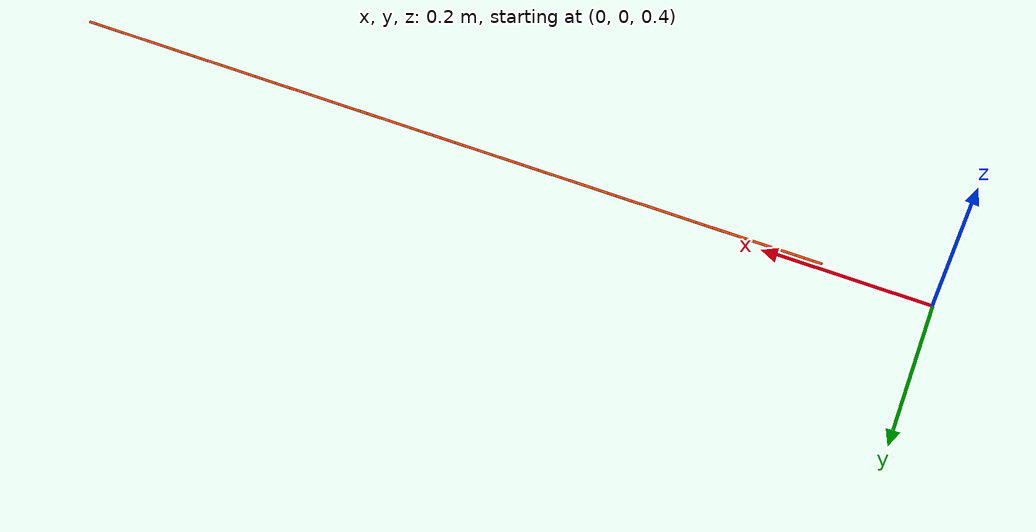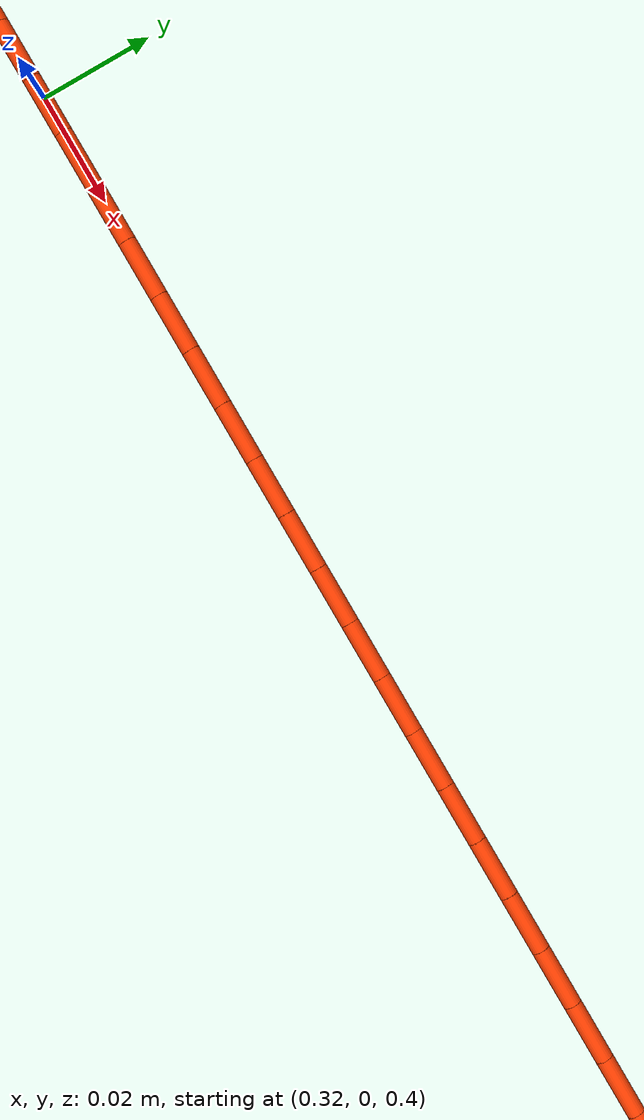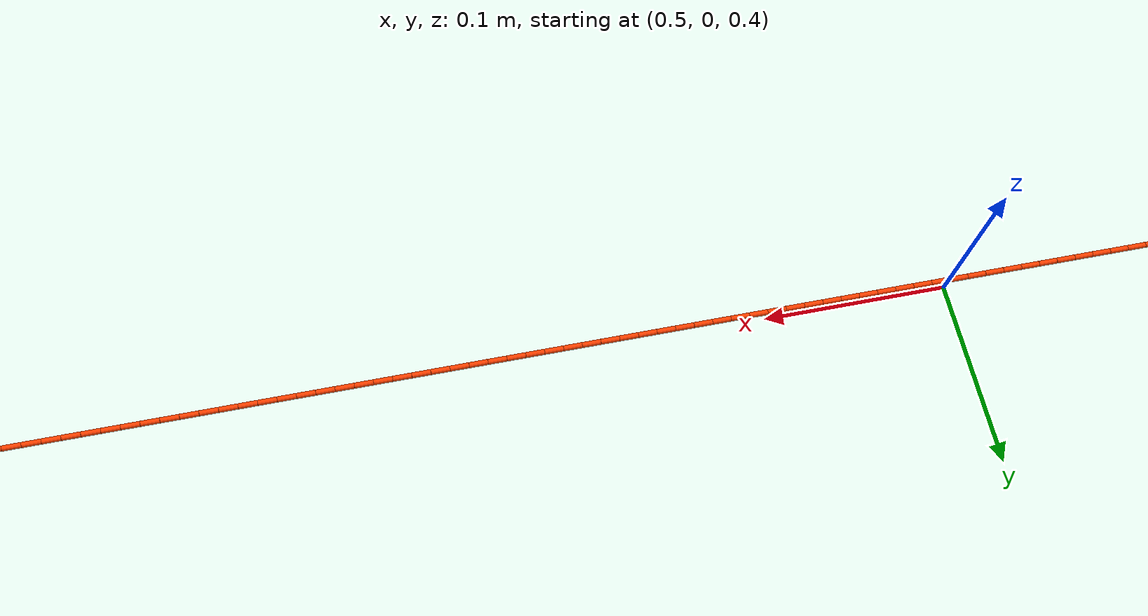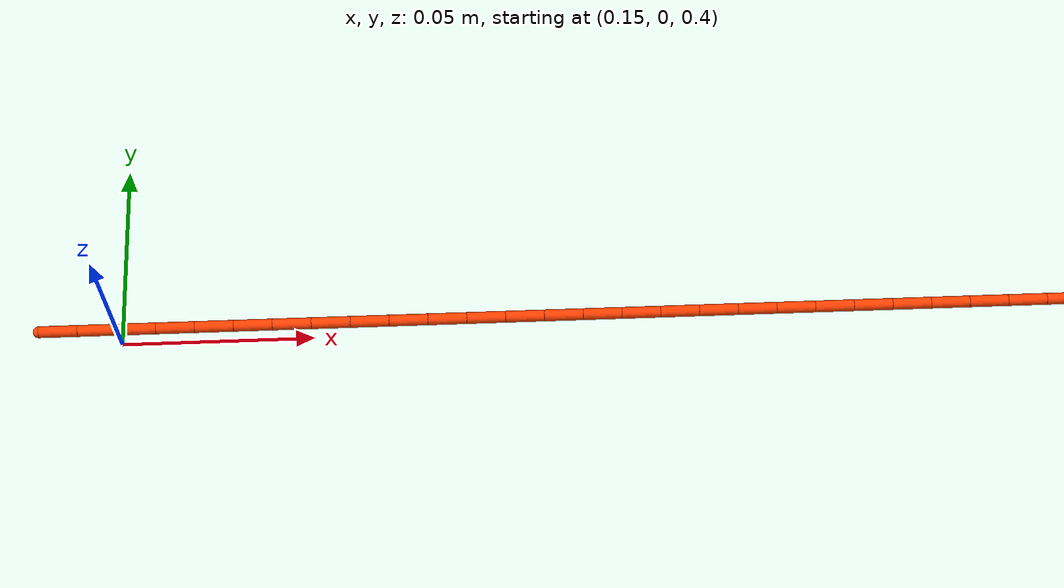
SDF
<?xml version="1.0" ?>
<sdf version="1.4">
  <model name="tethered_turtlebots">&lt;root&gt;data&lt;/root&gt;<link name="link_0"><pose>0.135 0.0 0.41 0.0 0.0 0.0</pose><inertial><pose>0.0 0.0 0.0 0.0 1.5708 0.0</pose><mass>0.001</mass><inertia><ixx>0.001</ixx><ixy>0</ixy><ixz>0</ixz><iyy>0.001</iyy><iyz>0</iyz><izz>0.001</izz></inertia></inertial><collision name="link_0_collision"><pose>0.0 0.0 0.0 0.0 1.5708 0.0</pose><geometry><cylinder><radius>0.0015</radius><length>0.01</length></cylinder></geometry><surface><contact><ode><min_depth>0.0001</min_depth></ode></contact><friction><ode><mu>1.0</mu><mu2>1.0</mu2></ode></friction></surface></collision><visual name="link_0_visual"><pose>0.0 0.0 0.0 0.0 1.5708 0.0</pose><geometry><cylinder><radius>0.0015</radius><length>0.01</length></cylinder></geometry><material><ambient>1 0.25 0 1.0</ambient><diffuse>1 0.25 0 1.0</diffuse><specular>0.1 0.1 0.1 1</specular><emissive>0 0 0 0</emissive></material></visual><visual name="link_0_visual_sphere"><pose>-0.005 0.0 0.0 0.0 0.0 0.0</pose><geometry><sphere><radius>0.0015</radius></sphere></geometry><material><ambient>1 0.25 0 1.0</ambient><diffuse>1 0.25 0 1.0</diffuse><specular>0.1 0.1 0.1 1</specular><emissive>0 0 0 0</emissive></material></visual></link><joint name="joint_0" type="universal"><pose>-0.005 0.0 0.0 0.0 0.0 0.0</pose><parent>base_foot1print</parent><child>link_0</child><axis><xyz>0 1 0</xyz><limit><lower>-1.57</lower><upper>1.57</upper></limit><dynamics><damping>0.1</damping></dynamics></axis><axis2><xyz>0 0 1</xyz><limit><lower>-1.57</lower><upper>1.57</upper></limit><dynamics><damping>0.1</damping></dynamics></axis2><physics><ode><cfm_damping>1</cfm_damping></ode></physics></joint><link name="link_1"><pose>0.145 0.0 0.41 0.0 0.0 0.0</pose><inertial><pose>0.0 0.0 0.0 0.0 1.5708 0.0</pose><mass>0.001</mass><inertia><ixx>0.001</ixx><ixy>0</ixy><ixz>0</ixz><iyy>0.001</iyy><iyz>0</iyz><izz>0.001</izz></inertia></inertial><collision name="link_1_collision"><pose>0.0 0.0 0.0 0.0 1.5708 0.0</pose><geometry><cylinder><radius>0.0015</radius><length>0.01</length></cylinder></geometry><surface><contact><ode><min_depth>0.0001</min_depth></ode></contact><friction><ode><mu>1.0</mu><mu2>1.0</mu2></ode></friction></surface></collision><visual name="link_1_visual"><pose>0.0 0.0 0.0 0.0 1.5708 0.0</pose><geometry><cylinder><radius>0.0015</radius><length>0.01</length></cylinder></geometry><material><ambient>1 0.25 0 1.0</ambient><diffuse>1 0.25 0 1.0</diffuse><specular>0.1 0.1 0.1 1</specular><emissive>0 0 0 0</emissive></material></visual><visual name="link_1_visual_sphere"><pose>-0.005 0.0 0.0 0.0 0.0 0.0</pose><geometry><sphere><radius>0.0015</radius></sphere></geometry><material><ambient>1 0.25 0 1.0</ambient><diffuse>1 0.25 0 1.0</diffuse><specular>0.1 0.1 0.1 1</specular><emissive>0 0 0 0</emissive></material></visual></link><joint name="joint_1" type="universal"><pose>-0.005 0.0 0.0 0.0 0.0 0.0</pose><parent>link_0</parent><child>link_1</child><axis><xyz>0 1 0</xyz><limit><lower>-1.57</lower><upper>1.57</upper></limit><dynamics><damping>0.1</damping></dynamics></axis><axis2><xyz>0 0 1</xyz><limit><lower>-1.57</lower><upper>1.57</upper></limit><dynamics><damping>0.1</damping></dynamics></axis2><physics><ode><cfm_damping>1</cfm_damping></ode></physics></joint><link name="link_2"><pose>0.155 0.0 0.41 0.0 0.0 0.0</pose><inertial><pose>0.0 0.0 0.0 0.0 1.5708 0.0</pose><mass>0.001</mass><inertia><ixx>0.001</ixx><ixy>0</ixy><ixz>0</ixz><iyy>0.001</iyy><iyz>0</iyz><izz>0.001</izz></inertia></inertial><collision name="link_2_collision"><pose>0.0 0.0 0.0 0.0 1.5708 0.0</pose><geometry><cylinder><radius>0.0015</radius><length>0.01</length></cylinder></geometry><surface><contact><ode><min_depth>0.0001</min_depth></ode></contact><friction><ode><mu>1.0</mu><mu2>1.0</mu2></ode></friction></surface></collision><visual name="link_2_visual"><pose>0.0 0.0 0.0 0.0 1.5708 0.0</pose><geometry><cylinder><radius>0.0015</radius><length>0.01</length></cylinder></geometry><material><ambient>1 0.25 0 1.0</ambient><diffuse>1 0.25 0 1.0</diffuse><specular>0.1 0.1 0.1 1</specular><emissive>0 0 0 0</emissive></material></visual><visual name="link_2_visual_sphere"><pose>-0.005 0.0 0.0 0.0 0.0 0.0</pose><geometry><sphere><radius>0.0015</radius></sphere></geometry><material><ambient>1 0.25 0 1.0</ambient><diffuse>1 0.25 0 1.0</diffuse><specular>0.1 0.1 0.1 1</specular><emissive>0 0 0 0</emissive></material></visual></link><joint name="joint_2" type="universal"><pose>-0.005 0.0 0.0 0.0 0.0 0.0</pose><parent>link_1</parent><child>link_2</child><axis><xyz>0 1 0</xyz><limit><lower>-1.57</lower><upper>1.57</upper></limit><dynamics><damping>0.1</damping></dynamics></axis><axis2><xyz>0 0 1</xyz><limit><lower>-1.57</lower><upper>1.57</upper></limit><dynamics><damping>0.1</damping></dynamics></axis2><physics><ode><cfm_damping>1</cfm_damping></ode></physics></joint><link name="link_3"><pose>0.165 0.0 0.41 0.0 0.0 0.0</pose><inertial><pose>0.0 0.0 0.0 0.0 1.5708 0.0</pose><mass>0.001</mass><inertia><ixx>0.001</ixx><ixy>0</ixy><ixz>0</ixz><iyy>0.001</iyy><iyz>0</iyz><izz>0.001</izz></inertia></inertial><collision name="link_3_collision"><pose>0.0 0.0 0.0 0.0 1.5708 0.0</pose><geometry><cylinder><radius>0.0015</radius><length>0.01</length></cylinder></geometry><surface><contact><ode><min_depth>0.0001</min_depth></ode></contact><friction><ode><mu>1.0</mu><mu2>1.0</mu2></ode></friction></surface></collision><visual name="link_3_visual"><pose>0.0 0.0 0.0 0.0 1.5708 0.0</pose><geometry><cylinder><radius>0.0015</radius><length>0.01</length></cylinder></geometry><material><ambient>1 0.25 0 1.0</ambient><diffuse>1 0.25 0 1.0</diffuse><specular>0.1 0.1 0.1 1</specular><emissive>0 0 0 0</emissive></material></visual><visual name="link_3_visual_sphere"><pose>-0.005 0.0 0.0 0.0 0.0 0.0</pose><geometry><sphere><radius>0.0015</radius></sphere></geometry><material><ambient>1 0.25 0 1.0</ambient><diffuse>1 0.25 0 1.0</diffuse><specular>0.1 0.1 0.1 1</specular><emissive>0 0 0 0</emissive></material></visual></link><joint name="joint_3" type="universal"><pose>-0.005 0.0 0.0 0.0 0.0 0.0</pose><parent>link_2</parent><child>link_3</child><axis><xyz>0 1 0</xyz><limit><lower>-1.57</lower><upper>1.57</upper></limit><dynamics><damping>0.1</damping></dynamics></axis><axis2><xyz>0 0 1</xyz><limit><lower>-1.57</lower><upper>1.57</upper></limit><dynamics><damping>0.1</damping></dynamics></axis2><physics><ode><cfm_damping>1</cfm_damping></ode></physics></joint><link name="link_4"><pose>0.175 0.0 0.41 0.0 0.0 0.0</pose><inertial><pose>0.0 0.0 0.0 0.0 1.5708 0.0</pose><mass>0.001</mass><inertia><ixx>0.001</ixx><ixy>0</ixy><ixz>0</ixz><iyy>0.001</iyy><iyz>0</iyz><izz>0.001</izz></inertia></inertial><collision name="link_4_collision"><pose>0.0 0.0 0.0 0.0 1.5708 0.0</pose><geometry><cylinder><radius>0.0015</radius><length>0.01</length></cylinder></geometry><surface><contact><ode><min_depth>0.0001</min_depth></ode></contact><friction><ode><mu>1.0</mu><mu2>1.0</mu2></ode></friction></surface></collision><visual name="link_4_visual"><pose>0.0 0.0 0.0 0.0 1.5708 0.0</pose><geometry><cylinder><radius>0.0015</radius><length>0.01</length></cylinder></geometry><material><ambient>1 0.25 0 1.0</ambient><diffuse>1 0.25 0 1.0</diffuse><specular>0.1 0.1 0.1 1</specular><emissive>0 0 0 0</emissive></material></visual><visual name="link_4_visual_sphere"><pose>-0.005 0.0 0.0 0.0 0.0 0.0</pose><geometry><sphere><radius>0.0015</radius></sphere></geometry><material><ambient>1 0.25 0 1.0</ambient><diffuse>1 0.25 0 1.0</diffuse><specular>0.1 0.1 0.1 1</specular><emissive>0 0 0 0</emissive></material></visual></link><joint name="joint_4" type="universal"><pose>-0.005 0.0 0.0 0.0 0.0 0.0</pose><parent>link_3</parent><child>link_4</child><axis><xyz>0 1 0</xyz><limit><lower>-1.57</lower><upper>1.57</upper></limit><dynamics><damping>0.1</damping></dynamics></axis><axis2><xyz>0 0 1</xyz><limit><lower>-1.57</lower><upper>1.57</upper></limit><dynamics><damping>0.1</damping></dynamics></axis2><physics><ode><cfm_damping>1</cfm_damping></ode></physics></joint><link name="link_5"><pose>0.185 0.0 0.41 0.0 0.0 0.0</pose><inertial><pose>0.0 0.0 0.0 0.0 1.5708 0.0</pose><mass>0.001</mass><inertia><ixx>0.001</ixx><ixy>0</ixy><ixz>0</ixz><iyy>0.001</iyy><iyz>0</iyz><izz>0.001</izz></inertia></inertial><collision name="link_5_collision"><pose>0.0 0.0 0.0 0.0 1.5708 0.0</pose><geometry><cylinder><radius>0.0015</radius><length>0.01</length></cylinder></geometry><surface><contact><ode><min_depth>0.0001</min_depth></ode></contact><friction><ode><mu>1.0</mu><mu2>1.0</mu2></ode></friction></surface></collision><visual name="link_5_visual"><pose>0.0 0.0 0.0 0.0 1.5708 0.0</pose><geometry><cylinder><radius>0.0015</radius><length>0.01</length></cylinder></geometry><material><ambient>1 0.25 0 1.0</ambient><diffuse>1 0.25 0 1.0</diffuse><specular>0.1 0.1 0.1 1</specular><emissive>0 0 0 0</emissive></material></visual><visual name="link_5_visual_sphere"><pose>-0.005 0.0 0.0 0.0 0.0 0.0</pose><geometry><sphere><radius>0.0015</radius></sphere></geometry><material><ambient>1 0.25 0 1.0</ambient><diffuse>1 0.25 0 1.0</diffuse><specular>0.1 0.1 0.1 1</specular><emissive>0 0 0 0</emissive></material></visual></link><joint name="joint_5" type="universal"><pose>-0.005 0.0 0.0 0.0 0.0 0.0</pose><parent>link_4</parent><child>link_5</child><axis><xyz>0 1 0</xyz><limit><lower>-1.57</lower><upper>1.57</upper></limit><dynamics><damping>0.1</damping></dynamics></axis><axis2><xyz>0 0 1</xyz><limit><lower>-1.57</lower><upper>1.57</upper></limit><dynamics><damping>0.1</damping></dynamics></axis2><physics><ode><cfm_damping>1</cfm_damping></ode></physics></joint><link name="link_6"><pose>0.195 0.0 0.41 0.0 0.0 0.0</pose><inertial><pose>0.0 0.0 0.0 0.0 1.5708 0.0</pose><mass>0.001</mass><inertia><ixx>0.001</ixx><ixy>0</ixy><ixz>0</ixz><iyy>0.001</iyy><iyz>0</iyz><izz>0.001</izz></inertia></inertial><collision name="link_6_collision"><pose>0.0 0.0 0.0 0.0 1.5708 0.0</pose><geometry><cylinder><radius>0.0015</radius><length>0.01</length></cylinder></geometry><surface><contact><ode><min_depth>0.0001</min_depth></ode></contact><friction><ode><mu>1.0</mu><mu2>1.0</mu2></ode></friction></surface></collision><visual name="link_6_visual"><pose>0.0 0.0 0.0 0.0 1.5708 0.0</pose><geometry><cylinder><radius>0.0015</radius><length>0.01</length></cylinder></geometry><material><ambient>1 0.25 0 1.0</ambient><diffuse>1 0.25 0 1.0</diffuse><specular>0.1 0.1 0.1 1</specular><emissive>0 0 0 0</emissive></material></visual><visual name="link_6_visual_sphere"><pose>-0.005 0.0 0.0 0.0 0.0 0.0</pose><geometry><sphere><radius>0.0015</radius></sphere></geometry><material><ambient>1 0.25 0 1.0</ambient><diffuse>1 0.25 0 1.0</diffuse><specular>0.1 0.1 0.1 1</specular><emissive>0 0 0 0</emissive></material></visual></link><joint name="joint_6" type="universal"><pose>-0.005 0.0 0.0 0.0 0.0 0.0</pose><parent>link_5</parent><child>link_6</child><axis><xyz>0 1 0</xyz><limit><lower>-1.57</lower><upper>1.57</upper></limit><dynamics><damping>0.1</damping></dynamics></axis><axis2><xyz>0 0 1</xyz><limit><lower>-1.57</lower><upper>1.57</upper></limit><dynamics><damping>0.1</damping></dynamics></axis2><physics><ode><cfm_damping>1</cfm_damping></ode></physics></joint><link name="link_7"><pose>0.205 0.0 0.41 0.0 0.0 0.0</pose><inertial><pose>0.0 0.0 0.0 0.0 1.5708 0.0</pose><mass>0.001</mass><inertia><ixx>0.001</ixx><ixy>0</ixy><ixz>0</ixz><iyy>0.001</iyy><iyz>0</iyz><izz>0.001</izz></inertia></inertial><collision name="link_7_collision"><pose>0.0 0.0 0.0 0.0 1.5708 0.0</pose><geometry><cylinder><radius>0.0015</radius><length>0.01</length></cylinder></geometry><surface><contact><ode><min_depth>0.0001</min_depth></ode></contact><friction><ode><mu>1.0</mu><mu2>1.0</mu2></ode></friction></surface></collision><visual name="link_7_visual"><pose>0.0 0.0 0.0 0.0 1.5708 0.0</pose><geometry><cylinder><radius>0.0015</radius><length>0.01</length></cylinder></geometry><material><ambient>1 0.25 0 1.0</ambient><diffuse>1 0.25 0 1.0</diffuse><specular>0.1 0.1 0.1 1</specular><emissive>0 0 0 0</emissive></material></visual><visual name="link_7_visual_sphere"><pose>-0.005 0.0 0.0 0.0 0.0 0.0</pose><geometry><sphere><radius>0.0015</radius></sphere></geometry><material><ambient>1 0.25 0 1.0</ambient><diffuse>1 0.25 0 1.0</diffuse><specular>0.1 0.1 0.1 1</specular><emissive>0 0 0 0</emissive></material></visual></link><joint name="joint_7" type="universal"><pose>-0.005 0.0 0.0 0.0 0.0 0.0</pose><parent>link_6</parent><child>link_7</child><axis><xyz>0 1 0</xyz><limit><lower>-1.57</lower><upper>1.57</upper></limit><dynamics><damping>0.1</damping></dynamics></axis><axis2><xyz>0 0 1</xyz><limit><lower>-1.57</lower><upper>1.57</upper></limit><dynamics><damping>0.1</damping></dynamics></axis2><physics><ode><cfm_damping>1</cfm_damping></ode></physics></joint><link name="link_8"><pose>0.215 0.0 0.41 0.0 0.0 0.0</pose><inertial><pose>0.0 0.0 0.0 0.0 1.5708 0.0</pose><mass>0.001</mass><inertia><ixx>0.001</ixx><ixy>0</ixy><ixz>0</ixz><iyy>0.001</iyy><iyz>0</iyz><izz>0.001</izz></inertia></inertial><collision name="link_8_collision"><pose>0.0 0.0 0.0 0.0 1.5708 0.0</pose><geometry><cylinder><radius>0.0015</radius><length>0.01</length></cylinder></geometry><surface><contact><ode><min_depth>0.0001</min_depth></ode></contact><friction><ode><mu>1.0</mu><mu2>1.0</mu2></ode></friction></surface></collision><visual name="link_8_visual"><pose>0.0 0.0 0.0 0.0 1.5708 0.0</pose><geometry><cylinder><radius>0.0015</radius><length>0.01</length></cylinder></geometry><material><ambient>1 0.25 0 1.0</ambient><diffuse>1 0.25 0 1.0</diffuse><specular>0.1 0.1 0.1 1</specular><emissive>0 0 0 0</emissive></material></visual><visual name="link_8_visual_sphere"><pose>-0.005 0.0 0.0 0.0 0.0 0.0</pose><geometry><sphere><radius>0.0015</radius></sphere></geometry><material><ambient>1 0.25 0 1.0</ambient><diffuse>1 0.25 0 1.0</diffuse><specular>0.1 0.1 0.1 1</specular><emissive>0 0 0 0</emissive></material></visual></link><joint name="joint_8" type="universal"><pose>-0.005 0.0 0.0 0.0 0.0 0.0</pose><parent>link_7</parent><child>link_8</child><axis><xyz>0 1 0</xyz><limit><lower>-1.57</lower><upper>1.57</upper></limit><dynamics><damping>0.1</damping></dynamics></axis><axis2><xyz>0 0 1</xyz><limit><lower>-1.57</lower><upper>1.57</upper></limit><dynamics><damping>0.1</damping></dynamics></axis2><physics><ode><cfm_damping>1</cfm_damping></ode></physics></joint><link name="link_9"><pose>0.225 0.0 0.41 0.0 0.0 0.0</pose><inertial><pose>0.0 0.0 0.0 0.0 1.5708 0.0</pose><mass>0.001</mass><inertia><ixx>0.001</ixx><ixy>0</ixy><ixz>0</ixz><iyy>0.001</iyy><iyz>0</iyz><izz>0.001</izz></inertia></inertial><collision name="link_9_collision"><pose>0.0 0.0 0.0 0.0 1.5708 0.0</pose><geometry><cylinder><radius>0.0015</radius><length>0.01</length></cylinder></geometry><surface><contact><ode><min_depth>0.0001</min_depth></ode></contact><friction><ode><mu>1.0</mu><mu2>1.0</mu2></ode></friction></surface></collision><visual name="link_9_visual"><pose>0.0 0.0 0.0 0.0 1.5708 0.0</pose><geometry><cylinder><radius>0.0015</radius><length>0.01</length></cylinder></geometry><material><ambient>1 0.25 0 1.0</ambient><diffuse>1 0.25 0 1.0</diffuse><specular>0.1 0.1 0.1 1</specular><emissive>0 0 0 0</emissive></material></visual><visual name="link_9_visual_sphere"><pose>-0.005 0.0 0.0 0.0 0.0 0.0</pose><geometry><sphere><radius>0.0015</radius></sphere></geometry><material><ambient>1 0.25 0 1.0</ambient><diffuse>1 0.25 0 1.0</diffuse><specular>0.1 0.1 0.1 1</specular><emissive>0 0 0 0</emissive></material></visual></link><joint name="joint_9" type="universal"><pose>-0.005 0.0 0.0 0.0 0.0 0.0</pose><parent>link_8</parent><child>link_9</child><axis><xyz>0 1 0</xyz><limit><lower>-1.57</lower><upper>1.57</upper></limit><dynamics><damping>0.1</damping></dynamics></axis><axis2><xyz>0 0 1</xyz><limit><lower>-1.57</lower><upper>1.57</upper></limit><dynamics><damping>0.1</damping></dynamics></axis2><physics><ode><cfm_damping>1</cfm_damping></ode></physics></joint><link name="link_10"><pose>0.235 0.0 0.41 0.0 0.0 0.0</pose><inertial><pose>0.0 0.0 0.0 0.0 1.5708 0.0</pose><mass>0.001</mass><inertia><ixx>0.001</ixx><ixy>0</ixy><ixz>0</ixz><iyy>0.001</iyy><iyz>0</iyz><izz>0.001</izz></inertia></inertial><collision name="link_10_collision"><pose>0.0 0.0 0.0 0.0 1.5708 0.0</pose><geometry><cylinder><radius>0.0015</radius><length>0.01</length></cylinder></geometry><surface><contact><ode><min_depth>0.0001</min_depth></ode></contact><friction><ode><mu>1.0</mu><mu2>1.0</mu2></ode></friction></surface></collision><visual name="link_10_visual"><pose>0.0 0.0 0.0 0.0 1.5708 0.0</pose><geometry><cylinder><radius>0.0015</radius><length>0.01</length></cylinder></geometry><material><ambient>1 0.25 0 1.0</ambient><diffuse>1 0.25 0 1.0</diffuse><specular>0.1 0.1 0.1 1</specular><emissive>0 0 0 0</emissive></material></visual><visual name="link_10_visual_sphere"><pose>-0.005 0.0 0.0 0.0 0.0 0.0</pose><geometry><sphere><radius>0.0015</radius></sphere></geometry><material><ambient>1 0.25 0 1.0</ambient><diffuse>1 0.25 0 1.0</diffuse><specular>0.1 0.1 0.1 1</specular><emissive>0 0 0 0</emissive></material></visual></link><joint name="joint_10" type="universal"><pose>-0.005 0.0 0.0 0.0 0.0 0.0</pose><parent>link_9</parent><child>link_10</child><axis><xyz>0 1 0</xyz><limit><lower>-1.57</lower><upper>1.57</upper></limit><dynamics><damping>0.1</damping></dynamics></axis><axis2><xyz>0 0 1</xyz><limit><lower>-1.57</lower><upper>1.57</upper></limit><dynamics><damping>0.1</damping></dynamics></axis2><physics><ode><cfm_damping>1</cfm_damping></ode></physics></joint><link name="link_11"><pose>0.245 0.0 0.41 0.0 0.0 0.0</pose><inertial><pose>0.0 0.0 0.0 0.0 1.5708 0.0</pose><mass>0.001</mass><inertia><ixx>0.001</ixx><ixy>0</ixy><ixz>0</ixz><iyy>0.001</iyy><iyz>0</iyz><izz>0.001</izz></inertia></inertial><collision name="link_11_collision"><pose>0.0 0.0 0.0 0.0 1.5708 0.0</pose><geometry><cylinder><radius>0.0015</radius><length>0.01</length></cylinder></geometry><surface><contact><ode><min_depth>0.0001</min_depth></ode></contact><friction><ode><mu>1.0</mu><mu2>1.0</mu2></ode></friction></surface></collision><visual name="link_11_visual"><pose>0.0 0.0 0.0 0.0 1.5708 0.0</pose><geometry><cylinder><radius>0.0015</radius><length>0.01</length></cylinder></geometry><material><ambient>1 0.25 0 1.0</ambient><diffuse>1 0.25 0 1.0</diffuse><specular>0.1 0.1 0.1 1</specular><emissive>0 0 0 0</emissive></material></visual><visual name="link_11_visual_sphere"><pose>-0.005 0.0 0.0 0.0 0.0 0.0</pose><geometry><sphere><radius>0.0015</radius></sphere></geometry><material><ambient>1 0.25 0 1.0</ambient><diffuse>1 0.25 0 1.0</diffuse><specular>0.1 0.1 0.1 1</specular><emissive>0 0 0 0</emissive></material></visual></link><joint name="joint_11" type="universal"><pose>-0.005 0.0 0.0 0.0 0.0 0.0</pose><parent>link_10</parent><child>link_11</child><axis><xyz>0 1 0</xyz><limit><lower>-1.57</lower><upper>1.57</upper></limit><dynamics><damping>0.1</damping></dynamics></axis><axis2><xyz>0 0 1</xyz><limit><lower>-1.57</lower><upper>1.57</upper></limit><dynamics><damping>0.1</damping></dynamics></axis2><physics><ode><cfm_damping>1</cfm_damping></ode></physics></joint><link name="link_12"><pose>0.255 0.0 0.41 0.0 0.0 0.0</pose><inertial><pose>0.0 0.0 0.0 0.0 1.5708 0.0</pose><mass>0.001</mass><inertia><ixx>0.001</ixx><ixy>0</ixy><ixz>0</ixz><iyy>0.001</iyy><iyz>0</iyz><izz>0.001</izz></inertia></inertial><collision name="link_12_collision"><pose>0.0 0.0 0.0 0.0 1.5708 0.0</pose><geometry><cylinder><radius>0.0015</radius><length>0.01</length></cylinder></geometry><surface><contact><ode><min_depth>0.0001</min_depth></ode></contact><friction><ode><mu>1.0</mu><mu2>1.0</mu2></ode></friction></surface></collision><visual name="link_12_visual"><pose>0.0 0.0 0.0 0.0 1.5708 0.0</pose><geometry><cylinder><radius>0.0015</radius><length>0.01</length></cylinder></geometry><material><ambient>1 0.25 0 1.0</ambient><diffuse>1 0.25 0 1.0</diffuse><specular>0.1 0.1 0.1 1</specular><emissive>0 0 0 0</emissive></material></visual><visual name="link_12_visual_sphere"><pose>-0.005 0.0 0.0 0.0 0.0 0.0</pose><geometry><sphere><radius>0.0015</radius></sphere></geometry><material><ambient>1 0.25 0 1.0</ambient><diffuse>1 0.25 0 1.0</diffuse><specular>0.1 0.1 0.1 1</specular><emissive>0 0 0 0</emissive></material></visual></link><joint name="joint_12" type="universal"><pose>-0.005 0.0 0.0 0.0 0.0 0.0</pose><parent>link_11</parent><child>link_12</child><axis><xyz>0 1 0</xyz><limit><lower>-1.57</lower><upper>1.57</upper></limit><dynamics><damping>0.1</damping></dynamics></axis><axis2><xyz>0 0 1</xyz><limit><lower>-1.57</lower><upper>1.57</upper></limit><dynamics><damping>0.1</damping></dynamics></axis2><physics><ode><cfm_damping>1</cfm_damping></ode></physics></joint><link name="link_13"><pose>0.265 0.0 0.41 0.0 0.0 0.0</pose><inertial><pose>0.0 0.0 0.0 0.0 1.5708 0.0</pose><mass>0.001</mass><inertia><ixx>0.001</ixx><ixy>0</ixy><ixz>0</ixz><iyy>0.001</iyy><iyz>0</iyz><izz>0.001</izz></inertia></inertial><collision name="link_13_collision"><pose>0.0 0.0 0.0 0.0 1.5708 0.0</pose><geometry><cylinder><radius>0.0015</radius><length>0.01</length></cylinder></geometry><surface><contact><ode><min_depth>0.0001</min_depth></ode></contact><friction><ode><mu>1.0</mu><mu2>1.0</mu2></ode></friction></surface></collision><visual name="link_13_visual"><pose>0.0 0.0 0.0 0.0 1.5708 0.0</pose><geometry><cylinder><radius>0.0015</radius><length>0.01</length></cylinder></geometry><material><ambient>1 0.25 0 1.0</ambient><diffuse>1 0.25 0 1.0</diffuse><specular>0.1 0.1 0.1 1</specular><emissive>0 0 0 0</emissive></material></visual><visual name="link_13_visual_sphere"><pose>-0.005 0.0 0.0 0.0 0.0 0.0</pose><geometry><sphere><radius>0.0015</radius></sphere></geometry><material><ambient>1 0.25 0 1.0</ambient><diffuse>1 0.25 0 1.0</diffuse><specular>0.1 0.1 0.1 1</specular><emissive>0 0 0 0</emissive></material></visual></link><joint name="joint_13" type="universal"><pose>-0.005 0.0 0.0 0.0 0.0 0.0</pose><parent>link_12</parent><child>link_13</child><axis><xyz>0 1 0</xyz><limit><lower>-1.57</lower><upper>1.57</upper></limit><dynamics><damping>0.1</damping></dynamics></axis><axis2><xyz>0 0 1</xyz><limit><lower>-1.57</lower><upper>1.57</upper></limit><dynamics><damping>0.1</damping></dynamics></axis2><physics><ode><cfm_damping>1</cfm_damping></ode></physics></joint><link name="link_14"><pose>0.275 0.0 0.41 0.0 0.0 0.0</pose><inertial><pose>0.0 0.0 0.0 0.0 1.5708 0.0</pose><mass>0.001</mass><inertia><ixx>0.001</ixx><ixy>0</ixy><ixz>0</ixz><iyy>0.001</iyy><iyz>0</iyz><izz>0.001</izz></inertia></inertial><collision name="link_14_collision"><pose>0.0 0.0 0.0 0.0 1.5708 0.0</pose><geometry><cylinder><radius>0.0015</radius><length>0.01</length></cylinder></geometry><surface><contact><ode><min_depth>0.0001</min_depth></ode></contact><friction><ode><mu>1.0</mu><mu2>1.0</mu2></ode></friction></surface></collision><visual name="link_14_visual"><pose>0.0 0.0 0.0 0.0 1.5708 0.0</pose><geometry><cylinder><radius>0.0015</radius><length>0.01</length></cylinder></geometry><material><ambient>1 0.25 0 1.0</ambient><diffuse>1 0.25 0 1.0</diffuse><specular>0.1 0.1 0.1 1</specular><emissive>0 0 0 0</emissive></material></visual><visual name="link_14_visual_sphere"><pose>-0.005 0.0 0.0 0.0 0.0 0.0</pose><geometry><sphere><radius>0.0015</radius></sphere></geometry><material><ambient>1 0.25 0 1.0</ambient><diffuse>1 0.25 0 1.0</diffuse><specular>0.1 0.1 0.1 1</specular><emissive>0 0 0 0</emissive></material></visual></link><joint name="joint_14" type="universal"><pose>-0.005 0.0 0.0 0.0 0.0 0.0</pose><parent>link_13</parent><child>link_14</child><axis><xyz>0 1 0</xyz><limit><lower>-1.57</lower><upper>1.57</upper></limit><dynamics><damping>0.1</damping></dynamics></axis><axis2><xyz>0 0 1</xyz><limit><lower>-1.57</lower><upper>1.57</upper></limit><dynamics><damping>0.1</damping></dynamics></axis2><physics><ode><cfm_damping>1</cfm_damping></ode></physics></joint><link name="link_15"><pose>0.285 0.0 0.41 0.0 0.0 0.0</pose><inertial><pose>0.0 0.0 0.0 0.0 1.5708 0.0</pose><mass>0.001</mass><inertia><ixx>0.001</ixx><ixy>0</ixy><ixz>0</ixz><iyy>0.001</iyy><iyz>0</iyz><izz>0.001</izz></inertia></inertial><collision name="link_15_collision"><pose>0.0 0.0 0.0 0.0 1.5708 0.0</pose><geometry><cylinder><radius>0.0015</radius><length>0.01</length></cylinder></geometry><surface><contact><ode><min_depth>0.0001</min_depth></ode></contact><friction><ode><mu>1.0</mu><mu2>1.0</mu2></ode></friction></surface></collision><visual name="link_15_visual"><pose>0.0 0.0 0.0 0.0 1.5708 0.0</pose><geometry><cylinder><radius>0.0015</radius><length>0.01</length></cylinder></geometry><material><ambient>1 0.25 0 1.0</ambient><diffuse>1 0.25 0 1.0</diffuse><specular>0.1 0.1 0.1 1</specular><emissive>0 0 0 0</emissive></material></visual><visual name="link_15_visual_sphere"><pose>-0.005 0.0 0.0 0.0 0.0 0.0</pose><geometry><sphere><radius>0.0015</radius></sphere></geometry><material><ambient>1 0.25 0 1.0</ambient><diffuse>1 0.25 0 1.0</diffuse><specular>0.1 0.1 0.1 1</specular><emissive>0 0 0 0</emissive></material></visual></link><joint name="joint_15" type="universal"><pose>-0.005 0.0 0.0 0.0 0.0 0.0</pose><parent>link_14</parent><child>link_15</child><axis><xyz>0 1 0</xyz><limit><lower>-1.57</lower><upper>1.57</upper></limit><dynamics><damping>0.1</damping></dynamics></axis><axis2><xyz>0 0 1</xyz><limit><lower>-1.57</lower><upper>1.57</upper></limit><dynamics><damping>0.1</damping></dynamics></axis2><physics><ode><cfm_damping>1</cfm_damping></ode></physics></joint><link name="link_16"><pose>0.295 0.0 0.41 0.0 0.0 0.0</pose><inertial><pose>0.0 0.0 0.0 0.0 1.5708 0.0</pose><mass>0.001</mass><inertia><ixx>0.001</ixx><ixy>0</ixy><ixz>0</ixz><iyy>0.001</iyy><iyz>0</iyz><izz>0.001</izz></inertia></inertial><collision name="link_16_collision"><pose>0.0 0.0 0.0 0.0 1.5708 0.0</pose><geometry><cylinder><radius>0.0015</radius><length>0.01</length></cylinder></geometry><surface><contact><ode><min_depth>0.0001</min_depth></ode></contact><friction><ode><mu>1.0</mu><mu2>1.0</mu2></ode></friction></surface></collision><visual name="link_16_visual"><pose>0.0 0.0 0.0 0.0 1.5708 0.0</pose><geometry><cylinder><radius>0.0015</radius><length>0.01</length></cylinder></geometry><material><ambient>1 0.25 0 1.0</ambient><diffuse>1 0.25 0 1.0</diffuse><specular>0.1 0.1 0.1 1</specular><emissive>0 0 0 0</emissive></material></visual><visual name="link_16_visual_sphere"><pose>-0.005 0.0 0.0 0.0 0.0 0.0</pose><geometry><sphere><radius>0.0015</radius></sphere></geometry><material><ambient>1 0.25 0 1.0</ambient><diffuse>1 0.25 0 1.0</diffuse><specular>0.1 0.1 0.1 1</specular><emissive>0 0 0 0</emissive></material></visual></link><joint name="joint_16" type="universal"><pose>-0.005 0.0 0.0 0.0 0.0 0.0</pose><parent>link_15</parent><child>link_16</child><axis><xyz>0 1 0</xyz><limit><lower>-1.57</lower><upper>1.57</upper></limit><dynamics><damping>0.1</damping></dynamics></axis><axis2><xyz>0 0 1</xyz><limit><lower>-1.57</lower><upper>1.57</upper></limit><dynamics><damping>0.1</damping></dynamics></axis2><physics><ode><cfm_damping>1</cfm_damping></ode></physics></joint><link name="link_17"><pose>0.305 0.0 0.41 0.0 0.0 0.0</pose><inertial><pose>0.0 0.0 0.0 0.0 1.5708 0.0</pose><mass>0.001</mass><inertia><ixx>0.001</ixx><ixy>0</ixy><ixz>0</ixz><iyy>0.001</iyy><iyz>0</iyz><izz>0.001</izz></inertia></inertial><collision name="link_17_collision"><pose>0.0 0.0 0.0 0.0 1.5708 0.0</pose><geometry><cylinder><radius>0.0015</radius><length>0.01</length></cylinder></geometry><surface><contact><ode><min_depth>0.0001</min_depth></ode></contact><friction><ode><mu>1.0</mu><mu2>1.0</mu2></ode></friction></surface></collision><visual name="link_17_visual"><pose>0.0 0.0 0.0 0.0 1.5708 0.0</pose><geometry><cylinder><radius>0.0015</radius><length>0.01</length></cylinder></geometry><material><ambient>1 0.25 0 1.0</ambient><diffuse>1 0.25 0 1.0</diffuse><specular>0.1 0.1 0.1 1</specular><emissive>0 0 0 0</emissive></material></visual><visual name="link_17_visual_sphere"><pose>-0.005 0.0 0.0 0.0 0.0 0.0</pose><geometry><sphere><radius>0.0015</radius></sphere></geometry><material><ambient>1 0.25 0 1.0</ambient><diffuse>1 0.25 0 1.0</diffuse><specular>0.1 0.1 0.1 1</specular><emissive>0 0 0 0</emissive></material></visual></link><joint name="joint_17" type="universal"><pose>-0.005 0.0 0.0 0.0 0.0 0.0</pose><parent>link_16</parent><child>link_17</child><axis><xyz>0 1 0</xyz><limit><lower>-1.57</lower><upper>1.57</upper></limit><dynamics><damping>0.1</damping></dynamics></axis><axis2><xyz>0 0 1</xyz><limit><lower>-1.57</lower><upper>1.57</upper></limit><dynamics><damping>0.1</damping></dynamics></axis2><physics><ode><cfm_damping>1</cfm_damping></ode></physics></joint><link name="link_18"><pose>0.315 0.0 0.41 0.0 0.0 0.0</pose><inertial><pose>0.0 0.0 0.0 0.0 1.5708 0.0</pose><mass>0.001</mass><inertia><ixx>0.001</ixx><ixy>0</ixy><ixz>0</ixz><iyy>0.001</iyy><iyz>0</iyz><izz>0.001</izz></inertia></inertial><collision name="link_18_collision"><pose>0.0 0.0 0.0 0.0 1.5708 0.0</pose><geometry><cylinder><radius>0.0015</radius><length>0.01</length></cylinder></geometry><surface><contact><ode><min_depth>0.0001</min_depth></ode></contact><friction><ode><mu>1.0</mu><mu2>1.0</mu2></ode></friction></surface></collision><visual name="link_18_visual"><pose>0.0 0.0 0.0 0.0 1.5708 0.0</pose><geometry><cylinder><radius>0.0015</radius><length>0.01</length></cylinder></geometry><material><ambient>1 0.25 0 1.0</ambient><diffuse>1 0.25 0 1.0</diffuse><specular>0.1 0.1 0.1 1</specular><emissive>0 0 0 0</emissive></material></visual><visual name="link_18_visual_sphere"><pose>-0.005 0.0 0.0 0.0 0.0 0.0</pose><geometry><sphere><radius>0.0015</radius></sphere></geometry><material><ambient>1 0.25 0 1.0</ambient><diffuse>1 0.25 0 1.0</diffuse><specular>0.1 0.1 0.1 1</specular><emissive>0 0 0 0</emissive></material></visual></link><joint name="joint_18" type="universal"><pose>-0.005 0.0 0.0 0.0 0.0 0.0</pose><parent>link_17</parent><child>link_18</child><axis><xyz>0 1 0</xyz><limit><lower>-1.57</lower><upper>1.57</upper></limit><dynamics><damping>0.1</damping></dynamics></axis><axis2><xyz>0 0 1</xyz><limit><lower>-1.57</lower><upper>1.57</upper></limit><dynamics><damping>0.1</damping></dynamics></axis2><physics><ode><cfm_damping>1</cfm_damping></ode></physics></joint><link name="link_19"><pose>0.325 0.0 0.41 0.0 0.0 0.0</pose><inertial><pose>0.0 0.0 0.0 0.0 1.5708 0.0</pose><mass>0.001</mass><inertia><ixx>0.001</ixx><ixy>0</ixy><ixz>0</ixz><iyy>0.001</iyy><iyz>0</iyz><izz>0.001</izz></inertia></inertial><collision name="link_19_collision"><pose>0.0 0.0 0.0 0.0 1.5708 0.0</pose><geometry><cylinder><radius>0.0015</radius><length>0.01</length></cylinder></geometry><surface><contact><ode><min_depth>0.0001</min_depth></ode></contact><friction><ode><mu>1.0</mu><mu2>1.0</mu2></ode></friction></surface></collision><visual name="link_19_visual"><pose>0.0 0.0 0.0 0.0 1.5708 0.0</pose><geometry><cylinder><radius>0.0015</radius><length>0.01</length></cylinder></geometry><material><ambient>1 0.25 0 1.0</ambient><diffuse>1 0.25 0 1.0</diffuse><specular>0.1 0.1 0.1 1</specular><emissive>0 0 0 0</emissive></material></visual><visual name="link_19_visual_sphere"><pose>-0.005 0.0 0.0 0.0 0.0 0.0</pose><geometry><sphere><radius>0.0015</radius></sphere></geometry><material><ambient>1 0.25 0 1.0</ambient><diffuse>1 0.25 0 1.0</diffuse><specular>0.1 0.1 0.1 1</specular><emissive>0 0 0 0</emissive></material></visual></link><joint name="joint_19" type="universal"><pose>-0.005 0.0 0.0 0.0 0.0 0.0</pose><parent>link_18</parent><child>link_19</child><axis><xyz>0 1 0</xyz><limit><lower>-1.57</lower><upper>1.57</upper></limit><dynamics><damping>0.1</damping></dynamics></axis><axis2><xyz>0 0 1</xyz><limit><lower>-1.57</lower><upper>1.57</upper></limit><dynamics><damping>0.1</damping></dynamics></axis2><physics><ode><cfm_damping>1</cfm_damping></ode></physics></joint><link name="link_20"><pose>0.335 0.0 0.41 0.0 0.0 0.0</pose><inertial><pose>0.0 0.0 0.0 0.0 1.5708 0.0</pose><mass>0.001</mass><inertia><ixx>0.001</ixx><ixy>0</ixy><ixz>0</ixz><iyy>0.001</iyy><iyz>0</iyz><izz>0.001</izz></inertia></inertial><collision name="link_20_collision"><pose>0.0 0.0 0.0 0.0 1.5708 0.0</pose><geometry><cylinder><radius>0.0015</radius><length>0.01</length></cylinder></geometry><surface><contact><ode><min_depth>0.0001</min_depth></ode></contact><friction><ode><mu>1.0</mu><mu2>1.0</mu2></ode></friction></surface></collision><visual name="link_20_visual"><pose>0.0 0.0 0.0 0.0 1.5708 0.0</pose><geometry><cylinder><radius>0.0015</radius><length>0.01</length></cylinder></geometry><material><ambient>1 0.25 0 1.0</ambient><diffuse>1 0.25 0 1.0</diffuse><specular>0.1 0.1 0.1 1</specular><emissive>0 0 0 0</emissive></material></visual><visual name="link_20_visual_sphere"><pose>-0.005 0.0 0.0 0.0 0.0 0.0</pose><geometry><sphere><radius>0.0015</radius></sphere></geometry><material><ambient>1 0.25 0 1.0</ambient><diffuse>1 0.25 0 1.0</diffuse><specular>0.1 0.1 0.1 1</specular><emissive>0 0 0 0</emissive></material></visual></link><joint name="joint_20" type="universal"><pose>-0.005 0.0 0.0 0.0 0.0 0.0</pose><parent>link_19</parent><child>link_20</child><axis><xyz>0 1 0</xyz><limit><lower>-1.57</lower><upper>1.57</upper></limit><dynamics><damping>0.1</damping></dynamics></axis><axis2><xyz>0 0 1</xyz><limit><lower>-1.57</lower><upper>1.57</upper></limit><dynamics><damping>0.1</damping></dynamics></axis2><physics><ode><cfm_damping>1</cfm_damping></ode></physics></joint><link name="link_21"><pose>0.345 0.0 0.41 0.0 0.0 0.0</pose><inertial><pose>0.0 0.0 0.0 0.0 1.5708 0.0</pose><mass>0.001</mass><inertia><ixx>0.001</ixx><ixy>0</ixy><ixz>0</ixz><iyy>0.001</iyy><iyz>0</iyz><izz>0.001</izz></inertia></inertial><collision name="link_21_collision"><pose>0.0 0.0 0.0 0.0 1.5708 0.0</pose><geometry><cylinder><radius>0.0015</radius><length>0.01</length></cylinder></geometry><surface><contact><ode><min_depth>0.0001</min_depth></ode></contact><friction><ode><mu>1.0</mu><mu2>1.0</mu2></ode></friction></surface></collision><visual name="link_21_visual"><pose>0.0 0.0 0.0 0.0 1.5708 0.0</pose><geometry><cylinder><radius>0.0015</radius><length>0.01</length></cylinder></geometry><material><ambient>1 0.25 0 1.0</ambient><diffuse>1 0.25 0 1.0</diffuse><specular>0.1 0.1 0.1 1</specular><emissive>0 0 0 0</emissive></material></visual><visual name="link_21_visual_sphere"><pose>-0.005 0.0 0.0 0.0 0.0 0.0</pose><geometry><sphere><radius>0.0015</radius></sphere></geometry><material><ambient>1 0.25 0 1.0</ambient><diffuse>1 0.25 0 1.0</diffuse><specular>0.1 0.1 0.1 1</specular><emissive>0 0 0 0</emissive></material></visual></link><joint name="joint_21" type="universal"><pose>-0.005 0.0 0.0 0.0 0.0 0.0</pose><parent>link_20</parent><child>link_21</child><axis><xyz>0 1 0</xyz><limit><lower>-1.57</lower><upper>1.57</upper></limit><dynamics><damping>0.1</damping></dynamics></axis><axis2><xyz>0 0 1</xyz><limit><lower>-1.57</lower><upper>1.57</upper></limit><dynamics><damping>0.1</damping></dynamics></axis2><physics><ode><cfm_damping>1</cfm_damping></ode></physics></joint><link name="link_22"><pose>0.355 0.0 0.41 0.0 0.0 0.0</pose><inertial><pose>0.0 0.0 0.0 0.0 1.5708 0.0</pose><mass>0.001</mass><inertia><ixx>0.001</ixx><ixy>0</ixy><ixz>0</ixz><iyy>0.001</iyy><iyz>0</iyz><izz>0.001</izz></inertia></inertial><collision name="link_22_collision"><pose>0.0 0.0 0.0 0.0 1.5708 0.0</pose><geometry><cylinder><radius>0.0015</radius><length>0.01</length></cylinder></geometry><surface><contact><ode><min_depth>0.0001</min_depth></ode></contact><friction><ode><mu>1.0</mu><mu2>1.0</mu2></ode></friction></surface></collision><visual name="link_22_visual"><pose>0.0 0.0 0.0 0.0 1.5708 0.0</pose><geometry><cylinder><radius>0.0015</radius><length>0.01</length></cylinder></geometry><material><ambient>1 0.25 0 1.0</ambient><diffuse>1 0.25 0 1.0</diffuse><specular>0.1 0.1 0.1 1</specular><emissive>0 0 0 0</emissive></material></visual><visual name="link_22_visual_sphere"><pose>-0.005 0.0 0.0 0.0 0.0 0.0</pose><geometry><sphere><radius>0.0015</radius></sphere></geometry><material><ambient>1 0.25 0 1.0</ambient><diffuse>1 0.25 0 1.0</diffuse><specular>0.1 0.1 0.1 1</specular><emissive>0 0 0 0</emissive></material></visual></link><joint name="joint_22" type="universal"><pose>-0.005 0.0 0.0 0.0 0.0 0.0</pose><parent>link_21</parent><child>link_22</child><axis><xyz>0 1 0</xyz><limit><lower>-1.57</lower><upper>1.57</upper></limit><dynamics><damping>0.1</damping></dynamics></axis><axis2><xyz>0 0 1</xyz><limit><lower>-1.57</lower><upper>1.57</upper></limit><dynamics><damping>0.1</damping></dynamics></axis2><physics><ode><cfm_damping>1</cfm_damping></ode></physics></joint><link name="link_23"><pose>0.365 0.0 0.41 0.0 0.0 0.0</pose><inertial><pose>0.0 0.0 0.0 0.0 1.5708 0.0</pose><mass>0.001</mass><inertia><ixx>0.001</ixx><ixy>0</ixy><ixz>0</ixz><iyy>0.001</iyy><iyz>0</iyz><izz>0.001</izz></inertia></inertial><collision name="link_23_collision"><pose>0.0 0.0 0.0 0.0 1.5708 0.0</pose><geometry><cylinder><radius>0.0015</radius><length>0.01</length></cylinder></geometry><surface><contact><ode><min_depth>0.0001</min_depth></ode></contact><friction><ode><mu>1.0</mu><mu2>1.0</mu2></ode></friction></surface></collision><visual name="link_23_visual"><pose>0.0 0.0 0.0 0.0 1.5708 0.0</pose><geometry><cylinder><radius>0.0015</radius><length>0.01</length></cylinder></geometry><material><ambient>1 0.25 0 1.0</ambient><diffuse>1 0.25 0 1.0</diffuse><specular>0.1 0.1 0.1 1</specular><emissive>0 0 0 0</emissive></material></visual><visual name="link_23_visual_sphere"><pose>-0.005 0.0 0.0 0.0 0.0 0.0</pose><geometry><sphere><radius>0.0015</radius></sphere></geometry><material><ambient>1 0.25 0 1.0</ambient><diffuse>1 0.25 0 1.0</diffuse><specular>0.1 0.1 0.1 1</specular><emissive>0 0 0 0</emissive></material></visual></link><joint name="joint_23" type="universal"><pose>-0.005 0.0 0.0 0.0 0.0 0.0</pose><parent>link_22</parent><child>link_23</child><axis><xyz>0 1 0</xyz><limit><lower>-1.57</lower><upper>1.57</upper></limit><dynamics><damping>0.1</damping></dynamics></axis><axis2><xyz>0 0 1</xyz><limit><lower>-1.57</lower><upper>1.57</upper></limit><dynamics><damping>0.1</damping></dynamics></axis2><physics><ode><cfm_damping>1</cfm_damping></ode></physics></joint><link name="link_24"><pose>0.375 0.0 0.41 0.0 0.0 0.0</pose><inertial><pose>0.0 0.0 0.0 0.0 1.5708 0.0</pose><mass>0.001</mass><inertia><ixx>0.001</ixx><ixy>0</ixy><ixz>0</ixz><iyy>0.001</iyy><iyz>0</iyz><izz>0.001</izz></inertia></inertial><collision name="link_24_collision"><pose>0.0 0.0 0.0 0.0 1.5708 0.0</pose><geometry><cylinder><radius>0.0015</radius><length>0.01</length></cylinder></geometry><surface><contact><ode><min_depth>0.0001</min_depth></ode></contact><friction><ode><mu>1.0</mu><mu2>1.0</mu2></ode></friction></surface></collision><visual name="link_24_visual"><pose>0.0 0.0 0.0 0.0 1.5708 0.0</pose><geometry><cylinder><radius>0.0015</radius><length>0.01</length></cylinder></geometry><material><ambient>1 0.25 0 1.0</ambient><diffuse>1 0.25 0 1.0</diffuse><specular>0.1 0.1 0.1 1</specular><emissive>0 0 0 0</emissive></material></visual><visual name="link_24_visual_sphere"><pose>-0.005 0.0 0.0 0.0 0.0 0.0</pose><geometry><sphere><radius>0.0015</radius></sphere></geometry><material><ambient>1 0.25 0 1.0</ambient><diffuse>1 0.25 0 1.0</diffuse><specular>0.1 0.1 0.1 1</specular><emissive>0 0 0 0</emissive></material></visual></link><joint name="joint_24" type="universal"><pose>-0.005 0.0 0.0 0.0 0.0 0.0</pose><parent>link_23</parent><child>link_24</child><axis><xyz>0 1 0</xyz><limit><lower>-1.57</lower><upper>1.57</upper></limit><dynamics><damping>0.1</damping></dynamics></axis><axis2><xyz>0 0 1</xyz><limit><lower>-1.57</lower><upper>1.57</upper></limit><dynamics><damping>0.1</damping></dynamics></axis2><physics><ode><cfm_damping>1</cfm_damping></ode></physics></joint><link name="link_25"><pose>0.385 0.0 0.41 0.0 0.0 0.0</pose><inertial><pose>0.0 0.0 0.0 0.0 1.5708 0.0</pose><mass>0.001</mass><inertia><ixx>0.001</ixx><ixy>0</ixy><ixz>0</ixz><iyy>0.001</iyy><iyz>0</iyz><izz>0.001</izz></inertia></inertial><collision name="link_25_collision"><pose>0.0 0.0 0.0 0.0 1.5708 0.0</pose><geometry><cylinder><radius>0.0015</radius><length>0.01</length></cylinder></geometry><surface><contact><ode><min_depth>0.0001</min_depth></ode></contact><friction><ode><mu>1.0</mu><mu2>1.0</mu2></ode></friction></surface></collision><visual name="link_25_visual"><pose>0.0 0.0 0.0 0.0 1.5708 0.0</pose><geometry><cylinder><radius>0.0015</radius><length>0.01</length></cylinder></geometry><material><ambient>1 0.25 0 1.0</ambient><diffuse>1 0.25 0 1.0</diffuse><specular>0.1 0.1 0.1 1</specular><emissive>0 0 0 0</emissive></material></visual><visual name="link_25_visual_sphere"><pose>-0.005 0.0 0.0 0.0 0.0 0.0</pose><geometry><sphere><radius>0.0015</radius></sphere></geometry><material><ambient>1 0.25 0 1.0</ambient><diffuse>1 0.25 0 1.0</diffuse><specular>0.1 0.1 0.1 1</specular><emissive>0 0 0 0</emissive></material></visual></link><joint name="joint_25" type="universal"><pose>-0.005 0.0 0.0 0.0 0.0 0.0</pose><parent>link_24</parent><child>link_25</child><axis><xyz>0 1 0</xyz><limit><lower>-1.57</lower><upper>1.57</upper></limit><dynamics><damping>0.1</damping></dynamics></axis><axis2><xyz>0 0 1</xyz><limit><lower>-1.57</lower><upper>1.57</upper></limit><dynamics><damping>0.1</damping></dynamics></axis2><physics><ode><cfm_damping>1</cfm_damping></ode></physics></joint><link name="link_26"><pose>0.395 0.0 0.41 0.0 0.0 0.0</pose><inertial><pose>0.0 0.0 0.0 0.0 1.5708 0.0</pose><mass>0.001</mass><inertia><ixx>0.001</ixx><ixy>0</ixy><ixz>0</ixz><iyy>0.001</iyy><iyz>0</iyz><izz>0.001</izz></inertia></inertial><collision name="link_26_collision"><pose>0.0 0.0 0.0 0.0 1.5708 0.0</pose><geometry><cylinder><radius>0.0015</radius><length>0.01</length></cylinder></geometry><surface><contact><ode><min_depth>0.0001</min_depth></ode></contact><friction><ode><mu>1.0</mu><mu2>1.0</mu2></ode></friction></surface></collision><visual name="link_26_visual"><pose>0.0 0.0 0.0 0.0 1.5708 0.0</pose><geometry><cylinder><radius>0.0015</radius><length>0.01</length></cylinder></geometry><material><ambient>1 0.25 0 1.0</ambient><diffuse>1 0.25 0 1.0</diffuse><specular>0.1 0.1 0.1 1</specular><emissive>0 0 0 0</emissive></material></visual><visual name="link_26_visual_sphere"><pose>-0.005 0.0 0.0 0.0 0.0 0.0</pose><geometry><sphere><radius>0.0015</radius></sphere></geometry><material><ambient>1 0.25 0 1.0</ambient><diffuse>1 0.25 0 1.0</diffuse><specular>0.1 0.1 0.1 1</specular><emissive>0 0 0 0</emissive></material></visual></link><joint name="joint_26" type="universal"><pose>-0.005 0.0 0.0 0.0 0.0 0.0</pose><parent>link_25</parent><child>link_26</child><axis><xyz>0 1 0</xyz><limit><lower>-1.57</lower><upper>1.57</upper></limit><dynamics><damping>0.1</damping></dynamics></axis><axis2><xyz>0 0 1</xyz><limit><lower>-1.57</lower><upper>1.57</upper></limit><dynamics><damping>0.1</damping></dynamics></axis2><physics><ode><cfm_damping>1</cfm_damping></ode></physics></joint><link name="link_27"><pose>0.405 0.0 0.41 0.0 0.0 0.0</pose><inertial><pose>0.0 0.0 0.0 0.0 1.5708 0.0</pose><mass>0.001</mass><inertia><ixx>0.001</ixx><ixy>0</ixy><ixz>0</ixz><iyy>0.001</iyy><iyz>0</iyz><izz>0.001</izz></inertia></inertial><collision name="link_27_collision"><pose>0.0 0.0 0.0 0.0 1.5708 0.0</pose><geometry><cylinder><radius>0.0015</radius><length>0.01</length></cylinder></geometry><surface><contact><ode><min_depth>0.0001</min_depth></ode></contact><friction><ode><mu>1.0</mu><mu2>1.0</mu2></ode></friction></surface></collision><visual name="link_27_visual"><pose>0.0 0.0 0.0 0.0 1.5708 0.0</pose><geometry><cylinder><radius>0.0015</radius><length>0.01</length></cylinder></geometry><material><ambient>1 0.25 0 1.0</ambient><diffuse>1 0.25 0 1.0</diffuse><specular>0.1 0.1 0.1 1</specular><emissive>0 0 0 0</emissive></material></visual><visual name="link_27_visual_sphere"><pose>-0.005 0.0 0.0 0.0 0.0 0.0</pose><geometry><sphere><radius>0.0015</radius></sphere></geometry><material><ambient>1 0.25 0 1.0</ambient><diffuse>1 0.25 0 1.0</diffuse><specular>0.1 0.1 0.1 1</specular><emissive>0 0 0 0</emissive></material></visual></link><joint name="joint_27" type="universal"><pose>-0.005 0.0 0.0 0.0 0.0 0.0</pose><parent>link_26</parent><child>link_27</child><axis><xyz>0 1 0</xyz><limit><lower>-1.57</lower><upper>1.57</upper></limit><dynamics><damping>0.1</damping></dynamics></axis><axis2><xyz>0 0 1</xyz><limit><lower>-1.57</lower><upper>1.57</upper></limit><dynamics><damping>0.1</damping></dynamics></axis2><physics><ode><cfm_damping>1</cfm_damping></ode></physics></joint><link name="link_28"><pose>0.415 0.0 0.41 0.0 0.0 0.0</pose><inertial><pose>0.0 0.0 0.0 0.0 1.5708 0.0</pose><mass>0.001</mass><inertia><ixx>0.001</ixx><ixy>0</ixy><ixz>0</ixz><iyy>0.001</iyy><iyz>0</iyz><izz>0.001</izz></inertia></inertial><collision name="link_28_collision"><pose>0.0 0.0 0.0 0.0 1.5708 0.0</pose><geometry><cylinder><radius>0.0015</radius><length>0.01</length></cylinder></geometry><surface><contact><ode><min_depth>0.0001</min_depth></ode></contact><friction><ode><mu>1.0</mu><mu2>1.0</mu2></ode></friction></surface></collision><visual name="link_28_visual"><pose>0.0 0.0 0.0 0.0 1.5708 0.0</pose><geometry><cylinder><radius>0.0015</radius><length>0.01</length></cylinder></geometry><material><ambient>1 0.25 0 1.0</ambient><diffuse>1 0.25 0 1.0</diffuse><specular>0.1 0.1 0.1 1</specular><emissive>0 0 0 0</emissive></material></visual><visual name="link_28_visual_sphere"><pose>-0.005 0.0 0.0 0.0 0.0 0.0</pose><geometry><sphere><radius>0.0015</radius></sphere></geometry><material><ambient>1 0.25 0 1.0</ambient><diffuse>1 0.25 0 1.0</diffuse><specular>0.1 0.1 0.1 1</specular><emissive>0 0 0 0</emissive></material></visual></link><joint name="joint_28" type="universal"><pose>-0.005 0.0 0.0 0.0 0.0 0.0</pose><parent>link_27</parent><child>link_28</child><axis><xyz>0 1 0</xyz><limit><lower>-1.57</lower><upper>1.57</upper></limit><dynamics><damping>0.1</damping></dynamics></axis><axis2><xyz>0 0 1</xyz><limit><lower>-1.57</lower><upper>1.57</upper></limit><dynamics><damping>0.1</damping></dynamics></axis2><physics><ode><cfm_damping>1</cfm_damping></ode></physics></joint><link name="link_29"><pose>0.425 0.0 0.41 0.0 0.0 0.0</pose><inertial><pose>0.0 0.0 0.0 0.0 1.5708 0.0</pose><mass>0.001</mass><inertia><ixx>0.001</ixx><ixy>0</ixy><ixz>0</ixz><iyy>0.001</iyy><iyz>0</iyz><izz>0.001</izz></inertia></inertial><collision name="link_29_collision"><pose>0.0 0.0 0.0 0.0 1.5708 0.0</pose><geometry><cylinder><radius>0.0015</radius><length>0.01</length></cylinder></geometry><surface><contact><ode><min_depth>0.0001</min_depth></ode></contact><friction><ode><mu>1.0</mu><mu2>1.0</mu2></ode></friction></surface></collision><visual name="link_29_visual"><pose>0.0 0.0 0.0 0.0 1.5708 0.0</pose><geometry><cylinder><radius>0.0015</radius><length>0.01</length></cylinder></geometry><material><ambient>1 0.25 0 1.0</ambient><diffuse>1 0.25 0 1.0</diffuse><specular>0.1 0.1 0.1 1</specular><emissive>0 0 0 0</emissive></material></visual><visual name="link_29_visual_sphere"><pose>-0.005 0.0 0.0 0.0 0.0 0.0</pose><geometry><sphere><radius>0.0015</radius></sphere></geometry><material><ambient>1 0.25 0 1.0</ambient><diffuse>1 0.25 0 1.0</diffuse><specular>0.1 0.1 0.1 1</specular><emissive>0 0 0 0</emissive></material></visual></link><joint name="joint_29" type="universal"><pose>-0.005 0.0 0.0 0.0 0.0 0.0</pose><parent>link_28</parent><child>link_29</child><axis><xyz>0 1 0</xyz><limit><lower>-1.57</lower><upper>1.57</upper></limit><dynamics><damping>0.1</damping></dynamics></axis><axis2><xyz>0 0 1</xyz><limit><lower>-1.57</lower><upper>1.57</upper></limit><dynamics><damping>0.1</damping></dynamics></axis2><physics><ode><cfm_damping>1</cfm_damping></ode></physics></joint><link name="link_30"><pose>0.435 0.0 0.41 0.0 0.0 0.0</pose><inertial><pose>0.0 0.0 0.0 0.0 1.5708 0.0</pose><mass>0.001</mass><inertia><ixx>0.001</ixx><ixy>0</ixy><ixz>0</ixz><iyy>0.001</iyy><iyz>0</iyz><izz>0.001</izz></inertia></inertial><collision name="link_30_collision"><pose>0.0 0.0 0.0 0.0 1.5708 0.0</pose><geometry><cylinder><radius>0.0015</radius><length>0.01</length></cylinder></geometry><surface><contact><ode><min_depth>0.0001</min_depth></ode></contact><friction><ode><mu>1.0</mu><mu2>1.0</mu2></ode></friction></surface></collision><visual name="link_30_visual"><pose>0.0 0.0 0.0 0.0 1.5708 0.0</pose><geometry><cylinder><radius>0.0015</radius><length>0.01</length></cylinder></geometry><material><ambient>1 0.25 0 1.0</ambient><diffuse>1 0.25 0 1.0</diffuse><specular>0.1 0.1 0.1 1</specular><emissive>0 0 0 0</emissive></material></visual><visual name="link_30_visual_sphere"><pose>-0.005 0.0 0.0 0.0 0.0 0.0</pose><geometry><sphere><radius>0.0015</radius></sphere></geometry><material><ambient>1 0.25 0 1.0</ambient><diffuse>1 0.25 0 1.0</diffuse><specular>0.1 0.1 0.1 1</specular><emissive>0 0 0 0</emissive></material></visual></link><joint name="joint_30" type="universal"><pose>-0.005 0.0 0.0 0.0 0.0 0.0</pose><parent>link_29</parent><child>link_30</child><axis><xyz>0 1 0</xyz><limit><lower>-1.57</lower><upper>1.57</upper></limit><dynamics><damping>0.1</damping></dynamics></axis><axis2><xyz>0 0 1</xyz><limit><lower>-1.57</lower><upper>1.57</upper></limit><dynamics><damping>0.1</damping></dynamics></axis2><physics><ode><cfm_damping>1</cfm_damping></ode></physics></joint><link name="link_31"><pose>0.445 0.0 0.41 0.0 0.0 0.0</pose><inertial><pose>0.0 0.0 0.0 0.0 1.5708 0.0</pose><mass>0.001</mass><inertia><ixx>0.001</ixx><ixy>0</ixy><ixz>0</ixz><iyy>0.001</iyy><iyz>0</iyz><izz>0.001</izz></inertia></inertial><collision name="link_31_collision"><pose>0.0 0.0 0.0 0.0 1.5708 0.0</pose><geometry><cylinder><radius>0.0015</radius><length>0.01</length></cylinder></geometry><surface><contact><ode><min_depth>0.0001</min_depth></ode></contact><friction><ode><mu>1.0</mu><mu2>1.0</mu2></ode></friction></surface></collision><visual name="link_31_visual"><pose>0.0 0.0 0.0 0.0 1.5708 0.0</pose><geometry><cylinder><radius>0.0015</radius><length>0.01</length></cylinder></geometry><material><ambient>1 0.25 0 1.0</ambient><diffuse>1 0.25 0 1.0</diffuse><specular>0.1 0.1 0.1 1</specular><emissive>0 0 0 0</emissive></material></visual><visual name="link_31_visual_sphere"><pose>-0.005 0.0 0.0 0.0 0.0 0.0</pose><geometry><sphere><radius>0.0015</radius></sphere></geometry><material><ambient>1 0.25 0 1.0</ambient><diffuse>1 0.25 0 1.0</diffuse><specular>0.1 0.1 0.1 1</specular><emissive>0 0 0 0</emissive></material></visual></link><joint name="joint_31" type="universal"><pose>-0.005 0.0 0.0 0.0 0.0 0.0</pose><parent>link_30</parent><child>link_31</child><axis><xyz>0 1 0</xyz><limit><lower>-1.57</lower><upper>1.57</upper></limit><dynamics><damping>0.1</damping></dynamics></axis><axis2><xyz>0 0 1</xyz><limit><lower>-1.57</lower><upper>1.57</upper></limit><dynamics><damping>0.1</damping></dynamics></axis2><physics><ode><cfm_damping>1</cfm_damping></ode></physics></joint><link name="link_32"><pose>0.455 0.0 0.41 0.0 0.0 0.0</pose><inertial><pose>0.0 0.0 0.0 0.0 1.5708 0.0</pose><mass>0.001</mass><inertia><ixx>0.001</ixx><ixy>0</ixy><ixz>0</ixz><iyy>0.001</iyy><iyz>0</iyz><izz>0.001</izz></inertia></inertial><collision name="link_32_collision"><pose>0.0 0.0 0.0 0.0 1.5708 0.0</pose><geometry><cylinder><radius>0.0015</radius><length>0.01</length></cylinder></geometry><surface><contact><ode><min_depth>0.0001</min_depth></ode></contact><friction><ode><mu>1.0</mu><mu2>1.0</mu2></ode></friction></surface></collision><visual name="link_32_visual"><pose>0.0 0.0 0.0 0.0 1.5708 0.0</pose><geometry><cylinder><radius>0.0015</radius><length>0.01</length></cylinder></geometry><material><ambient>1 0.25 0 1.0</ambient><diffuse>1 0.25 0 1.0</diffuse><specular>0.1 0.1 0.1 1</specular><emissive>0 0 0 0</emissive></material></visual><visual name="link_32_visual_sphere"><pose>-0.005 0.0 0.0 0.0 0.0 0.0</pose><geometry><sphere><radius>0.0015</radius></sphere></geometry><material><ambient>1 0.25 0 1.0</ambient><diffuse>1 0.25 0 1.0</diffuse><specular>0.1 0.1 0.1 1</specular><emissive>0 0 0 0</emissive></material></visual></link><joint name="joint_32" type="universal"><pose>-0.005 0.0 0.0 0.0 0.0 0.0</pose><parent>link_31</parent><child>link_32</child><axis><xyz>0 1 0</xyz><limit><lower>-1.57</lower><upper>1.57</upper></limit><dynamics><damping>0.1</damping></dynamics></axis><axis2><xyz>0 0 1</xyz><limit><lower>-1.57</lower><upper>1.57</upper></limit><dynamics><damping>0.1</damping></dynamics></axis2><physics><ode><cfm_damping>1</cfm_damping></ode></physics></joint><link name="link_33"><pose>0.465 0.0 0.41 0.0 0.0 0.0</pose><inertial><pose>0.0 0.0 0.0 0.0 1.5708 0.0</pose><mass>0.001</mass><inertia><ixx>0.001</ixx><ixy>0</ixy><ixz>0</ixz><iyy>0.001</iyy><iyz>0</iyz><izz>0.001</izz></inertia></inertial><collision name="link_33_collision"><pose>0.0 0.0 0.0 0.0 1.5708 0.0</pose><geometry><cylinder><radius>0.0015</radius><length>0.01</length></cylinder></geometry><surface><contact><ode><min_depth>0.0001</min_depth></ode></contact><friction><ode><mu>1.0</mu><mu2>1.0</mu2></ode></friction></surface></collision><visual name="link_33_visual"><pose>0.0 0.0 0.0 0.0 1.5708 0.0</pose><geometry><cylinder><radius>0.0015</radius><length>0.01</length></cylinder></geometry><material><ambient>1 0.25 0 1.0</ambient><diffuse>1 0.25 0 1.0</diffuse><specular>0.1 0.1 0.1 1</specular><emissive>0 0 0 0</emissive></material></visual><visual name="link_33_visual_sphere"><pose>-0.005 0.0 0.0 0.0 0.0 0.0</pose><geometry><sphere><radius>0.0015</radius></sphere></geometry><material><ambient>1 0.25 0 1.0</ambient><diffuse>1 0.25 0 1.0</diffuse><specular>0.1 0.1 0.1 1</specular><emissive>0 0 0 0</emissive></material></visual></link><joint name="joint_33" type="universal"><pose>-0.005 0.0 0.0 0.0 0.0 0.0</pose><parent>link_32</parent><child>link_33</child><axis><xyz>0 1 0</xyz><limit><lower>-1.57</lower><upper>1.57</upper></limit><dynamics><damping>0.1</damping></dynamics></axis><axis2><xyz>0 0 1</xyz><limit><lower>-1.57</lower><upper>1.57</upper></limit><dynamics><damping>0.1</damping></dynamics></axis2><physics><ode><cfm_damping>1</cfm_damping></ode></physics></joint><link name="link_34"><pose>0.475 0.0 0.41 0.0 0.0 0.0</pose><inertial><pose>0.0 0.0 0.0 0.0 1.5708 0.0</pose><mass>0.001</mass><inertia><ixx>0.001</ixx><ixy>0</ixy><ixz>0</ixz><iyy>0.001</iyy><iyz>0</iyz><izz>0.001</izz></inertia></inertial><collision name="link_34_collision"><pose>0.0 0.0 0.0 0.0 1.5708 0.0</pose><geometry><cylinder><radius>0.0015</radius><length>0.01</length></cylinder></geometry><surface><contact><ode><min_depth>0.0001</min_depth></ode></contact><friction><ode><mu>1.0</mu><mu2>1.0</mu2></ode></friction></surface></collision><visual name="link_34_visual"><pose>0.0 0.0 0.0 0.0 1.5708 0.0</pose><geometry><cylinder><radius>0.0015</radius><length>0.01</length></cylinder></geometry><material><ambient>1 0.25 0 1.0</ambient><diffuse>1 0.25 0 1.0</diffuse><specular>0.1 0.1 0.1 1</specular><emissive>0 0 0 0</emissive></material></visual><visual name="link_34_visual_sphere"><pose>-0.005 0.0 0.0 0.0 0.0 0.0</pose><geometry><sphere><radius>0.0015</radius></sphere></geometry><material><ambient>1 0.25 0 1.0</ambient><diffuse>1 0.25 0 1.0</diffuse><specular>0.1 0.1 0.1 1</specular><emissive>0 0 0 0</emissive></material></visual></link><joint name="joint_34" type="universal"><pose>-0.005 0.0 0.0 0.0 0.0 0.0</pose><parent>link_33</parent><child>link_34</child><axis><xyz>0 1 0</xyz><limit><lower>-1.57</lower><upper>1.57</upper></limit><dynamics><damping>0.1</damping></dynamics></axis><axis2><xyz>0 0 1</xyz><limit><lower>-1.57</lower><upper>1.57</upper></limit><dynamics><damping>0.1</damping></dynamics></axis2><physics><ode><cfm_damping>1</cfm_damping></ode></physics></joint><link name="link_35"><pose>0.485 0.0 0.41 0.0 0.0 0.0</pose><inertial><pose>0.0 0.0 0.0 0.0 1.5708 0.0</pose><mass>0.001</mass><inertia><ixx>0.001</ixx><ixy>0</ixy><ixz>0</ixz><iyy>0.001</iyy><iyz>0</iyz><izz>0.001</izz></inertia></inertial><collision name="link_35_collision"><pose>0.0 0.0 0.0 0.0 1.5708 0.0</pose><geometry><cylinder><radius>0.0015</radius><length>0.01</length></cylinder></geometry><surface><contact><ode><min_depth>0.0001</min_depth></ode></contact><friction><ode><mu>1.0</mu><mu2>1.0</mu2></ode></friction></surface></collision><visual name="link_35_visual"><pose>0.0 0.0 0.0 0.0 1.5708 0.0</pose><geometry><cylinder><radius>0.0015</radius><length>0.01</length></cylinder></geometry><material><ambient>1 0.25 0 1.0</ambient><diffuse>1 0.25 0 1.0</diffuse><specular>0.1 0.1 0.1 1</specular><emissive>0 0 0 0</emissive></material></visual><visual name="link_35_visual_sphere"><pose>-0.005 0.0 0.0 0.0 0.0 0.0</pose><geometry><sphere><radius>0.0015</radius></sphere></geometry><material><ambient>1 0.25 0 1.0</ambient><diffuse>1 0.25 0 1.0</diffuse><specular>0.1 0.1 0.1 1</specular><emissive>0 0 0 0</emissive></material></visual></link><joint name="joint_35" type="universal"><pose>-0.005 0.0 0.0 0.0 0.0 0.0</pose><parent>link_34</parent><child>link_35</child><axis><xyz>0 1 0</xyz><limit><lower>-1.57</lower><upper>1.57</upper></limit><dynamics><damping>0.1</damping></dynamics></axis><axis2><xyz>0 0 1</xyz><limit><lower>-1.57</lower><upper>1.57</upper></limit><dynamics><damping>0.1</damping></dynamics></axis2><physics><ode><cfm_damping>1</cfm_damping></ode></physics></joint><link name="link_36"><pose>0.495 0.0 0.41 0.0 0.0 0.0</pose><inertial><pose>0.0 0.0 0.0 0.0 1.5708 0.0</pose><mass>0.001</mass><inertia><ixx>0.001</ixx><ixy>0</ixy><ixz>0</ixz><iyy>0.001</iyy><iyz>0</iyz><izz>0.001</izz></inertia></inertial><collision name="link_36_collision"><pose>0.0 0.0 0.0 0.0 1.5708 0.0</pose><geometry><cylinder><radius>0.0015</radius><length>0.01</length></cylinder></geometry><surface><contact><ode><min_depth>0.0001</min_depth></ode></contact><friction><ode><mu>1.0</mu><mu2>1.0</mu2></ode></friction></surface></collision><visual name="link_36_visual"><pose>0.0 0.0 0.0 0.0 1.5708 0.0</pose><geometry><cylinder><radius>0.0015</radius><length>0.01</length></cylinder></geometry><material><ambient>1 0.25 0 1.0</ambient><diffuse>1 0.25 0 1.0</diffuse><specular>0.1 0.1 0.1 1</specular><emissive>0 0 0 0</emissive></material></visual><visual name="link_36_visual_sphere"><pose>-0.005 0.0 0.0 0.0 0.0 0.0</pose><geometry><sphere><radius>0.0015</radius></sphere></geometry><material><ambient>1 0.25 0 1.0</ambient><diffuse>1 0.25 0 1.0</diffuse><specular>0.1 0.1 0.1 1</specular><emissive>0 0 0 0</emissive></material></visual></link><joint name="joint_36" type="universal"><pose>-0.005 0.0 0.0 0.0 0.0 0.0</pose><parent>link_35</parent><child>link_36</child><axis><xyz>0 1 0</xyz><limit><lower>-1.57</lower><upper>1.57</upper></limit><dynamics><damping>0.1</damping></dynamics></axis><axis2><xyz>0 0 1</xyz><limit><lower>-1.57</lower><upper>1.57</upper></limit><dynamics><damping>0.1</damping></dynamics></axis2><physics><ode><cfm_damping>1</cfm_damping></ode></physics></joint><link name="link_37"><pose>0.505 0.0 0.41 0.0 0.0 0.0</pose><inertial><pose>0.0 0.0 0.0 0.0 1.5708 0.0</pose><mass>0.001</mass><inertia><ixx>0.001</ixx><ixy>0</ixy><ixz>0</ixz><iyy>0.001</iyy><iyz>0</iyz><izz>0.001</izz></inertia></inertial><collision name="link_37_collision"><pose>0.0 0.0 0.0 0.0 1.5708 0.0</pose><geometry><cylinder><radius>0.0015</radius><length>0.01</length></cylinder></geometry><surface><contact><ode><min_depth>0.0001</min_depth></ode></contact><friction><ode><mu>1.0</mu><mu2>1.0</mu2></ode></friction></surface></collision><visual name="link_37_visual"><pose>0.0 0.0 0.0 0.0 1.5708 0.0</pose><geometry><cylinder><radius>0.0015</radius><length>0.01</length></cylinder></geometry><material><ambient>1 0.25 0 1.0</ambient><diffuse>1 0.25 0 1.0</diffuse><specular>0.1 0.1 0.1 1</specular><emissive>0 0 0 0</emissive></material></visual><visual name="link_37_visual_sphere"><pose>-0.005 0.0 0.0 0.0 0.0 0.0</pose><geometry><sphere><radius>0.0015</radius></sphere></geometry><material><ambient>1 0.25 0 1.0</ambient><diffuse>1 0.25 0 1.0</diffuse><specular>0.1 0.1 0.1 1</specular><emissive>0 0 0 0</emissive></material></visual></link><joint name="joint_37" type="universal"><pose>-0.005 0.0 0.0 0.0 0.0 0.0</pose><parent>link_36</parent><child>link_37</child><axis><xyz>0 1 0</xyz><limit><lower>-1.57</lower><upper>1.57</upper></limit><dynamics><damping>0.1</damping></dynamics></axis><axis2><xyz>0 0 1</xyz><limit><lower>-1.57</lower><upper>1.57</upper></limit><dynamics><damping>0.1</damping></dynamics></axis2><physics><ode><cfm_damping>1</cfm_damping></ode></physics></joint><link name="link_38"><pose>0.515 0.0 0.41 0.0 0.0 0.0</pose><inertial><pose>0.0 0.0 0.0 0.0 1.5708 0.0</pose><mass>0.001</mass><inertia><ixx>0.001</ixx><ixy>0</ixy><ixz>0</ixz><iyy>0.001</iyy><iyz>0</iyz><izz>0.001</izz></inertia></inertial><collision name="link_38_collision"><pose>0.0 0.0 0.0 0.0 1.5708 0.0</pose><geometry><cylinder><radius>0.0015</radius><length>0.01</length></cylinder></geometry><surface><contact><ode><min_depth>0.0001</min_depth></ode></contact><friction><ode><mu>1.0</mu><mu2>1.0</mu2></ode></friction></surface></collision><visual name="link_38_visual"><pose>0.0 0.0 0.0 0.0 1.5708 0.0</pose><geometry><cylinder><radius>0.0015</radius><length>0.01</length></cylinder></geometry><material><ambient>1 0.25 0 1.0</ambient><diffuse>1 0.25 0 1.0</diffuse><specular>0.1 0.1 0.1 1</specular><emissive>0 0 0 0</emissive></material></visual><visual name="link_38_visual_sphere"><pose>-0.005 0.0 0.0 0.0 0.0 0.0</pose><geometry><sphere><radius>0.0015</radius></sphere></geometry><material><ambient>1 0.25 0 1.0</ambient><diffuse>1 0.25 0 1.0</diffuse><specular>0.1 0.1 0.1 1</specular><emissive>0 0 0 0</emissive></material></visual></link><joint name="joint_38" type="universal"><pose>-0.005 0.0 0.0 0.0 0.0 0.0</pose><parent>link_37</parent><child>link_38</child><axis><xyz>0 1 0</xyz><limit><lower>-1.57</lower><upper>1.57</upper></limit><dynamics><damping>0.1</damping></dynamics></axis><axis2><xyz>0 0 1</xyz><limit><lower>-1.57</lower><upper>1.57</upper></limit><dynamics><damping>0.1</damping></dynamics></axis2><physics><ode><cfm_damping>1</cfm_damping></ode></physics></joint><link name="link_39"><pose>0.525 0.0 0.41 0.0 0.0 0.0</pose><inertial><pose>0.0 0.0 0.0 0.0 1.5708 0.0</pose><mass>0.001</mass><inertia><ixx>0.001</ixx><ixy>0</ixy><ixz>0</ixz><iyy>0.001</iyy><iyz>0</iyz><izz>0.001</izz></inertia></inertial><collision name="link_39_collision"><pose>0.0 0.0 0.0 0.0 1.5708 0.0</pose><geometry><cylinder><radius>0.0015</radius><length>0.01</length></cylinder></geometry><surface><contact><ode><min_depth>0.0001</min_depth></ode></contact><friction><ode><mu>1.0</mu><mu2>1.0</mu2></ode></friction></surface></collision><visual name="link_39_visual"><pose>0.0 0.0 0.0 0.0 1.5708 0.0</pose><geometry><cylinder><radius>0.0015</radius><length>0.01</length></cylinder></geometry><material><ambient>1 0.25 0 1.0</ambient><diffuse>1 0.25 0 1.0</diffuse><specular>0.1 0.1 0.1 1</specular><emissive>0 0 0 0</emissive></material></visual><visual name="link_39_visual_sphere"><pose>-0.005 0.0 0.0 0.0 0.0 0.0</pose><geometry><sphere><radius>0.0015</radius></sphere></geometry><material><ambient>1 0.25 0 1.0</ambient><diffuse>1 0.25 0 1.0</diffuse><specular>0.1 0.1 0.1 1</specular><emissive>0 0 0 0</emissive></material></visual></link><joint name="joint_39" type="universal"><pose>-0.005 0.0 0.0 0.0 0.0 0.0</pose><parent>link_38</parent><child>link_39</child><axis><xyz>0 1 0</xyz><limit><lower>-1.57</lower><upper>1.57</upper></limit><dynamics><damping>0.1</damping></dynamics></axis><axis2><xyz>0 0 1</xyz><limit><lower>-1.57</lower><upper>1.57</upper></limit><dynamics><damping>0.1</damping></dynamics></axis2><physics><ode><cfm_damping>1</cfm_damping></ode></physics></joint><link name="link_40"><pose>0.535 0.0 0.41 0.0 0.0 0.0</pose><inertial><pose>0.0 0.0 0.0 0.0 1.5708 0.0</pose><mass>0.001</mass><inertia><ixx>0.001</ixx><ixy>0</ixy><ixz>0</ixz><iyy>0.001</iyy><iyz>0</iyz><izz>0.001</izz></inertia></inertial><collision name="link_40_collision"><pose>0.0 0.0 0.0 0.0 1.5708 0.0</pose><geometry><cylinder><radius>0.0015</radius><length>0.01</length></cylinder></geometry><surface><contact><ode><min_depth>0.0001</min_depth></ode></contact><friction><ode><mu>1.0</mu><mu2>1.0</mu2></ode></friction></surface></collision><visual name="link_40_visual"><pose>0.0 0.0 0.0 0.0 1.5708 0.0</pose><geometry><cylinder><radius>0.0015</radius><length>0.01</length></cylinder></geometry><material><ambient>1 0.25 0 1.0</ambient><diffuse>1 0.25 0 1.0</diffuse><specular>0.1 0.1 0.1 1</specular><emissive>0 0 0 0</emissive></material></visual><visual name="link_40_visual_sphere"><pose>-0.005 0.0 0.0 0.0 0.0 0.0</pose><geometry><sphere><radius>0.0015</radius></sphere></geometry><material><ambient>1 0.25 0 1.0</ambient><diffuse>1 0.25 0 1.0</diffuse><specular>0.1 0.1 0.1 1</specular><emissive>0 0 0 0</emissive></material></visual></link><joint name="joint_40" type="universal"><pose>-0.005 0.0 0.0 0.0 0.0 0.0</pose><parent>link_39</parent><child>link_40</child><axis><xyz>0 1 0</xyz><limit><lower>-1.57</lower><upper>1.57</upper></limit><dynamics><damping>0.1</damping></dynamics></axis><axis2><xyz>0 0 1</xyz><limit><lower>-1.57</lower><upper>1.57</upper></limit><dynamics><damping>0.1</damping></dynamics></axis2><physics><ode><cfm_damping>1</cfm_damping></ode></physics></joint><link name="link_41"><pose>0.545 0.0 0.41 0.0 0.0 0.0</pose><inertial><pose>0.0 0.0 0.0 0.0 1.5708 0.0</pose><mass>0.001</mass><inertia><ixx>0.001</ixx><ixy>0</ixy><ixz>0</ixz><iyy>0.001</iyy><iyz>0</iyz><izz>0.001</izz></inertia></inertial><collision name="link_41_collision"><pose>0.0 0.0 0.0 0.0 1.5708 0.0</pose><geometry><cylinder><radius>0.0015</radius><length>0.01</length></cylinder></geometry><surface><contact><ode><min_depth>0.0001</min_depth></ode></contact><friction><ode><mu>1.0</mu><mu2>1.0</mu2></ode></friction></surface></collision><visual name="link_41_visual"><pose>0.0 0.0 0.0 0.0 1.5708 0.0</pose><geometry><cylinder><radius>0.0015</radius><length>0.01</length></cylinder></geometry><material><ambient>1 0.25 0 1.0</ambient><diffuse>1 0.25 0 1.0</diffuse><specular>0.1 0.1 0.1 1</specular><emissive>0 0 0 0</emissive></material></visual><visual name="link_41_visual_sphere"><pose>-0.005 0.0 0.0 0.0 0.0 0.0</pose><geometry><sphere><radius>0.0015</radius></sphere></geometry><material><ambient>1 0.25 0 1.0</ambient><diffuse>1 0.25 0 1.0</diffuse><specular>0.1 0.1 0.1 1</specular><emissive>0 0 0 0</emissive></material></visual></link><joint name="joint_41" type="universal"><pose>-0.005 0.0 0.0 0.0 0.0 0.0</pose><parent>link_40</parent><child>link_41</child><axis><xyz>0 1 0</xyz><limit><lower>-1.57</lower><upper>1.57</upper></limit><dynamics><damping>0.1</damping></dynamics></axis><axis2><xyz>0 0 1</xyz><limit><lower>-1.57</lower><upper>1.57</upper></limit><dynamics><damping>0.1</damping></dynamics></axis2><physics><ode><cfm_damping>1</cfm_damping></ode></physics></joint><link name="link_42"><pose>0.555 0.0 0.41 0.0 0.0 0.0</pose><inertial><pose>0.0 0.0 0.0 0.0 1.5708 0.0</pose><mass>0.001</mass><inertia><ixx>0.001</ixx><ixy>0</ixy><ixz>0</ixz><iyy>0.001</iyy><iyz>0</iyz><izz>0.001</izz></inertia></inertial><collision name="link_42_collision"><pose>0.0 0.0 0.0 0.0 1.5708 0.0</pose><geometry><cylinder><radius>0.0015</radius><length>0.01</length></cylinder></geometry><surface><contact><ode><min_depth>0.0001</min_depth></ode></contact><friction><ode><mu>1.0</mu><mu2>1.0</mu2></ode></friction></surface></collision><visual name="link_42_visual"><pose>0.0 0.0 0.0 0.0 1.5708 0.0</pose><geometry><cylinder><radius>0.0015</radius><length>0.01</length></cylinder></geometry><material><ambient>1 0.25 0 1.0</ambient><diffuse>1 0.25 0 1.0</diffuse><specular>0.1 0.1 0.1 1</specular><emissive>0 0 0 0</emissive></material></visual><visual name="link_42_visual_sphere"><pose>-0.005 0.0 0.0 0.0 0.0 0.0</pose><geometry><sphere><radius>0.0015</radius></sphere></geometry><material><ambient>1 0.25 0 1.0</ambient><diffuse>1 0.25 0 1.0</diffuse><specular>0.1 0.1 0.1 1</specular><emissive>0 0 0 0</emissive></material></visual></link><joint name="joint_42" type="universal"><pose>-0.005 0.0 0.0 0.0 0.0 0.0</pose><parent>link_41</parent><child>link_42</child><axis><xyz>0 1 0</xyz><limit><lower>-1.57</lower><upper>1.57</upper></limit><dynamics><damping>0.1</damping></dynamics></axis><axis2><xyz>0 0 1</xyz><limit><lower>-1.57</lower><upper>1.57</upper></limit><dynamics><damping>0.1</damping></dynamics></axis2><physics><ode><cfm_damping>1</cfm_damping></ode></physics></joint><link name="link_43"><pose>0.565 0.0 0.41 0.0 0.0 0.0</pose><inertial><pose>0.0 0.0 0.0 0.0 1.5708 0.0</pose><mass>0.001</mass><inertia><ixx>0.001</ixx><ixy>0</ixy><ixz>0</ixz><iyy>0.001</iyy><iyz>0</iyz><izz>0.001</izz></inertia></inertial><collision name="link_43_collision"><pose>0.0 0.0 0.0 0.0 1.5708 0.0</pose><geometry><cylinder><radius>0.0015</radius><length>0.01</length></cylinder></geometry><surface><contact><ode><min_depth>0.0001</min_depth></ode></contact><friction><ode><mu>1.0</mu><mu2>1.0</mu2></ode></friction></surface></collision><visual name="link_43_visual"><pose>0.0 0.0 0.0 0.0 1.5708 0.0</pose><geometry><cylinder><radius>0.0015</radius><length>0.01</length></cylinder></geometry><material><ambient>1 0.25 0 1.0</ambient><diffuse>1 0.25 0 1.0</diffuse><specular>0.1 0.1 0.1 1</specular><emissive>0 0 0 0</emissive></material></visual><visual name="link_43_visual_sphere"><pose>-0.005 0.0 0.0 0.0 0.0 0.0</pose><geometry><sphere><radius>0.0015</radius></sphere></geometry><material><ambient>1 0.25 0 1.0</ambient><diffuse>1 0.25 0 1.0</diffuse><specular>0.1 0.1 0.1 1</specular><emissive>0 0 0 0</emissive></material></visual></link><joint name="joint_43" type="universal"><pose>-0.005 0.0 0.0 0.0 0.0 0.0</pose><parent>link_42</parent><child>link_43</child><axis><xyz>0 1 0</xyz><limit><lower>-1.57</lower><upper>1.57</upper></limit><dynamics><damping>0.1</damping></dynamics></axis><axis2><xyz>0 0 1</xyz><limit><lower>-1.57</lower><upper>1.57</upper></limit><dynamics><damping>0.1</damping></dynamics></axis2><physics><ode><cfm_damping>1</cfm_damping></ode></physics></joint><link name="link_44"><pose>0.575 0.0 0.41 0.0 0.0 0.0</pose><inertial><pose>0.0 0.0 0.0 0.0 1.5708 0.0</pose><mass>0.001</mass><inertia><ixx>0.001</ixx><ixy>0</ixy><ixz>0</ixz><iyy>0.001</iyy><iyz>0</iyz><izz>0.001</izz></inertia></inertial><collision name="link_44_collision"><pose>0.0 0.0 0.0 0.0 1.5708 0.0</pose><geometry><cylinder><radius>0.0015</radius><length>0.01</length></cylinder></geometry><surface><contact><ode><min_depth>0.0001</min_depth></ode></contact><friction><ode><mu>1.0</mu><mu2>1.0</mu2></ode></friction></surface></collision><visual name="link_44_visual"><pose>0.0 0.0 0.0 0.0 1.5708 0.0</pose><geometry><cylinder><radius>0.0015</radius><length>0.01</length></cylinder></geometry><material><ambient>1 0.25 0 1.0</ambient><diffuse>1 0.25 0 1.0</diffuse><specular>0.1 0.1 0.1 1</specular><emissive>0 0 0 0</emissive></material></visual><visual name="link_44_visual_sphere"><pose>-0.005 0.0 0.0 0.0 0.0 0.0</pose><geometry><sphere><radius>0.0015</radius></sphere></geometry><material><ambient>1 0.25 0 1.0</ambient><diffuse>1 0.25 0 1.0</diffuse><specular>0.1 0.1 0.1 1</specular><emissive>0 0 0 0</emissive></material></visual></link><joint name="joint_44" type="universal"><pose>-0.005 0.0 0.0 0.0 0.0 0.0</pose><parent>link_43</parent><child>link_44</child><axis><xyz>0 1 0</xyz><limit><lower>-1.57</lower><upper>1.57</upper></limit><dynamics><damping>0.1</damping></dynamics></axis><axis2><xyz>0 0 1</xyz><limit><lower>-1.57</lower><upper>1.57</upper></limit><dynamics><damping>0.1</damping></dynamics></axis2><physics><ode><cfm_damping>1</cfm_damping></ode></physics></joint><link name="link_45"><pose>0.585 0.0 0.41 0.0 0.0 0.0</pose><inertial><pose>0.0 0.0 0.0 0.0 1.5708 0.0</pose><mass>0.001</mass><inertia><ixx>0.001</ixx><ixy>0</ixy><ixz>0</ixz><iyy>0.001</iyy><iyz>0</iyz><izz>0.001</izz></inertia></inertial><collision name="link_45_collision"><pose>0.0 0.0 0.0 0.0 1.5708 0.0</pose><geometry><cylinder><radius>0.0015</radius><length>0.01</length></cylinder></geometry><surface><contact><ode><min_depth>0.0001</min_depth></ode></contact><friction><ode><mu>1.0</mu><mu2>1.0</mu2></ode></friction></surface></collision><visual name="link_45_visual"><pose>0.0 0.0 0.0 0.0 1.5708 0.0</pose><geometry><cylinder><radius>0.0015</radius><length>0.01</length></cylinder></geometry><material><ambient>1 0.25 0 1.0</ambient><diffuse>1 0.25 0 1.0</diffuse><specular>0.1 0.1 0.1 1</specular><emissive>0 0 0 0</emissive></material></visual><visual name="link_45_visual_sphere"><pose>-0.005 0.0 0.0 0.0 0.0 0.0</pose><geometry><sphere><radius>0.0015</radius></sphere></geometry><material><ambient>1 0.25 0 1.0</ambient><diffuse>1 0.25 0 1.0</diffuse><specular>0.1 0.1 0.1 1</specular><emissive>0 0 0 0</emissive></material></visual></link><joint name="joint_45" type="universal"><pose>-0.005 0.0 0.0 0.0 0.0 0.0</pose><parent>link_44</parent><child>link_45</child><axis><xyz>0 1 0</xyz><limit><lower>-1.57</lower><upper>1.57</upper></limit><dynamics><damping>0.1</damping></dynamics></axis><axis2><xyz>0 0 1</xyz><limit><lower>-1.57</lower><upper>1.57</upper></limit><dynamics><damping>0.1</damping></dynamics></axis2><physics><ode><cfm_damping>1</cfm_damping></ode></physics></joint><link name="link_46"><pose>0.595 0.0 0.41 0.0 0.0 0.0</pose><inertial><pose>0.0 0.0 0.0 0.0 1.5708 0.0</pose><mass>0.001</mass><inertia><ixx>0.001</ixx><ixy>0</ixy><ixz>0</ixz><iyy>0.001</iyy><iyz>0</iyz><izz>0.001</izz></inertia></inertial><collision name="link_46_collision"><pose>0.0 0.0 0.0 0.0 1.5708 0.0</pose><geometry><cylinder><radius>0.0015</radius><length>0.01</length></cylinder></geometry><surface><contact><ode><min_depth>0.0001</min_depth></ode></contact><friction><ode><mu>1.0</mu><mu2>1.0</mu2></ode></friction></surface></collision><visual name="link_46_visual"><pose>0.0 0.0 0.0 0.0 1.5708 0.0</pose><geometry><cylinder><radius>0.0015</radius><length>0.01</length></cylinder></geometry><material><ambient>1 0.25 0 1.0</ambient><diffuse>1 0.25 0 1.0</diffuse><specular>0.1 0.1 0.1 1</specular><emissive>0 0 0 0</emissive></material></visual><visual name="link_46_visual_sphere"><pose>-0.005 0.0 0.0 0.0 0.0 0.0</pose><geometry><sphere><radius>0.0015</radius></sphere></geometry><material><ambient>1 0.25 0 1.0</ambient><diffuse>1 0.25 0 1.0</diffuse><specular>0.1 0.1 0.1 1</specular><emissive>0 0 0 0</emissive></material></visual></link><joint name="joint_46" type="universal"><pose>-0.005 0.0 0.0 0.0 0.0 0.0</pose><parent>link_45</parent><child>link_46</child><axis><xyz>0 1 0</xyz><limit><lower>-1.57</lower><upper>1.57</upper></limit><dynamics><damping>0.1</damping></dynamics></axis><axis2><xyz>0 0 1</xyz><limit><lower>-1.57</lower><upper>1.57</upper></limit><dynamics><damping>0.1</damping></dynamics></axis2><physics><ode><cfm_damping>1</cfm_damping></ode></physics></joint><link name="link_47"><pose>0.605 0.0 0.41 0.0 0.0 0.0</pose><inertial><pose>0.0 0.0 0.0 0.0 1.5708 0.0</pose><mass>0.001</mass><inertia><ixx>0.001</ixx><ixy>0</ixy><ixz>0</ixz><iyy>0.001</iyy><iyz>0</iyz><izz>0.001</izz></inertia></inertial><collision name="link_47_collision"><pose>0.0 0.0 0.0 0.0 1.5708 0.0</pose><geometry><cylinder><radius>0.0015</radius><length>0.01</length></cylinder></geometry><surface><contact><ode><min_depth>0.0001</min_depth></ode></contact><friction><ode><mu>1.0</mu><mu2>1.0</mu2></ode></friction></surface></collision><visual name="link_47_visual"><pose>0.0 0.0 0.0 0.0 1.5708 0.0</pose><geometry><cylinder><radius>0.0015</radius><length>0.01</length></cylinder></geometry><material><ambient>1 0.25 0 1.0</ambient><diffuse>1 0.25 0 1.0</diffuse><specular>0.1 0.1 0.1 1</specular><emissive>0 0 0 0</emissive></material></visual><visual name="link_47_visual_sphere"><pose>-0.005 0.0 0.0 0.0 0.0 0.0</pose><geometry><sphere><radius>0.0015</radius></sphere></geometry><material><ambient>1 0.25 0 1.0</ambient><diffuse>1 0.25 0 1.0</diffuse><specular>0.1 0.1 0.1 1</specular><emissive>0 0 0 0</emissive></material></visual></link><joint name="joint_47" type="universal"><pose>-0.005 0.0 0.0 0.0 0.0 0.0</pose><parent>link_46</parent><child>link_47</child><axis><xyz>0 1 0</xyz><limit><lower>-1.57</lower><upper>1.57</upper></limit><dynamics><damping>0.1</damping></dynamics></axis><axis2><xyz>0 0 1</xyz><limit><lower>-1.57</lower><upper>1.57</upper></limit><dynamics><damping>0.1</damping></dynamics></axis2><physics><ode><cfm_damping>1</cfm_damping></ode></physics></joint><link name="link_48"><pose>0.615 0.0 0.41 0.0 0.0 0.0</pose><inertial><pose>0.0 0.0 0.0 0.0 1.5708 0.0</pose><mass>0.001</mass><inertia><ixx>0.001</ixx><ixy>0</ixy><ixz>0</ixz><iyy>0.001</iyy><iyz>0</iyz><izz>0.001</izz></inertia></inertial><collision name="link_48_collision"><pose>0.0 0.0 0.0 0.0 1.5708 0.0</pose><geometry><cylinder><radius>0.0015</radius><length>0.01</length></cylinder></geometry><surface><contact><ode><min_depth>0.0001</min_depth></ode></contact><friction><ode><mu>1.0</mu><mu2>1.0</mu2></ode></friction></surface></collision><visual name="link_48_visual"><pose>0.0 0.0 0.0 0.0 1.5708 0.0</pose><geometry><cylinder><radius>0.0015</radius><length>0.01</length></cylinder></geometry><material><ambient>1 0.25 0 1.0</ambient><diffuse>1 0.25 0 1.0</diffuse><specular>0.1 0.1 0.1 1</specular><emissive>0 0 0 0</emissive></material></visual><visual name="link_48_visual_sphere"><pose>-0.005 0.0 0.0 0.0 0.0 0.0</pose><geometry><sphere><radius>0.0015</radius></sphere></geometry><material><ambient>1 0.25 0 1.0</ambient><diffuse>1 0.25 0 1.0</diffuse><specular>0.1 0.1 0.1 1</specular><emissive>0 0 0 0</emissive></material></visual></link><joint name="joint_48" type="universal"><pose>-0.005 0.0 0.0 0.0 0.0 0.0</pose><parent>link_47</parent><child>link_48</child><axis><xyz>0 1 0</xyz><limit><lower>-1.57</lower><upper>1.57</upper></limit><dynamics><damping>0.1</damping></dynamics></axis><axis2><xyz>0 0 1</xyz><limit><lower>-1.57</lower><upper>1.57</upper></limit><dynamics><damping>0.1</damping></dynamics></axis2><physics><ode><cfm_damping>1</cfm_damping></ode></physics></joint><link name="link_49"><pose>0.625 0.0 0.41 0.0 0.0 0.0</pose><inertial><pose>0.0 0.0 0.0 0.0 1.5708 0.0</pose><mass>0.001</mass><inertia><ixx>0.001</ixx><ixy>0</ixy><ixz>0</ixz><iyy>0.001</iyy><iyz>0</iyz><izz>0.001</izz></inertia></inertial><collision name="link_49_collision"><pose>0.0 0.0 0.0 0.0 1.5708 0.0</pose><geometry><cylinder><radius>0.0015</radius><length>0.01</length></cylinder></geometry><surface><contact><ode><min_depth>0.0001</min_depth></ode></contact><friction><ode><mu>1.0</mu><mu2>1.0</mu2></ode></friction></surface></collision><visual name="link_49_visual"><pose>0.0 0.0 0.0 0.0 1.5708 0.0</pose><geometry><cylinder><radius>0.0015</radius><length>0.01</length></cylinder></geometry><material><ambient>1 0.25 0 1.0</ambient><diffuse>1 0.25 0 1.0</diffuse><specular>0.1 0.1 0.1 1</specular><emissive>0 0 0 0</emissive></material></visual><visual name="link_49_visual_sphere"><pose>-0.005 0.0 0.0 0.0 0.0 0.0</pose><geometry><sphere><radius>0.0015</radius></sphere></geometry><material><ambient>1 0.25 0 1.0</ambient><diffuse>1 0.25 0 1.0</diffuse><specular>0.1 0.1 0.1 1</specular><emissive>0 0 0 0</emissive></material></visual></link><joint name="joint_49" type="universal"><pose>-0.005 0.0 0.0 0.0 0.0 0.0</pose><parent>link_48</parent><child>link_49</child><axis><xyz>0 1 0</xyz><limit><lower>-1.57</lower><upper>1.57</upper></limit><dynamics><damping>0.1</damping></dynamics></axis><axis2><xyz>0 0 1</xyz><limit><lower>-1.57</lower><upper>1.57</upper></limit><dynamics><damping>0.1</damping></dynamics></axis2><physics><ode><cfm_damping>1</cfm_damping></ode></physics></joint><link name="link_50"><pose>0.635 0.0 0.41 0.0 0.0 0.0</pose><inertial><pose>0.0 0.0 0.0 0.0 1.5708 0.0</pose><mass>0.001</mass><inertia><ixx>0.001</ixx><ixy>0</ixy><ixz>0</ixz><iyy>0.001</iyy><iyz>0</iyz><izz>0.001</izz></inertia></inertial><collision name="link_50_collision"><pose>0.0 0.0 0.0 0.0 1.5708 0.0</pose><geometry><cylinder><radius>0.0015</radius><length>0.01</length></cylinder></geometry><surface><contact><ode><min_depth>0.0001</min_depth></ode></contact><friction><ode><mu>1.0</mu><mu2>1.0</mu2></ode></friction></surface></collision><visual name="link_50_visual"><pose>0.0 0.0 0.0 0.0 1.5708 0.0</pose><geometry><cylinder><radius>0.0015</radius><length>0.01</length></cylinder></geometry><material><ambient>1 0.25 0 1.0</ambient><diffuse>1 0.25 0 1.0</diffuse><specular>0.1 0.1 0.1 1</specular><emissive>0 0 0 0</emissive></material></visual><visual name="link_50_visual_sphere"><pose>-0.005 0.0 0.0 0.0 0.0 0.0</pose><geometry><sphere><radius>0.0015</radius></sphere></geometry><material><ambient>1 0.25 0 1.0</ambient><diffuse>1 0.25 0 1.0</diffuse><specular>0.1 0.1 0.1 1</specular><emissive>0 0 0 0</emissive></material></visual></link><joint name="joint_50" type="universal"><pose>-0.005 0.0 0.0 0.0 0.0 0.0</pose><parent>link_49</parent><child>link_50</child><axis><xyz>0 1 0</xyz><limit><lower>-1.57</lower><upper>1.57</upper></limit><dynamics><damping>0.1</damping></dynamics></axis><axis2><xyz>0 0 1</xyz><limit><lower>-1.57</lower><upper>1.57</upper></limit><dynamics><damping>0.1</damping></dynamics></axis2><physics><ode><cfm_damping>1</cfm_damping></ode></physics></joint><link name="link_51"><pose>0.645 0.0 0.41 0.0 0.0 0.0</pose><inertial><pose>0.0 0.0 0.0 0.0 1.5708 0.0</pose><mass>0.001</mass><inertia><ixx>0.001</ixx><ixy>0</ixy><ixz>0</ixz><iyy>0.001</iyy><iyz>0</iyz><izz>0.001</izz></inertia></inertial><collision name="link_51_collision"><pose>0.0 0.0 0.0 0.0 1.5708 0.0</pose><geometry><cylinder><radius>0.0015</radius><length>0.01</length></cylinder></geometry><surface><contact><ode><min_depth>0.0001</min_depth></ode></contact><friction><ode><mu>1.0</mu><mu2>1.0</mu2></ode></friction></surface></collision><visual name="link_51_visual"><pose>0.0 0.0 0.0 0.0 1.5708 0.0</pose><geometry><cylinder><radius>0.0015</radius><length>0.01</length></cylinder></geometry><material><ambient>1 0.25 0 1.0</ambient><diffuse>1 0.25 0 1.0</diffuse><specular>0.1 0.1 0.1 1</specular><emissive>0 0 0 0</emissive></material></visual><visual name="link_51_visual_sphere"><pose>-0.005 0.0 0.0 0.0 0.0 0.0</pose><geometry><sphere><radius>0.0015</radius></sphere></geometry><material><ambient>1 0.25 0 1.0</ambient><diffuse>1 0.25 0 1.0</diffuse><specular>0.1 0.1 0.1 1</specular><emissive>0 0 0 0</emissive></material></visual></link><joint name="joint_51" type="universal"><pose>-0.005 0.0 0.0 0.0 0.0 0.0</pose><parent>link_50</parent><child>link_51</child><axis><xyz>0 1 0</xyz><limit><lower>-1.57</lower><upper>1.57</upper></limit><dynamics><damping>0.1</damping></dynamics></axis><axis2><xyz>0 0 1</xyz><limit><lower>-1.57</lower><upper>1.57</upper></limit><dynamics><damping>0.1</damping></dynamics></axis2><physics><ode><cfm_damping>1</cfm_damping></ode></physics></joint><link name="link_52"><pose>0.655 0.0 0.41 0.0 0.0 0.0</pose><inertial><pose>0.0 0.0 0.0 0.0 1.5708 0.0</pose><mass>0.001</mass><inertia><ixx>0.001</ixx><ixy>0</ixy><ixz>0</ixz><iyy>0.001</iyy><iyz>0</iyz><izz>0.001</izz></inertia></inertial><collision name="link_52_collision"><pose>0.0 0.0 0.0 0.0 1.5708 0.0</pose><geometry><cylinder><radius>0.0015</radius><length>0.01</length></cylinder></geometry><surface><contact><ode><min_depth>0.0001</min_depth></ode></contact><friction><ode><mu>1.0</mu><mu2>1.0</mu2></ode></friction></surface></collision><visual name="link_52_visual"><pose>0.0 0.0 0.0 0.0 1.5708 0.0</pose><geometry><cylinder><radius>0.0015</radius><length>0.01</length></cylinder></geometry><material><ambient>1 0.25 0 1.0</ambient><diffuse>1 0.25 0 1.0</diffuse><specular>0.1 0.1 0.1 1</specular><emissive>0 0 0 0</emissive></material></visual><visual name="link_52_visual_sphere"><pose>-0.005 0.0 0.0 0.0 0.0 0.0</pose><geometry><sphere><radius>0.0015</radius></sphere></geometry><material><ambient>1 0.25 0 1.0</ambient><diffuse>1 0.25 0 1.0</diffuse><specular>0.1 0.1 0.1 1</specular><emissive>0 0 0 0</emissive></material></visual></link><joint name="joint_52" type="universal"><pose>-0.005 0.0 0.0 0.0 0.0 0.0</pose><parent>link_51</parent><child>link_52</child><axis><xyz>0 1 0</xyz><limit><lower>-1.57</lower><upper>1.57</upper></limit><dynamics><damping>0.1</damping></dynamics></axis><axis2><xyz>0 0 1</xyz><limit><lower>-1.57</lower><upper>1.57</upper></limit><dynamics><damping>0.1</damping></dynamics></axis2><physics><ode><cfm_damping>1</cfm_damping></ode></physics></joint><link name="link_53"><pose>0.665 0.0 0.41 0.0 0.0 0.0</pose><inertial><pose>0.0 0.0 0.0 0.0 1.5708 0.0</pose><mass>0.001</mass><inertia><ixx>0.001</ixx><ixy>0</ixy><ixz>0</ixz><iyy>0.001</iyy><iyz>0</iyz><izz>0.001</izz></inertia></inertial><collision name="link_53_collision"><pose>0.0 0.0 0.0 0.0 1.5708 0.0</pose><geometry><cylinder><radius>0.0015</radius><length>0.01</length></cylinder></geometry><surface><contact><ode><min_depth>0.0001</min_depth></ode></contact><friction><ode><mu>1.0</mu><mu2>1.0</mu2></ode></friction></surface></collision><visual name="link_53_visual"><pose>0.0 0.0 0.0 0.0 1.5708 0.0</pose><geometry><cylinder><radius>0.0015</radius><length>0.01</length></cylinder></geometry><material><ambient>1 0.25 0 1.0</ambient><diffuse>1 0.25 0 1.0</diffuse><specular>0.1 0.1 0.1 1</specular><emissive>0 0 0 0</emissive></material></visual><visual name="link_53_visual_sphere"><pose>-0.005 0.0 0.0 0.0 0.0 0.0</pose><geometry><sphere><radius>0.0015</radius></sphere></geometry><material><ambient>1 0.25 0 1.0</ambient><diffuse>1 0.25 0 1.0</diffuse><specular>0.1 0.1 0.1 1</specular><emissive>0 0 0 0</emissive></material></visual></link><joint name="joint_53" type="universal"><pose>-0.005 0.0 0.0 0.0 0.0 0.0</pose><parent>link_52</parent><child>link_53</child><axis><xyz>0 1 0</xyz><limit><lower>-1.57</lower><upper>1.57</upper></limit><dynamics><damping>0.1</damping></dynamics></axis><axis2><xyz>0 0 1</xyz><limit><lower>-1.57</lower><upper>1.57</upper></limit><dynamics><damping>0.1</damping></dynamics></axis2><physics><ode><cfm_damping>1</cfm_damping></ode></physics></joint><link name="link_54"><pose>0.675 0.0 0.41 0.0 0.0 0.0</pose><inertial><pose>0.0 0.0 0.0 0.0 1.5708 0.0</pose><mass>0.001</mass><inertia><ixx>0.001</ixx><ixy>0</ixy><ixz>0</ixz><iyy>0.001</iyy><iyz>0</iyz><izz>0.001</izz></inertia></inertial><collision name="link_54_collision"><pose>0.0 0.0 0.0 0.0 1.5708 0.0</pose><geometry><cylinder><radius>0.0015</radius><length>0.01</length></cylinder></geometry><surface><contact><ode><min_depth>0.0001</min_depth></ode></contact><friction><ode><mu>1.0</mu><mu2>1.0</mu2></ode></friction></surface></collision><visual name="link_54_visual"><pose>0.0 0.0 0.0 0.0 1.5708 0.0</pose><geometry><cylinder><radius>0.0015</radius><length>0.01</length></cylinder></geometry><material><ambient>1 0.25 0 1.0</ambient><diffuse>1 0.25 0 1.0</diffuse><specular>0.1 0.1 0.1 1</specular><emissive>0 0 0 0</emissive></material></visual><visual name="link_54_visual_sphere"><pose>-0.005 0.0 0.0 0.0 0.0 0.0</pose><geometry><sphere><radius>0.0015</radius></sphere></geometry><material><ambient>1 0.25 0 1.0</ambient><diffuse>1 0.25 0 1.0</diffuse><specular>0.1 0.1 0.1 1</specular><emissive>0 0 0 0</emissive></material></visual></link><joint name="joint_54" type="universal"><pose>-0.005 0.0 0.0 0.0 0.0 0.0</pose><parent>link_53</parent><child>link_54</child><axis><xyz>0 1 0</xyz><limit><lower>-1.57</lower><upper>1.57</upper></limit><dynamics><damping>0.1</damping></dynamics></axis><axis2><xyz>0 0 1</xyz><limit><lower>-1.57</lower><upper>1.57</upper></limit><dynamics><damping>0.1</damping></dynamics></axis2><physics><ode><cfm_damping>1</cfm_damping></ode></physics></joint><link name="link_55"><pose>0.685 0.0 0.41 0.0 0.0 0.0</pose><inertial><pose>0.0 0.0 0.0 0.0 1.5708 0.0</pose><mass>0.001</mass><inertia><ixx>0.001</ixx><ixy>0</ixy><ixz>0</ixz><iyy>0.001</iyy><iyz>0</iyz><izz>0.001</izz></inertia></inertial><collision name="link_55_collision"><pose>0.0 0.0 0.0 0.0 1.5708 0.0</pose><geometry><cylinder><radius>0.0015</radius><length>0.01</length></cylinder></geometry><surface><contact><ode><min_depth>0.0001</min_depth></ode></contact><friction><ode><mu>1.0</mu><mu2>1.0</mu2></ode></friction></surface></collision><visual name="link_55_visual"><pose>0.0 0.0 0.0 0.0 1.5708 0.0</pose><geometry><cylinder><radius>0.0015</radius><length>0.01</length></cylinder></geometry><material><ambient>1 0.25 0 1.0</ambient><diffuse>1 0.25 0 1.0</diffuse><specular>0.1 0.1 0.1 1</specular><emissive>0 0 0 0</emissive></material></visual><visual name="link_55_visual_sphere"><pose>-0.005 0.0 0.0 0.0 0.0 0.0</pose><geometry><sphere><radius>0.0015</radius></sphere></geometry><material><ambient>1 0.25 0 1.0</ambient><diffuse>1 0.25 0 1.0</diffuse><specular>0.1 0.1 0.1 1</specular><emissive>0 0 0 0</emissive></material></visual></link><joint name="joint_55" type="universal"><pose>-0.005 0.0 0.0 0.0 0.0 0.0</pose><parent>link_54</parent><child>link_55</child><axis><xyz>0 1 0</xyz><limit><lower>-1.57</lower><upper>1.57</upper></limit><dynamics><damping>0.1</damping></dynamics></axis><axis2><xyz>0 0 1</xyz><limit><lower>-1.57</lower><upper>1.57</upper></limit><dynamics><damping>0.1</damping></dynamics></axis2><physics><ode><cfm_damping>1</cfm_damping></ode></physics></joint><link name="link_56"><pose>0.695 0.0 0.41 0.0 0.0 0.0</pose><inertial><pose>0.0 0.0 0.0 0.0 1.5708 0.0</pose><mass>0.001</mass><inertia><ixx>0.001</ixx><ixy>0</ixy><ixz>0</ixz><iyy>0.001</iyy><iyz>0</iyz><izz>0.001</izz></inertia></inertial><collision name="link_56_collision"><pose>0.0 0.0 0.0 0.0 1.5708 0.0</pose><geometry><cylinder><radius>0.0015</radius><length>0.01</length></cylinder></geometry><surface><contact><ode><min_depth>0.0001</min_depth></ode></contact><friction><ode><mu>1.0</mu><mu2>1.0</mu2></ode></friction></surface></collision><visual name="link_56_visual"><pose>0.0 0.0 0.0 0.0 1.5708 0.0</pose><geometry><cylinder><radius>0.0015</radius><length>0.01</length></cylinder></geometry><material><ambient>1 0.25 0 1.0</ambient><diffuse>1 0.25 0 1.0</diffuse><specular>0.1 0.1 0.1 1</specular><emissive>0 0 0 0</emissive></material></visual><visual name="link_56_visual_sphere"><pose>-0.005 0.0 0.0 0.0 0.0 0.0</pose><geometry><sphere><radius>0.0015</radius></sphere></geometry><material><ambient>1 0.25 0 1.0</ambient><diffuse>1 0.25 0 1.0</diffuse><specular>0.1 0.1 0.1 1</specular><emissive>0 0 0 0</emissive></material></visual></link><joint name="joint_56" type="universal"><pose>-0.005 0.0 0.0 0.0 0.0 0.0</pose><parent>link_55</parent><child>link_56</child><axis><xyz>0 1 0</xyz><limit><lower>-1.57</lower><upper>1.57</upper></limit><dynamics><damping>0.1</damping></dynamics></axis><axis2><xyz>0 0 1</xyz><limit><lower>-1.57</lower><upper>1.57</upper></limit><dynamics><damping>0.1</damping></dynamics></axis2><physics><ode><cfm_damping>1</cfm_damping></ode></physics></joint><link name="link_57"><pose>0.705 0.0 0.41 0.0 0.0 0.0</pose><inertial><pose>0.0 0.0 0.0 0.0 1.5708 0.0</pose><mass>0.001</mass><inertia><ixx>0.001</ixx><ixy>0</ixy><ixz>0</ixz><iyy>0.001</iyy><iyz>0</iyz><izz>0.001</izz></inertia></inertial><collision name="link_57_collision"><pose>0.0 0.0 0.0 0.0 1.5708 0.0</pose><geometry><cylinder><radius>0.0015</radius><length>0.01</length></cylinder></geometry><surface><contact><ode><min_depth>0.0001</min_depth></ode></contact><friction><ode><mu>1.0</mu><mu2>1.0</mu2></ode></friction></surface></collision><visual name="link_57_visual"><pose>0.0 0.0 0.0 0.0 1.5708 0.0</pose><geometry><cylinder><radius>0.0015</radius><length>0.01</length></cylinder></geometry><material><ambient>1 0.25 0 1.0</ambient><diffuse>1 0.25 0 1.0</diffuse><specular>0.1 0.1 0.1 1</specular><emissive>0 0 0 0</emissive></material></visual><visual name="link_57_visual_sphere"><pose>-0.005 0.0 0.0 0.0 0.0 0.0</pose><geometry><sphere><radius>0.0015</radius></sphere></geometry><material><ambient>1 0.25 0 1.0</ambient><diffuse>1 0.25 0 1.0</diffuse><specular>0.1 0.1 0.1 1</specular><emissive>0 0 0 0</emissive></material></visual></link><joint name="joint_57" type="universal"><pose>-0.005 0.0 0.0 0.0 0.0 0.0</pose><parent>link_56</parent><child>link_57</child><axis><xyz>0 1 0</xyz><limit><lower>-1.57</lower><upper>1.57</upper></limit><dynamics><damping>0.1</damping></dynamics></axis><axis2><xyz>0 0 1</xyz><limit><lower>-1.57</lower><upper>1.57</upper></limit><dynamics><damping>0.1</damping></dynamics></axis2><physics><ode><cfm_damping>1</cfm_damping></ode></physics></joint><link name="link_58"><pose>0.715 0.0 0.41 0.0 0.0 0.0</pose><inertial><pose>0.0 0.0 0.0 0.0 1.5708 0.0</pose><mass>0.001</mass><inertia><ixx>0.001</ixx><ixy>0</ixy><ixz>0</ixz><iyy>0.001</iyy><iyz>0</iyz><izz>0.001</izz></inertia></inertial><collision name="link_58_collision"><pose>0.0 0.0 0.0 0.0 1.5708 0.0</pose><geometry><cylinder><radius>0.0015</radius><length>0.01</length></cylinder></geometry><surface><contact><ode><min_depth>0.0001</min_depth></ode></contact><friction><ode><mu>1.0</mu><mu2>1.0</mu2></ode></friction></surface></collision><visual name="link_58_visual"><pose>0.0 0.0 0.0 0.0 1.5708 0.0</pose><geometry><cylinder><radius>0.0015</radius><length>0.01</length></cylinder></geometry><material><ambient>1 0.25 0 1.0</ambient><diffuse>1 0.25 0 1.0</diffuse><specular>0.1 0.1 0.1 1</specular><emissive>0 0 0 0</emissive></material></visual><visual name="link_58_visual_sphere"><pose>-0.005 0.0 0.0 0.0 0.0 0.0</pose><geometry><sphere><radius>0.0015</radius></sphere></geometry><material><ambient>1 0.25 0 1.0</ambient><diffuse>1 0.25 0 1.0</diffuse><specular>0.1 0.1 0.1 1</specular><emissive>0 0 0 0</emissive></material></visual></link><joint name="joint_58" type="universal"><pose>-0.005 0.0 0.0 0.0 0.0 0.0</pose><parent>link_57</parent><child>link_58</child><axis><xyz>0 1 0</xyz><limit><lower>-1.57</lower><upper>1.57</upper></limit><dynamics><damping>0.1</damping></dynamics></axis><axis2><xyz>0 0 1</xyz><limit><lower>-1.57</lower><upper>1.57</upper></limit><dynamics><damping>0.1</damping></dynamics></axis2><physics><ode><cfm_damping>1</cfm_damping></ode></physics></joint><link name="link_59"><pose>0.725 0.0 0.41 0.0 0.0 0.0</pose><inertial><pose>0.0 0.0 0.0 0.0 1.5708 0.0</pose><mass>0.001</mass><inertia><ixx>0.001</ixx><ixy>0</ixy><ixz>0</ixz><iyy>0.001</iyy><iyz>0</iyz><izz>0.001</izz></inertia></inertial><collision name="link_59_collision"><pose>0.0 0.0 0.0 0.0 1.5708 0.0</pose><geometry><cylinder><radius>0.0015</radius><length>0.01</length></cylinder></geometry><surface><contact><ode><min_depth>0.0001</min_depth></ode></contact><friction><ode><mu>1.0</mu><mu2>1.0</mu2></ode></friction></surface></collision><visual name="link_59_visual"><pose>0.0 0.0 0.0 0.0 1.5708 0.0</pose><geometry><cylinder><radius>0.0015</radius><length>0.01</length></cylinder></geometry><material><ambient>1 0.25 0 1.0</ambient><diffuse>1 0.25 0 1.0</diffuse><specular>0.1 0.1 0.1 1</specular><emissive>0 0 0 0</emissive></material></visual><visual name="link_59_visual_sphere"><pose>-0.005 0.0 0.0 0.0 0.0 0.0</pose><geometry><sphere><radius>0.0015</radius></sphere></geometry><material><ambient>1 0.25 0 1.0</ambient><diffuse>1 0.25 0 1.0</diffuse><specular>0.1 0.1 0.1 1</specular><emissive>0 0 0 0</emissive></material></visual></link><joint name="joint_59" type="universal"><pose>-0.005 0.0 0.0 0.0 0.0 0.0</pose><parent>link_58</parent><child>link_59</child><axis><xyz>0 1 0</xyz><limit><lower>-1.57</lower><upper>1.57</upper></limit><dynamics><damping>0.1</damping></dynamics></axis><axis2><xyz>0 0 1</xyz><limit><lower>-1.57</lower><upper>1.57</upper></limit><dynamics><damping>0.1</damping></dynamics></axis2><physics><ode><cfm_damping>1</cfm_damping></ode></physics></joint><link name="link_60"><pose>0.735 0.0 0.41 0.0 0.0 0.0</pose><inertial><pose>0.0 0.0 0.0 0.0 1.5708 0.0</pose><mass>0.001</mass><inertia><ixx>0.001</ixx><ixy>0</ixy><ixz>0</ixz><iyy>0.001</iyy><iyz>0</iyz><izz>0.001</izz></inertia></inertial><collision name="link_60_collision"><pose>0.0 0.0 0.0 0.0 1.5708 0.0</pose><geometry><cylinder><radius>0.0015</radius><length>0.01</length></cylinder></geometry><surface><contact><ode><min_depth>0.0001</min_depth></ode></contact><friction><ode><mu>1.0</mu><mu2>1.0</mu2></ode></friction></surface></collision><visual name="link_60_visual"><pose>0.0 0.0 0.0 0.0 1.5708 0.0</pose><geometry><cylinder><radius>0.0015</radius><length>0.01</length></cylinder></geometry><material><ambient>1 0.25 0 1.0</ambient><diffuse>1 0.25 0 1.0</diffuse><specular>0.1 0.1 0.1 1</specular><emissive>0 0 0 0</emissive></material></visual><visual name="link_60_visual_sphere"><pose>-0.005 0.0 0.0 0.0 0.0 0.0</pose><geometry><sphere><radius>0.0015</radius></sphere></geometry><material><ambient>1 0.25 0 1.0</ambient><diffuse>1 0.25 0 1.0</diffuse><specular>0.1 0.1 0.1 1</specular><emissive>0 0 0 0</emissive></material></visual></link><joint name="joint_60" type="universal"><pose>-0.005 0.0 0.0 0.0 0.0 0.0</pose><parent>link_59</parent><child>link_60</child><axis><xyz>0 1 0</xyz><limit><lower>-1.57</lower><upper>1.57</upper></limit><dynamics><damping>0.1</damping></dynamics></axis><axis2><xyz>0 0 1</xyz><limit><lower>-1.57</lower><upper>1.57</upper></limit><dynamics><damping>0.1</damping></dynamics></axis2><physics><ode><cfm_damping>1</cfm_damping></ode></physics></joint><link name="link_61"><pose>0.745 0.0 0.41 0.0 0.0 0.0</pose><inertial><pose>0.0 0.0 0.0 0.0 1.5708 0.0</pose><mass>0.001</mass><inertia><ixx>0.001</ixx><ixy>0</ixy><ixz>0</ixz><iyy>0.001</iyy><iyz>0</iyz><izz>0.001</izz></inertia></inertial><collision name="link_61_collision"><pose>0.0 0.0 0.0 0.0 1.5708 0.0</pose><geometry><cylinder><radius>0.0015</radius><length>0.01</length></cylinder></geometry><surface><contact><ode><min_depth>0.0001</min_depth></ode></contact><friction><ode><mu>1.0</mu><mu2>1.0</mu2></ode></friction></surface></collision><visual name="link_61_visual"><pose>0.0 0.0 0.0 0.0 1.5708 0.0</pose><geometry><cylinder><radius>0.0015</radius><length>0.01</length></cylinder></geometry><material><ambient>1 0.25 0 1.0</ambient><diffuse>1 0.25 0 1.0</diffuse><specular>0.1 0.1 0.1 1</specular><emissive>0 0 0 0</emissive></material></visual><visual name="link_61_visual_sphere"><pose>-0.005 0.0 0.0 0.0 0.0 0.0</pose><geometry><sphere><radius>0.0015</radius></sphere></geometry><material><ambient>1 0.25 0 1.0</ambient><diffuse>1 0.25 0 1.0</diffuse><specular>0.1 0.1 0.1 1</specular><emissive>0 0 0 0</emissive></material></visual></link><joint name="joint_61" type="universal"><pose>-0.005 0.0 0.0 0.0 0.0 0.0</pose><parent>link_60</parent><child>link_61</child><axis><xyz>0 1 0</xyz><limit><lower>-1.57</lower><upper>1.57</upper></limit><dynamics><damping>0.1</damping></dynamics></axis><axis2><xyz>0 0 1</xyz><limit><lower>-1.57</lower><upper>1.57</upper></limit><dynamics><damping>0.1</damping></dynamics></axis2><physics><ode><cfm_damping>1</cfm_damping></ode></physics></joint><link name="link_62"><pose>0.755 0.0 0.41 0.0 0.0 0.0</pose><inertial><pose>0.0 0.0 0.0 0.0 1.5708 0.0</pose><mass>0.001</mass><inertia><ixx>0.001</ixx><ixy>0</ixy><ixz>0</ixz><iyy>0.001</iyy><iyz>0</iyz><izz>0.001</izz></inertia></inertial><collision name="link_62_collision"><pose>0.0 0.0 0.0 0.0 1.5708 0.0</pose><geometry><cylinder><radius>0.0015</radius><length>0.01</length></cylinder></geometry><surface><contact><ode><min_depth>0.0001</min_depth></ode></contact><friction><ode><mu>1.0</mu><mu2>1.0</mu2></ode></friction></surface></collision><visual name="link_62_visual"><pose>0.0 0.0 0.0 0.0 1.5708 0.0</pose><geometry><cylinder><radius>0.0015</radius><length>0.01</length></cylinder></geometry><material><ambient>1 0.25 0 1.0</ambient><diffuse>1 0.25 0 1.0</diffuse><specular>0.1 0.1 0.1 1</specular><emissive>0 0 0 0</emissive></material></visual><visual name="link_62_visual_sphere"><pose>-0.005 0.0 0.0 0.0 0.0 0.0</pose><geometry><sphere><radius>0.0015</radius></sphere></geometry><material><ambient>1 0.25 0 1.0</ambient><diffuse>1 0.25 0 1.0</diffuse><specular>0.1 0.1 0.1 1</specular><emissive>0 0 0 0</emissive></material></visual></link><joint name="joint_62" type="universal"><pose>-0.005 0.0 0.0 0.0 0.0 0.0</pose><parent>link_61</parent><child>link_62</child><axis><xyz>0 1 0</xyz><limit><lower>-1.57</lower><upper>1.57</upper></limit><dynamics><damping>0.1</damping></dynamics></axis><axis2><xyz>0 0 1</xyz><limit><lower>-1.57</lower><upper>1.57</upper></limit><dynamics><damping>0.1</damping></dynamics></axis2><physics><ode><cfm_damping>1</cfm_damping></ode></physics></joint><link name="link_63"><pose>0.765 0.0 0.41 0.0 0.0 0.0</pose><inertial><pose>0.0 0.0 0.0 0.0 1.5708 0.0</pose><mass>0.001</mass><inertia><ixx>0.001</ixx><ixy>0</ixy><ixz>0</ixz><iyy>0.001</iyy><iyz>0</iyz><izz>0.001</izz></inertia></inertial><collision name="link_63_collision"><pose>0.0 0.0 0.0 0.0 1.5708 0.0</pose><geometry><cylinder><radius>0.0015</radius><length>0.01</length></cylinder></geometry><surface><contact><ode><min_depth>0.0001</min_depth></ode></contact><friction><ode><mu>1.0</mu><mu2>1.0</mu2></ode></friction></surface></collision><visual name="link_63_visual"><pose>0.0 0.0 0.0 0.0 1.5708 0.0</pose><geometry><cylinder><radius>0.0015</radius><length>0.01</length></cylinder></geometry><material><ambient>1 0.25 0 1.0</ambient><diffuse>1 0.25 0 1.0</diffuse><specular>0.1 0.1 0.1 1</specular><emissive>0 0 0 0</emissive></material></visual><visual name="link_63_visual_sphere"><pose>-0.005 0.0 0.0 0.0 0.0 0.0</pose><geometry><sphere><radius>0.0015</radius></sphere></geometry><material><ambient>1 0.25 0 1.0</ambient><diffuse>1 0.25 0 1.0</diffuse><specular>0.1 0.1 0.1 1</specular><emissive>0 0 0 0</emissive></material></visual></link><joint name="joint_63" type="universal"><pose>-0.005 0.0 0.0 0.0 0.0 0.0</pose><parent>link_62</parent><child>link_63</child><axis><xyz>0 1 0</xyz><limit><lower>-1.57</lower><upper>1.57</upper></limit><dynamics><damping>0.1</damping></dynamics></axis><axis2><xyz>0 0 1</xyz><limit><lower>-1.57</lower><upper>1.57</upper></limit><dynamics><damping>0.1</damping></dynamics></axis2><physics><ode><cfm_damping>1</cfm_damping></ode></physics></joint><link name="link_64"><pose>0.775 0.0 0.41 0.0 0.0 0.0</pose><inertial><pose>0.0 0.0 0.0 0.0 1.5708 0.0</pose><mass>0.001</mass><inertia><ixx>0.001</ixx><ixy>0</ixy><ixz>0</ixz><iyy>0.001</iyy><iyz>0</iyz><izz>0.001</izz></inertia></inertial><collision name="link_64_collision"><pose>0.0 0.0 0.0 0.0 1.5708 0.0</pose><geometry><cylinder><radius>0.0015</radius><length>0.01</length></cylinder></geometry><surface><contact><ode><min_depth>0.0001</min_depth></ode></contact><friction><ode><mu>1.0</mu><mu2>1.0</mu2></ode></friction></surface></collision><visual name="link_64_visual"><pose>0.0 0.0 0.0 0.0 1.5708 0.0</pose><geometry><cylinder><radius>0.0015</radius><length>0.01</length></cylinder></geometry><material><ambient>1 0.25 0 1.0</ambient><diffuse>1 0.25 0 1.0</diffuse><specular>0.1 0.1 0.1 1</specular><emissive>0 0 0 0</emissive></material></visual><visual name="link_64_visual_sphere"><pose>-0.005 0.0 0.0 0.0 0.0 0.0</pose><geometry><sphere><radius>0.0015</radius></sphere></geometry><material><ambient>1 0.25 0 1.0</ambient><diffuse>1 0.25 0 1.0</diffuse><specular>0.1 0.1 0.1 1</specular><emissive>0 0 0 0</emissive></material></visual></link><joint name="joint_64" type="universal"><pose>-0.005 0.0 0.0 0.0 0.0 0.0</pose><parent>link_63</parent><child>link_64</child><axis><xyz>0 1 0</xyz><limit><lower>-1.57</lower><upper>1.57</upper></limit><dynamics><damping>0.1</damping></dynamics></axis><axis2><xyz>0 0 1</xyz><limit><lower>-1.57</lower><upper>1.57</upper></limit><dynamics><damping>0.1</damping></dynamics></axis2><physics><ode><cfm_damping>1</cfm_damping></ode></physics></joint><link name="link_65"><pose>0.785 0.0 0.41 0.0 0.0 0.0</pose><inertial><pose>0.0 0.0 0.0 0.0 1.5708 0.0</pose><mass>0.001</mass><inertia><ixx>0.001</ixx><ixy>0</ixy><ixz>0</ixz><iyy>0.001</iyy><iyz>0</iyz><izz>0.001</izz></inertia></inertial><collision name="link_65_collision"><pose>0.0 0.0 0.0 0.0 1.5708 0.0</pose><geometry><cylinder><radius>0.0015</radius><length>0.01</length></cylinder></geometry><surface><contact><ode><min_depth>0.0001</min_depth></ode></contact><friction><ode><mu>1.0</mu><mu2>1.0</mu2></ode></friction></surface></collision><visual name="link_65_visual"><pose>0.0 0.0 0.0 0.0 1.5708 0.0</pose><geometry><cylinder><radius>0.0015</radius><length>0.01</length></cylinder></geometry><material><ambient>1 0.25 0 1.0</ambient><diffuse>1 0.25 0 1.0</diffuse><specular>0.1 0.1 0.1 1</specular><emissive>0 0 0 0</emissive></material></visual><visual name="link_65_visual_sphere"><pose>-0.005 0.0 0.0 0.0 0.0 0.0</pose><geometry><sphere><radius>0.0015</radius></sphere></geometry><material><ambient>1 0.25 0 1.0</ambient><diffuse>1 0.25 0 1.0</diffuse><specular>0.1 0.1 0.1 1</specular><emissive>0 0 0 0</emissive></material></visual></link><joint name="joint_65" type="universal"><pose>-0.005 0.0 0.0 0.0 0.0 0.0</pose><parent>link_64</parent><child>link_65</child><axis><xyz>0 1 0</xyz><limit><lower>-1.57</lower><upper>1.57</upper></limit><dynamics><damping>0.1</damping></dynamics></axis><axis2><xyz>0 0 1</xyz><limit><lower>-1.57</lower><upper>1.57</upper></limit><dynamics><damping>0.1</damping></dynamics></axis2><physics><ode><cfm_damping>1</cfm_damping></ode></physics></joint><link name="link_66"><pose>0.795 0.0 0.41 0.0 0.0 0.0</pose><inertial><pose>0.0 0.0 0.0 0.0 1.5708 0.0</pose><mass>0.001</mass><inertia><ixx>0.001</ixx><ixy>0</ixy><ixz>0</ixz><iyy>0.001</iyy><iyz>0</iyz><izz>0.001</izz></inertia></inertial><collision name="link_66_collision"><pose>0.0 0.0 0.0 0.0 1.5708 0.0</pose><geometry><cylinder><radius>0.0015</radius><length>0.01</length></cylinder></geometry><surface><contact><ode><min_depth>0.0001</min_depth></ode></contact><friction><ode><mu>1.0</mu><mu2>1.0</mu2></ode></friction></surface></collision><visual name="link_66_visual"><pose>0.0 0.0 0.0 0.0 1.5708 0.0</pose><geometry><cylinder><radius>0.0015</radius><length>0.01</length></cylinder></geometry><material><ambient>1 0.25 0 1.0</ambient><diffuse>1 0.25 0 1.0</diffuse><specular>0.1 0.1 0.1 1</specular><emissive>0 0 0 0</emissive></material></visual><visual name="link_66_visual_sphere"><pose>-0.005 0.0 0.0 0.0 0.0 0.0</pose><geometry><sphere><radius>0.0015</radius></sphere></geometry><material><ambient>1 0.25 0 1.0</ambient><diffuse>1 0.25 0 1.0</diffuse><specular>0.1 0.1 0.1 1</specular><emissive>0 0 0 0</emissive></material></visual></link><joint name="joint_66" type="universal"><pose>-0.005 0.0 0.0 0.0 0.0 0.0</pose><parent>link_65</parent><child>link_66</child><axis><xyz>0 1 0</xyz><limit><lower>-1.57</lower><upper>1.57</upper></limit><dynamics><damping>0.1</damping></dynamics></axis><axis2><xyz>0 0 1</xyz><limit><lower>-1.57</lower><upper>1.57</upper></limit><dynamics><damping>0.1</damping></dynamics></axis2><physics><ode><cfm_damping>1</cfm_damping></ode></physics></joint><link name="link_67"><pose>0.805 0.0 0.41 0.0 0.0 0.0</pose><inertial><pose>0.0 0.0 0.0 0.0 1.5708 0.0</pose><mass>0.001</mass><inertia><ixx>0.001</ixx><ixy>0</ixy><ixz>0</ixz><iyy>0.001</iyy><iyz>0</iyz><izz>0.001</izz></inertia></inertial><collision name="link_67_collision"><pose>0.0 0.0 0.0 0.0 1.5708 0.0</pose><geometry><cylinder><radius>0.0015</radius><length>0.01</length></cylinder></geometry><surface><contact><ode><min_depth>0.0001</min_depth></ode></contact><friction><ode><mu>1.0</mu><mu2>1.0</mu2></ode></friction></surface></collision><visual name="link_67_visual"><pose>0.0 0.0 0.0 0.0 1.5708 0.0</pose><geometry><cylinder><radius>0.0015</radius><length>0.01</length></cylinder></geometry><material><ambient>1 0.25 0 1.0</ambient><diffuse>1 0.25 0 1.0</diffuse><specular>0.1 0.1 0.1 1</specular><emissive>0 0 0 0</emissive></material></visual><visual name="link_67_visual_sphere"><pose>-0.005 0.0 0.0 0.0 0.0 0.0</pose><geometry><sphere><radius>0.0015</radius></sphere></geometry><material><ambient>1 0.25 0 1.0</ambient><diffuse>1 0.25 0 1.0</diffuse><specular>0.1 0.1 0.1 1</specular><emissive>0 0 0 0</emissive></material></visual></link><joint name="joint_67" type="universal"><pose>-0.005 0.0 0.0 0.0 0.0 0.0</pose><parent>link_66</parent><child>link_67</child><axis><xyz>0 1 0</xyz><limit><lower>-1.57</lower><upper>1.57</upper></limit><dynamics><damping>0.1</damping></dynamics></axis><axis2><xyz>0 0 1</xyz><limit><lower>-1.57</lower><upper>1.57</upper></limit><dynamics><damping>0.1</damping></dynamics></axis2><physics><ode><cfm_damping>1</cfm_damping></ode></physics></joint><link name="link_68"><pose>0.815 0.0 0.41 0.0 0.0 0.0</pose><inertial><pose>0.0 0.0 0.0 0.0 1.5708 0.0</pose><mass>0.001</mass><inertia><ixx>0.001</ixx><ixy>0</ixy><ixz>0</ixz><iyy>0.001</iyy><iyz>0</iyz><izz>0.001</izz></inertia></inertial><collision name="link_68_collision"><pose>0.0 0.0 0.0 0.0 1.5708 0.0</pose><geometry><cylinder><radius>0.0015</radius><length>0.01</length></cylinder></geometry><surface><contact><ode><min_depth>0.0001</min_depth></ode></contact><friction><ode><mu>1.0</mu><mu2>1.0</mu2></ode></friction></surface></collision><visual name="link_68_visual"><pose>0.0 0.0 0.0 0.0 1.5708 0.0</pose><geometry><cylinder><radius>0.0015</radius><length>0.01</length></cylinder></geometry><material><ambient>1 0.25 0 1.0</ambient><diffuse>1 0.25 0 1.0</diffuse><specular>0.1 0.1 0.1 1</specular><emissive>0 0 0 0</emissive></material></visual><visual name="link_68_visual_sphere"><pose>-0.005 0.0 0.0 0.0 0.0 0.0</pose><geometry><sphere><radius>0.0015</radius></sphere></geometry><material><ambient>1 0.25 0 1.0</ambient><diffuse>1 0.25 0 1.0</diffuse><specular>0.1 0.1 0.1 1</specular><emissive>0 0 0 0</emissive></material></visual></link><joint name="joint_68" type="universal"><pose>-0.005 0.0 0.0 0.0 0.0 0.0</pose><parent>link_67</parent><child>link_68</child><axis><xyz>0 1 0</xyz><limit><lower>-1.57</lower><upper>1.57</upper></limit><dynamics><damping>0.1</damping></dynamics></axis><axis2><xyz>0 0 1</xyz><limit><lower>-1.57</lower><upper>1.57</upper></limit><dynamics><damping>0.1</damping></dynamics></axis2><physics><ode><cfm_damping>1</cfm_damping></ode></physics></joint><link name="link_69"><pose>0.825 0.0 0.41 0.0 0.0 0.0</pose><inertial><pose>0.0 0.0 0.0 0.0 1.5708 0.0</pose><mass>0.001</mass><inertia><ixx>0.001</ixx><ixy>0</ixy><ixz>0</ixz><iyy>0.001</iyy><iyz>0</iyz><izz>0.001</izz></inertia></inertial><collision name="link_69_collision"><pose>0.0 0.0 0.0 0.0 1.5708 0.0</pose><geometry><cylinder><radius>0.0015</radius><length>0.01</length></cylinder></geometry><surface><contact><ode><min_depth>0.0001</min_depth></ode></contact><friction><ode><mu>1.0</mu><mu2>1.0</mu2></ode></friction></surface></collision><visual name="link_69_visual"><pose>0.0 0.0 0.0 0.0 1.5708 0.0</pose><geometry><cylinder><radius>0.0015</radius><length>0.01</length></cylinder></geometry><material><ambient>1 0.25 0 1.0</ambient><diffuse>1 0.25 0 1.0</diffuse><specular>0.1 0.1 0.1 1</specular><emissive>0 0 0 0</emissive></material></visual><visual name="link_69_visual_sphere"><pose>-0.005 0.0 0.0 0.0 0.0 0.0</pose><geometry><sphere><radius>0.0015</radius></sphere></geometry><material><ambient>1 0.25 0 1.0</ambient><diffuse>1 0.25 0 1.0</diffuse><specular>0.1 0.1 0.1 1</specular><emissive>0 0 0 0</emissive></material></visual></link><joint name="joint_69" type="universal"><pose>-0.005 0.0 0.0 0.0 0.0 0.0</pose><parent>link_68</parent><child>link_69</child><axis><xyz>0 1 0</xyz><limit><lower>-1.57</lower><upper>1.57</upper></limit><dynamics><damping>0.1</damping></dynamics></axis><axis2><xyz>0 0 1</xyz><limit><lower>-1.57</lower><upper>1.57</upper></limit><dynamics><damping>0.1</damping></dynamics></axis2><physics><ode><cfm_damping>1</cfm_damping></ode></physics></joint><link name="link_70"><pose>0.835 0.0 0.41 0.0 0.0 0.0</pose><inertial><pose>0.0 0.0 0.0 0.0 1.5708 0.0</pose><mass>0.001</mass><inertia><ixx>0.001</ixx><ixy>0</ixy><ixz>0</ixz><iyy>0.001</iyy><iyz>0</iyz><izz>0.001</izz></inertia></inertial><collision name="link_70_collision"><pose>0.0 0.0 0.0 0.0 1.5708 0.0</pose><geometry><cylinder><radius>0.0015</radius><length>0.01</length></cylinder></geometry><surface><contact><ode><min_depth>0.0001</min_depth></ode></contact><friction><ode><mu>1.0</mu><mu2>1.0</mu2></ode></friction></surface></collision><visual name="link_70_visual"><pose>0.0 0.0 0.0 0.0 1.5708 0.0</pose><geometry><cylinder><radius>0.0015</radius><length>0.01</length></cylinder></geometry><material><ambient>1 0.25 0 1.0</ambient><diffuse>1 0.25 0 1.0</diffuse><specular>0.1 0.1 0.1 1</specular><emissive>0 0 0 0</emissive></material></visual><visual name="link_70_visual_sphere"><pose>-0.005 0.0 0.0 0.0 0.0 0.0</pose><geometry><sphere><radius>0.0015</radius></sphere></geometry><material><ambient>1 0.25 0 1.0</ambient><diffuse>1 0.25 0 1.0</diffuse><specular>0.1 0.1 0.1 1</specular><emissive>0 0 0 0</emissive></material></visual></link><joint name="joint_70" type="universal"><pose>-0.005 0.0 0.0 0.0 0.0 0.0</pose><parent>link_69</parent><child>link_70</child><axis><xyz>0 1 0</xyz><limit><lower>-1.57</lower><upper>1.57</upper></limit><dynamics><damping>0.1</damping></dynamics></axis><axis2><xyz>0 0 1</xyz><limit><lower>-1.57</lower><upper>1.57</upper></limit><dynamics><damping>0.1</damping></dynamics></axis2><physics><ode><cfm_damping>1</cfm_damping></ode></physics></joint><link name="link_71"><pose>0.845 0.0 0.41 0.0 0.0 0.0</pose><inertial><pose>0.0 0.0 0.0 0.0 1.5708 0.0</pose><mass>0.001</mass><inertia><ixx>0.001</ixx><ixy>0</ixy><ixz>0</ixz><iyy>0.001</iyy><iyz>0</iyz><izz>0.001</izz></inertia></inertial><collision name="link_71_collision"><pose>0.0 0.0 0.0 0.0 1.5708 0.0</pose><geometry><cylinder><radius>0.0015</radius><length>0.01</length></cylinder></geometry><surface><contact><ode><min_depth>0.0001</min_depth></ode></contact><friction><ode><mu>1.0</mu><mu2>1.0</mu2></ode></friction></surface></collision><visual name="link_71_visual"><pose>0.0 0.0 0.0 0.0 1.5708 0.0</pose><geometry><cylinder><radius>0.0015</radius><length>0.01</length></cylinder></geometry><material><ambient>1 0.25 0 1.0</ambient><diffuse>1 0.25 0 1.0</diffuse><specular>0.1 0.1 0.1 1</specular><emissive>0 0 0 0</emissive></material></visual><visual name="link_71_visual_sphere"><pose>-0.005 0.0 0.0 0.0 0.0 0.0</pose><geometry><sphere><radius>0.0015</radius></sphere></geometry><material><ambient>1 0.25 0 1.0</ambient><diffuse>1 0.25 0 1.0</diffuse><specular>0.1 0.1 0.1 1</specular><emissive>0 0 0 0</emissive></material></visual></link><joint name="joint_71" type="universal"><pose>-0.005 0.0 0.0 0.0 0.0 0.0</pose><parent>link_70</parent><child>link_71</child><axis><xyz>0 1 0</xyz><limit><lower>-1.57</lower><upper>1.57</upper></limit><dynamics><damping>0.1</damping></dynamics></axis><axis2><xyz>0 0 1</xyz><limit><lower>-1.57</lower><upper>1.57</upper></limit><dynamics><damping>0.1</damping></dynamics></axis2><physics><ode><cfm_damping>1</cfm_damping></ode></physics></joint><link name="link_72"><pose>0.855 0.0 0.41 0.0 0.0 0.0</pose><inertial><pose>0.0 0.0 0.0 0.0 1.5708 0.0</pose><mass>0.001</mass><inertia><ixx>0.001</ixx><ixy>0</ixy><ixz>0</ixz><iyy>0.001</iyy><iyz>0</iyz><izz>0.001</izz></inertia></inertial><collision name="link_72_collision"><pose>0.0 0.0 0.0 0.0 1.5708 0.0</pose><geometry><cylinder><radius>0.0015</radius><length>0.01</length></cylinder></geometry><surface><contact><ode><min_depth>0.0001</min_depth></ode></contact><friction><ode><mu>1.0</mu><mu2>1.0</mu2></ode></friction></surface></collision><visual name="link_72_visual"><pose>0.0 0.0 0.0 0.0 1.5708 0.0</pose><geometry><cylinder><radius>0.0015</radius><length>0.01</length></cylinder></geometry><material><ambient>1 0.25 0 1.0</ambient><diffuse>1 0.25 0 1.0</diffuse><specular>0.1 0.1 0.1 1</specular><emissive>0 0 0 0</emissive></material></visual><visual name="link_72_visual_sphere"><pose>-0.005 0.0 0.0 0.0 0.0 0.0</pose><geometry><sphere><radius>0.0015</radius></sphere></geometry><material><ambient>1 0.25 0 1.0</ambient><diffuse>1 0.25 0 1.0</diffuse><specular>0.1 0.1 0.1 1</specular><emissive>0 0 0 0</emissive></material></visual></link><joint name="joint_72" type="universal"><pose>-0.005 0.0 0.0 0.0 0.0 0.0</pose><parent>link_71</parent><child>link_72</child><axis><xyz>0 1 0</xyz><limit><lower>-1.57</lower><upper>1.57</upper></limit><dynamics><damping>0.1</damping></dynamics></axis><axis2><xyz>0 0 1</xyz><limit><lower>-1.57</lower><upper>1.57</upper></limit><dynamics><damping>0.1</damping></dynamics></axis2><physics><ode><cfm_damping>1</cfm_damping></ode></physics></joint><link name="link_73"><pose>0.865 0.0 0.41 0.0 0.0 0.0</pose><inertial><pose>0.0 0.0 0.0 0.0 1.5708 0.0</pose><mass>0.001</mass><inertia><ixx>0.001</ixx><ixy>0</ixy><ixz>0</ixz><iyy>0.001</iyy><iyz>0</iyz><izz>0.001</izz></inertia></inertial><collision name="link_73_collision"><pose>0.0 0.0 0.0 0.0 1.5708 0.0</pose><geometry><cylinder><radius>0.0015</radius><length>0.01</length></cylinder></geometry><surface><contact><ode><min_depth>0.0001</min_depth></ode></contact><friction><ode><mu>1.0</mu><mu2>1.0</mu2></ode></friction></surface></collision><visual name="link_73_visual"><pose>0.0 0.0 0.0 0.0 1.5708 0.0</pose><geometry><cylinder><radius>0.0015</radius><length>0.01</length></cylinder></geometry><material><ambient>1 0.25 0 1.0</ambient><diffuse>1 0.25 0 1.0</diffuse><specular>0.1 0.1 0.1 1</specular><emissive>0 0 0 0</emissive></material></visual><visual name="link_73_visual_sphere"><pose>-0.005 0.0 0.0 0.0 0.0 0.0</pose><geometry><sphere><radius>0.0015</radius></sphere></geometry><material><ambient>1 0.25 0 1.0</ambient><diffuse>1 0.25 0 1.0</diffuse><specular>0.1 0.1 0.1 1</specular><emissive>0 0 0 0</emissive></material></visual></link><joint name="joint_73" type="universal"><pose>-0.005 0.0 0.0 0.0 0.0 0.0</pose><parent>link_72</parent><child>link_73</child><axis><xyz>0 1 0</xyz><limit><lower>-1.57</lower><upper>1.57</upper></limit><dynamics><damping>0.1</damping></dynamics></axis><axis2><xyz>0 0 1</xyz><limit><lower>-1.57</lower><upper>1.57</upper></limit><dynamics><damping>0.1</damping></dynamics></axis2><physics><ode><cfm_damping>1</cfm_damping></ode></physics></joint><link name="link_74"><pose>0.875 0.0 0.41 0.0 0.0 0.0</pose><inertial><pose>0.0 0.0 0.0 0.0 1.5708 0.0</pose><mass>0.001</mass><inertia><ixx>0.001</ixx><ixy>0</ixy><ixz>0</ixz><iyy>0.001</iyy><iyz>0</iyz><izz>0.001</izz></inertia></inertial><collision name="link_74_collision"><pose>0.0 0.0 0.0 0.0 1.5708 0.0</pose><geometry><cylinder><radius>0.0015</radius><length>0.01</length></cylinder></geometry><surface><contact><ode><min_depth>0.0001</min_depth></ode></contact><friction><ode><mu>1.0</mu><mu2>1.0</mu2></ode></friction></surface></collision><visual name="link_74_visual"><pose>0.0 0.0 0.0 0.0 1.5708 0.0</pose><geometry><cylinder><radius>0.0015</radius><length>0.01</length></cylinder></geometry><material><ambient>1 0.25 0 1.0</ambient><diffuse>1 0.25 0 1.0</diffuse><specular>0.1 0.1 0.1 1</specular><emissive>0 0 0 0</emissive></material></visual><visual name="link_74_visual_sphere"><pose>-0.005 0.0 0.0 0.0 0.0 0.0</pose><geometry><sphere><radius>0.0015</radius></sphere></geometry><material><ambient>1 0.25 0 1.0</ambient><diffuse>1 0.25 0 1.0</diffuse><specular>0.1 0.1 0.1 1</specular><emissive>0 0 0 0</emissive></material></visual></link><joint name="joint_74" type="universal"><pose>-0.005 0.0 0.0 0.0 0.0 0.0</pose><parent>link_73</parent><child>link_74</child><axis><xyz>0 1 0</xyz><limit><lower>-1.57</lower><upper>1.57</upper></limit><dynamics><damping>0.1</damping></dynamics></axis><axis2><xyz>0 0 1</xyz><limit><lower>-1.57</lower><upper>1.57</upper></limit><dynamics><damping>0.1</damping></dynamics></axis2><physics><ode><cfm_damping>1</cfm_damping></ode></physics></joint><link name="link_75"><pose>0.885 0.0 0.41 0.0 0.0 0.0</pose><inertial><pose>0.0 0.0 0.0 0.0 1.5708 0.0</pose><mass>0.001</mass><inertia><ixx>0.001</ixx><ixy>0</ixy><ixz>0</ixz><iyy>0.001</iyy><iyz>0</iyz><izz>0.001</izz></inertia></inertial><collision name="link_75_collision"><pose>0.0 0.0 0.0 0.0 1.5708 0.0</pose><geometry><cylinder><radius>0.0015</radius><length>0.01</length></cylinder></geometry><surface><contact><ode><min_depth>0.0001</min_depth></ode></contact><friction><ode><mu>1.0</mu><mu2>1.0</mu2></ode></friction></surface></collision><visual name="link_75_visual"><pose>0.0 0.0 0.0 0.0 1.5708 0.0</pose><geometry><cylinder><radius>0.0015</radius><length>0.01</length></cylinder></geometry><material><ambient>1 0.25 0 1.0</ambient><diffuse>1 0.25 0 1.0</diffuse><specular>0.1 0.1 0.1 1</specular><emissive>0 0 0 0</emissive></material></visual><visual name="link_75_visual_sphere"><pose>-0.005 0.0 0.0 0.0 0.0 0.0</pose><geometry><sphere><radius>0.0015</radius></sphere></geometry><material><ambient>1 0.25 0 1.0</ambient><diffuse>1 0.25 0 1.0</diffuse><specular>0.1 0.1 0.1 1</specular><emissive>0 0 0 0</emissive></material></visual></link><joint name="joint_75" type="universal"><pose>-0.005 0.0 0.0 0.0 0.0 0.0</pose><parent>link_74</parent><child>link_75</child><axis><xyz>0 1 0</xyz><limit><lower>-1.57</lower><upper>1.57</upper></limit><dynamics><damping>0.1</damping></dynamics></axis><axis2><xyz>0 0 1</xyz><limit><lower>-1.57</lower><upper>1.57</upper></limit><dynamics><damping>0.1</damping></dynamics></axis2><physics><ode><cfm_damping>1</cfm_damping></ode></physics></joint><link name="link_76"><pose>0.895 0.0 0.41 0.0 0.0 0.0</pose><inertial><pose>0.0 0.0 0.0 0.0 1.5708 0.0</pose><mass>0.001</mass><inertia><ixx>0.001</ixx><ixy>0</ixy><ixz>0</ixz><iyy>0.001</iyy><iyz>0</iyz><izz>0.001</izz></inertia></inertial><collision name="link_76_collision"><pose>0.0 0.0 0.0 0.0 1.5708 0.0</pose><geometry><cylinder><radius>0.0015</radius><length>0.01</length></cylinder></geometry><surface><contact><ode><min_depth>0.0001</min_depth></ode></contact><friction><ode><mu>1.0</mu><mu2>1.0</mu2></ode></friction></surface></collision><visual name="link_76_visual"><pose>0.0 0.0 0.0 0.0 1.5708 0.0</pose><geometry><cylinder><radius>0.0015</radius><length>0.01</length></cylinder></geometry><material><ambient>1 0.25 0 1.0</ambient><diffuse>1 0.25 0 1.0</diffuse><specular>0.1 0.1 0.1 1</specular><emissive>0 0 0 0</emissive></material></visual><visual name="link_76_visual_sphere"><pose>-0.005 0.0 0.0 0.0 0.0 0.0</pose><geometry><sphere><radius>0.0015</radius></sphere></geometry><material><ambient>1 0.25 0 1.0</ambient><diffuse>1 0.25 0 1.0</diffuse><specular>0.1 0.1 0.1 1</specular><emissive>0 0 0 0</emissive></material></visual></link><joint name="joint_76" type="universal"><pose>-0.005 0.0 0.0 0.0 0.0 0.0</pose><parent>link_75</parent><child>link_76</child><axis><xyz>0 1 0</xyz><limit><lower>-1.57</lower><upper>1.57</upper></limit><dynamics><damping>0.1</damping></dynamics></axis><axis2><xyz>0 0 1</xyz><limit><lower>-1.57</lower><upper>1.57</upper></limit><dynamics><damping>0.1</damping></dynamics></axis2><physics><ode><cfm_damping>1</cfm_damping></ode></physics></joint><link name="link_77"><pose>0.905 0.0 0.41 0.0 0.0 0.0</pose><inertial><pose>0.0 0.0 0.0 0.0 1.5708 0.0</pose><mass>0.001</mass><inertia><ixx>0.001</ixx><ixy>0</ixy><ixz>0</ixz><iyy>0.001</iyy><iyz>0</iyz><izz>0.001</izz></inertia></inertial><collision name="link_77_collision"><pose>0.0 0.0 0.0 0.0 1.5708 0.0</pose><geometry><cylinder><radius>0.0015</radius><length>0.01</length></cylinder></geometry><surface><contact><ode><min_depth>0.0001</min_depth></ode></contact><friction><ode><mu>1.0</mu><mu2>1.0</mu2></ode></friction></surface></collision><visual name="link_77_visual"><pose>0.0 0.0 0.0 0.0 1.5708 0.0</pose><geometry><cylinder><radius>0.0015</radius><length>0.01</length></cylinder></geometry><material><ambient>1 0.25 0 1.0</ambient><diffuse>1 0.25 0 1.0</diffuse><specular>0.1 0.1 0.1 1</specular><emissive>0 0 0 0</emissive></material></visual><visual name="link_77_visual_sphere"><pose>-0.005 0.0 0.0 0.0 0.0 0.0</pose><geometry><sphere><radius>0.0015</radius></sphere></geometry><material><ambient>1 0.25 0 1.0</ambient><diffuse>1 0.25 0 1.0</diffuse><specular>0.1 0.1 0.1 1</specular><emissive>0 0 0 0</emissive></material></visual></link><joint name="joint_77" type="universal"><pose>-0.005 0.0 0.0 0.0 0.0 0.0</pose><parent>link_76</parent><child>link_77</child><axis><xyz>0 1 0</xyz><limit><lower>-1.57</lower><upper>1.57</upper></limit><dynamics><damping>0.1</damping></dynamics></axis><axis2><xyz>0 0 1</xyz><limit><lower>-1.57</lower><upper>1.57</upper></limit><dynamics><damping>0.1</damping></dynamics></axis2><physics><ode><cfm_damping>1</cfm_damping></ode></physics></joint><link name="link_78"><pose>0.915 0.0 0.41 0.0 0.0 0.0</pose><inertial><pose>0.0 0.0 0.0 0.0 1.5708 0.0</pose><mass>0.001</mass><inertia><ixx>0.001</ixx><ixy>0</ixy><ixz>0</ixz><iyy>0.001</iyy><iyz>0</iyz><izz>0.001</izz></inertia></inertial><collision name="link_78_collision"><pose>0.0 0.0 0.0 0.0 1.5708 0.0</pose><geometry><cylinder><radius>0.0015</radius><length>0.01</length></cylinder></geometry><surface><contact><ode><min_depth>0.0001</min_depth></ode></contact><friction><ode><mu>1.0</mu><mu2>1.0</mu2></ode></friction></surface></collision><visual name="link_78_visual"><pose>0.0 0.0 0.0 0.0 1.5708 0.0</pose><geometry><cylinder><radius>0.0015</radius><length>0.01</length></cylinder></geometry><material><ambient>1 0.25 0 1.0</ambient><diffuse>1 0.25 0 1.0</diffuse><specular>0.1 0.1 0.1 1</specular><emissive>0 0 0 0</emissive></material></visual><visual name="link_78_visual_sphere"><pose>-0.005 0.0 0.0 0.0 0.0 0.0</pose><geometry><sphere><radius>0.0015</radius></sphere></geometry><material><ambient>1 0.25 0 1.0</ambient><diffuse>1 0.25 0 1.0</diffuse><specular>0.1 0.1 0.1 1</specular><emissive>0 0 0 0</emissive></material></visual></link><joint name="joint_78" type="universal"><pose>-0.005 0.0 0.0 0.0 0.0 0.0</pose><parent>link_77</parent><child>link_78</child><axis><xyz>0 1 0</xyz><limit><lower>-1.57</lower><upper>1.57</upper></limit><dynamics><damping>0.1</damping></dynamics></axis><axis2><xyz>0 0 1</xyz><limit><lower>-1.57</lower><upper>1.57</upper></limit><dynamics><damping>0.1</damping></dynamics></axis2><physics><ode><cfm_damping>1</cfm_damping></ode></physics></joint><link name="link_79"><pose>0.925 0.0 0.41 0.0 0.0 0.0</pose><inertial><pose>0.0 0.0 0.0 0.0 1.5708 0.0</pose><mass>0.001</mass><inertia><ixx>0.001</ixx><ixy>0</ixy><ixz>0</ixz><iyy>0.001</iyy><iyz>0</iyz><izz>0.001</izz></inertia></inertial><collision name="link_79_collision"><pose>0.0 0.0 0.0 0.0 1.5708 0.0</pose><geometry><cylinder><radius>0.0015</radius><length>0.01</length></cylinder></geometry><surface><contact><ode><min_depth>0.0001</min_depth></ode></contact><friction><ode><mu>1.0</mu><mu2>1.0</mu2></ode></friction></surface></collision><visual name="link_79_visual"><pose>0.0 0.0 0.0 0.0 1.5708 0.0</pose><geometry><cylinder><radius>0.0015</radius><length>0.01</length></cylinder></geometry><material><ambient>1 0.25 0 1.0</ambient><diffuse>1 0.25 0 1.0</diffuse><specular>0.1 0.1 0.1 1</specular><emissive>0 0 0 0</emissive></material></visual><visual name="link_79_visual_sphere"><pose>-0.005 0.0 0.0 0.0 0.0 0.0</pose><geometry><sphere><radius>0.0015</radius></sphere></geometry><material><ambient>1 0.25 0 1.0</ambient><diffuse>1 0.25 0 1.0</diffuse><specular>0.1 0.1 0.1 1</specular><emissive>0 0 0 0</emissive></material></visual></link><joint name="joint_79" type="universal"><pose>-0.005 0.0 0.0 0.0 0.0 0.0</pose><parent>link_78</parent><child>link_79</child><axis><xyz>0 1 0</xyz><limit><lower>-1.57</lower><upper>1.57</upper></limit><dynamics><damping>0.1</damping></dynamics></axis><axis2><xyz>0 0 1</xyz><limit><lower>-1.57</lower><upper>1.57</upper></limit><dynamics><damping>0.1</damping></dynamics></axis2><physics><ode><cfm_damping>1</cfm_damping></ode></physics></joint><link name="link_80"><pose>0.935 0.0 0.41 0.0 0.0 0.0</pose><inertial><pose>0.0 0.0 0.0 0.0 1.5708 0.0</pose><mass>0.001</mass><inertia><ixx>0.001</ixx><ixy>0</ixy><ixz>0</ixz><iyy>0.001</iyy><iyz>0</iyz><izz>0.001</izz></inertia></inertial><collision name="link_80_collision"><pose>0.0 0.0 0.0 0.0 1.5708 0.0</pose><geometry><cylinder><radius>0.0015</radius><length>0.01</length></cylinder></geometry><surface><contact><ode><min_depth>0.0001</min_depth></ode></contact><friction><ode><mu>1.0</mu><mu2>1.0</mu2></ode></friction></surface></collision><visual name="link_80_visual"><pose>0.0 0.0 0.0 0.0 1.5708 0.0</pose><geometry><cylinder><radius>0.0015</radius><length>0.01</length></cylinder></geometry><material><ambient>1 0.25 0 1.0</ambient><diffuse>1 0.25 0 1.0</diffuse><specular>0.1 0.1 0.1 1</specular><emissive>0 0 0 0</emissive></material></visual><visual name="link_80_visual_sphere"><pose>-0.005 0.0 0.0 0.0 0.0 0.0</pose><geometry><sphere><radius>0.0015</radius></sphere></geometry><material><ambient>1 0.25 0 1.0</ambient><diffuse>1 0.25 0 1.0</diffuse><specular>0.1 0.1 0.1 1</specular><emissive>0 0 0 0</emissive></material></visual></link><joint name="joint_80" type="universal"><pose>-0.005 0.0 0.0 0.0 0.0 0.0</pose><parent>link_79</parent><child>link_80</child><axis><xyz>0 1 0</xyz><limit><lower>-1.57</lower><upper>1.57</upper></limit><dynamics><damping>0.1</damping></dynamics></axis><axis2><xyz>0 0 1</xyz><limit><lower>-1.57</lower><upper>1.57</upper></limit><dynamics><damping>0.1</damping></dynamics></axis2><physics><ode><cfm_damping>1</cfm_damping></ode></physics></joint><link name="link_81"><pose>0.945 0.0 0.41 0.0 0.0 0.0</pose><inertial><pose>0.0 0.0 0.0 0.0 1.5708 0.0</pose><mass>0.001</mass><inertia><ixx>0.001</ixx><ixy>0</ixy><ixz>0</ixz><iyy>0.001</iyy><iyz>0</iyz><izz>0.001</izz></inertia></inertial><collision name="link_81_collision"><pose>0.0 0.0 0.0 0.0 1.5708 0.0</pose><geometry><cylinder><radius>0.0015</radius><length>0.01</length></cylinder></geometry><surface><contact><ode><min_depth>0.0001</min_depth></ode></contact><friction><ode><mu>1.0</mu><mu2>1.0</mu2></ode></friction></surface></collision><visual name="link_81_visual"><pose>0.0 0.0 0.0 0.0 1.5708 0.0</pose><geometry><cylinder><radius>0.0015</radius><length>0.01</length></cylinder></geometry><material><ambient>1 0.25 0 1.0</ambient><diffuse>1 0.25 0 1.0</diffuse><specular>0.1 0.1 0.1 1</specular><emissive>0 0 0 0</emissive></material></visual><visual name="link_81_visual_sphere"><pose>-0.005 0.0 0.0 0.0 0.0 0.0</pose><geometry><sphere><radius>0.0015</radius></sphere></geometry><material><ambient>1 0.25 0 1.0</ambient><diffuse>1 0.25 0 1.0</diffuse><specular>0.1 0.1 0.1 1</specular><emissive>0 0 0 0</emissive></material></visual></link><joint name="joint_81" type="universal"><pose>-0.005 0.0 0.0 0.0 0.0 0.0</pose><parent>link_80</parent><child>link_81</child><axis><xyz>0 1 0</xyz><limit><lower>-1.57</lower><upper>1.57</upper></limit><dynamics><damping>0.1</damping></dynamics></axis><axis2><xyz>0 0 1</xyz><limit><lower>-1.57</lower><upper>1.57</upper></limit><dynamics><damping>0.1</damping></dynamics></axis2><physics><ode><cfm_damping>1</cfm_damping></ode></physics></joint><link name="link_82"><pose>0.955 0.0 0.41 0.0 0.0 0.0</pose><inertial><pose>0.0 0.0 0.0 0.0 1.5708 0.0</pose><mass>0.001</mass><inertia><ixx>0.001</ixx><ixy>0</ixy><ixz>0</ixz><iyy>0.001</iyy><iyz>0</iyz><izz>0.001</izz></inertia></inertial><collision name="link_82_collision"><pose>0.0 0.0 0.0 0.0 1.5708 0.0</pose><geometry><cylinder><radius>0.0015</radius><length>0.01</length></cylinder></geometry><surface><contact><ode><min_depth>0.0001</min_depth></ode></contact><friction><ode><mu>1.0</mu><mu2>1.0</mu2></ode></friction></surface></collision><visual name="link_82_visual"><pose>0.0 0.0 0.0 0.0 1.5708 0.0</pose><geometry><cylinder><radius>0.0015</radius><length>0.01</length></cylinder></geometry><material><ambient>1 0.25 0 1.0</ambient><diffuse>1 0.25 0 1.0</diffuse><specular>0.1 0.1 0.1 1</specular><emissive>0 0 0 0</emissive></material></visual><visual name="link_82_visual_sphere"><pose>-0.005 0.0 0.0 0.0 0.0 0.0</pose><geometry><sphere><radius>0.0015</radius></sphere></geometry><material><ambient>1 0.25 0 1.0</ambient><diffuse>1 0.25 0 1.0</diffuse><specular>0.1 0.1 0.1 1</specular><emissive>0 0 0 0</emissive></material></visual></link><joint name="joint_82" type="universal"><pose>-0.005 0.0 0.0 0.0 0.0 0.0</pose><parent>link_81</parent><child>link_82</child><axis><xyz>0 1 0</xyz><limit><lower>-1.57</lower><upper>1.57</upper></limit><dynamics><damping>0.1</damping></dynamics></axis><axis2><xyz>0 0 1</xyz><limit><lower>-1.57</lower><upper>1.57</upper></limit><dynamics><damping>0.1</damping></dynamics></axis2><physics><ode><cfm_damping>1</cfm_damping></ode></physics></joint><link name="link_83"><pose>0.965 0.0 0.41 0.0 0.0 0.0</pose><inertial><pose>0.0 0.0 0.0 0.0 1.5708 0.0</pose><mass>0.001</mass><inertia><ixx>0.001</ixx><ixy>0</ixy><ixz>0</ixz><iyy>0.001</iyy><iyz>0</iyz><izz>0.001</izz></inertia></inertial><collision name="link_83_collision"><pose>0.0 0.0 0.0 0.0 1.5708 0.0</pose><geometry><cylinder><radius>0.0015</radius><length>0.01</length></cylinder></geometry><surface><contact><ode><min_depth>0.0001</min_depth></ode></contact><friction><ode><mu>1.0</mu><mu2>1.0</mu2></ode></friction></surface></collision><visual name="link_83_visual"><pose>0.0 0.0 0.0 0.0 1.5708 0.0</pose><geometry><cylinder><radius>0.0015</radius><length>0.01</length></cylinder></geometry><material><ambient>1 0.25 0 1.0</ambient><diffuse>1 0.25 0 1.0</diffuse><specular>0.1 0.1 0.1 1</specular><emissive>0 0 0 0</emissive></material></visual><visual name="link_83_visual_sphere"><pose>-0.005 0.0 0.0 0.0 0.0 0.0</pose><geometry><sphere><radius>0.0015</radius></sphere></geometry><material><ambient>1 0.25 0 1.0</ambient><diffuse>1 0.25 0 1.0</diffuse><specular>0.1 0.1 0.1 1</specular><emissive>0 0 0 0</emissive></material></visual></link><joint name="joint_83" type="universal"><pose>-0.005 0.0 0.0 0.0 0.0 0.0</pose><parent>link_82</parent><child>link_83</child><axis><xyz>0 1 0</xyz><limit><lower>-1.57</lower><upper>1.57</upper></limit><dynamics><damping>0.1</damping></dynamics></axis><axis2><xyz>0 0 1</xyz><limit><lower>-1.57</lower><upper>1.57</upper></limit><dynamics><damping>0.1</damping></dynamics></axis2><physics><ode><cfm_damping>1</cfm_damping></ode></physics></joint><link name="link_84"><pose>0.975 0.0 0.41 0.0 0.0 0.0</pose><inertial><pose>0.0 0.0 0.0 0.0 1.5708 0.0</pose><mass>0.001</mass><inertia><ixx>0.001</ixx><ixy>0</ixy><ixz>0</ixz><iyy>0.001</iyy><iyz>0</iyz><izz>0.001</izz></inertia></inertial><collision name="link_84_collision"><pose>0.0 0.0 0.0 0.0 1.5708 0.0</pose><geometry><cylinder><radius>0.0015</radius><length>0.01</length></cylinder></geometry><surface><contact><ode><min_depth>0.0001</min_depth></ode></contact><friction><ode><mu>1.0</mu><mu2>1.0</mu2></ode></friction></surface></collision><visual name="link_84_visual"><pose>0.0 0.0 0.0 0.0 1.5708 0.0</pose><geometry><cylinder><radius>0.0015</radius><length>0.01</length></cylinder></geometry><material><ambient>1 0.25 0 1.0</ambient><diffuse>1 0.25 0 1.0</diffuse><specular>0.1 0.1 0.1 1</specular><emissive>0 0 0 0</emissive></material></visual><visual name="link_84_visual_sphere"><pose>-0.005 0.0 0.0 0.0 0.0 0.0</pose><geometry><sphere><radius>0.0015</radius></sphere></geometry><material><ambient>1 0.25 0 1.0</ambient><diffuse>1 0.25 0 1.0</diffuse><specular>0.1 0.1 0.1 1</specular><emissive>0 0 0 0</emissive></material></visual></link><joint name="joint_84" type="universal"><pose>-0.005 0.0 0.0 0.0 0.0 0.0</pose><parent>link_83</parent><child>link_84</child><axis><xyz>0 1 0</xyz><limit><lower>-1.57</lower><upper>1.57</upper></limit><dynamics><damping>0.1</damping></dynamics></axis><axis2><xyz>0 0 1</xyz><limit><lower>-1.57</lower><upper>1.57</upper></limit><dynamics><damping>0.1</damping></dynamics></axis2><physics><ode><cfm_damping>1</cfm_damping></ode></physics></joint><link name="link_85"><pose>0.985 0.0 0.41 0.0 0.0 0.0</pose><inertial><pose>0.0 0.0 0.0 0.0 1.5708 0.0</pose><mass>0.001</mass><inertia><ixx>0.001</ixx><ixy>0</ixy><ixz>0</ixz><iyy>0.001</iyy><iyz>0</iyz><izz>0.001</izz></inertia></inertial><collision name="link_85_collision"><pose>0.0 0.0 0.0 0.0 1.5708 0.0</pose><geometry><cylinder><radius>0.0015</radius><length>0.01</length></cylinder></geometry><surface><contact><ode><min_depth>0.0001</min_depth></ode></contact><friction><ode><mu>1.0</mu><mu2>1.0</mu2></ode></friction></surface></collision><visual name="link_85_visual"><pose>0.0 0.0 0.0 0.0 1.5708 0.0</pose><geometry><cylinder><radius>0.0015</radius><length>0.01</length></cylinder></geometry><material><ambient>1 0.25 0 1.0</ambient><diffuse>1 0.25 0 1.0</diffuse><specular>0.1 0.1 0.1 1</specular><emissive>0 0 0 0</emissive></material></visual><visual name="link_85_visual_sphere"><pose>-0.005 0.0 0.0 0.0 0.0 0.0</pose><geometry><sphere><radius>0.0015</radius></sphere></geometry><material><ambient>1 0.25 0 1.0</ambient><diffuse>1 0.25 0 1.0</diffuse><specular>0.1 0.1 0.1 1</specular><emissive>0 0 0 0</emissive></material></visual></link><joint name="joint_85" type="universal"><pose>-0.005 0.0 0.0 0.0 0.0 0.0</pose><parent>link_84</parent><child>link_85</child><axis><xyz>0 1 0</xyz><limit><lower>-1.57</lower><upper>1.57</upper></limit><dynamics><damping>0.1</damping></dynamics></axis><axis2><xyz>0 0 1</xyz><limit><lower>-1.57</lower><upper>1.57</upper></limit><dynamics><damping>0.1</damping></dynamics></axis2><physics><ode><cfm_damping>1</cfm_damping></ode></physics></joint><link name="link_86"><pose>0.995 0.0 0.41 0.0 0.0 0.0</pose><inertial><pose>0.0 0.0 0.0 0.0 1.5708 0.0</pose><mass>0.001</mass><inertia><ixx>0.001</ixx><ixy>0</ixy><ixz>0</ixz><iyy>0.001</iyy><iyz>0</iyz><izz>0.001</izz></inertia></inertial><collision name="link_86_collision"><pose>0.0 0.0 0.0 0.0 1.5708 0.0</pose><geometry><cylinder><radius>0.0015</radius><length>0.01</length></cylinder></geometry><surface><contact><ode><min_depth>0.0001</min_depth></ode></contact><friction><ode><mu>1.0</mu><mu2>1.0</mu2></ode></friction></surface></collision><visual name="link_86_visual"><pose>0.0 0.0 0.0 0.0 1.5708 0.0</pose><geometry><cylinder><radius>0.0015</radius><length>0.01</length></cylinder></geometry><material><ambient>1 0.25 0 1.0</ambient><diffuse>1 0.25 0 1.0</diffuse><specular>0.1 0.1 0.1 1</specular><emissive>0 0 0 0</emissive></material></visual><visual name="link_86_visual_sphere"><pose>-0.005 0.0 0.0 0.0 0.0 0.0</pose><geometry><sphere><radius>0.0015</radius></sphere></geometry><material><ambient>1 0.25 0 1.0</ambient><diffuse>1 0.25 0 1.0</diffuse><specular>0.1 0.1 0.1 1</specular><emissive>0 0 0 0</emissive></material></visual></link><joint name="joint_86" type="universal"><pose>-0.005 0.0 0.0 0.0 0.0 0.0</pose><parent>link_85</parent><child>link_86</child><axis><xyz>0 1 0</xyz><limit><lower>-1.57</lower><upper>1.57</upper></limit><dynamics><damping>0.1</damping></dynamics></axis><axis2><xyz>0 0 1</xyz><limit><lower>-1.57</lower><upper>1.57</upper></limit><dynamics><damping>0.1</damping></dynamics></axis2><physics><ode><cfm_damping>1</cfm_damping></ode></physics></joint><link name="link_87"><pose>1.005 0.0 0.41 0.0 0.0 0.0</pose><inertial><pose>0.0 0.0 0.0 0.0 1.5708 0.0</pose><mass>0.001</mass><inertia><ixx>0.001</ixx><ixy>0</ixy><ixz>0</ixz><iyy>0.001</iyy><iyz>0</iyz><izz>0.001</izz></inertia></inertial><collision name="link_87_collision"><pose>0.0 0.0 0.0 0.0 1.5708 0.0</pose><geometry><cylinder><radius>0.0015</radius><length>0.01</length></cylinder></geometry><surface><contact><ode><min_depth>0.0001</min_depth></ode></contact><friction><ode><mu>1.0</mu><mu2>1.0</mu2></ode></friction></surface></collision><visual name="link_87_visual"><pose>0.0 0.0 0.0 0.0 1.5708 0.0</pose><geometry><cylinder><radius>0.0015</radius><length>0.01</length></cylinder></geometry><material><ambient>1 0.25 0 1.0</ambient><diffuse>1 0.25 0 1.0</diffuse><specular>0.1 0.1 0.1 1</specular><emissive>0 0 0 0</emissive></material></visual><visual name="link_87_visual_sphere"><pose>-0.005 0.0 0.0 0.0 0.0 0.0</pose><geometry><sphere><radius>0.0015</radius></sphere></geometry><material><ambient>1 0.25 0 1.0</ambient><diffuse>1 0.25 0 1.0</diffuse><specular>0.1 0.1 0.1 1</specular><emissive>0 0 0 0</emissive></material></visual></link><joint name="joint_87" type="universal"><pose>-0.005 0.0 0.0 0.0 0.0 0.0</pose><parent>link_86</parent><child>link_87</child><axis><xyz>0 1 0</xyz><limit><lower>-1.57</lower><upper>1.57</upper></limit><dynamics><damping>0.1</damping></dynamics></axis><axis2><xyz>0 0 1</xyz><limit><lower>-1.57</lower><upper>1.57</upper></limit><dynamics><damping>0.1</damping></dynamics></axis2><physics><ode><cfm_damping>1</cfm_damping></ode></physics></joint><link name="link_88"><pose>1.015 0.0 0.41 0.0 0.0 0.0</pose><inertial><pose>0.0 0.0 0.0 0.0 1.5708 0.0</pose><mass>0.001</mass><inertia><ixx>0.001</ixx><ixy>0</ixy><ixz>0</ixz><iyy>0.001</iyy><iyz>0</iyz><izz>0.001</izz></inertia></inertial><collision name="link_88_collision"><pose>0.0 0.0 0.0 0.0 1.5708 0.0</pose><geometry><cylinder><radius>0.0015</radius><length>0.01</length></cylinder></geometry><surface><contact><ode><min_depth>0.0001</min_depth></ode></contact><friction><ode><mu>1.0</mu><mu2>1.0</mu2></ode></friction></surface></collision><visual name="link_88_visual"><pose>0.0 0.0 0.0 0.0 1.5708 0.0</pose><geometry><cylinder><radius>0.0015</radius><length>0.01</length></cylinder></geometry><material><ambient>1 0.25 0 1.0</ambient><diffuse>1 0.25 0 1.0</diffuse><specular>0.1 0.1 0.1 1</specular><emissive>0 0 0 0</emissive></material></visual><visual name="link_88_visual_sphere"><pose>-0.005 0.0 0.0 0.0 0.0 0.0</pose><geometry><sphere><radius>0.0015</radius></sphere></geometry><material><ambient>1 0.25 0 1.0</ambient><diffuse>1 0.25 0 1.0</diffuse><specular>0.1 0.1 0.1 1</specular><emissive>0 0 0 0</emissive></material></visual></link><joint name="joint_88" type="universal"><pose>-0.005 0.0 0.0 0.0 0.0 0.0</pose><parent>link_87</parent><child>link_88</child><axis><xyz>0 1 0</xyz><limit><lower>-1.57</lower><upper>1.57</upper></limit><dynamics><damping>0.1</damping></dynamics></axis><axis2><xyz>0 0 1</xyz><limit><lower>-1.57</lower><upper>1.57</upper></limit><dynamics><damping>0.1</damping></dynamics></axis2><physics><ode><cfm_damping>1</cfm_damping></ode></physics></joint><link name="link_89"><pose>1.025 0.0 0.41 0.0 0.0 0.0</pose><inertial><pose>0.0 0.0 0.0 0.0 1.5708 0.0</pose><mass>0.001</mass><inertia><ixx>0.001</ixx><ixy>0</ixy><ixz>0</ixz><iyy>0.001</iyy><iyz>0</iyz><izz>0.001</izz></inertia></inertial><collision name="link_89_collision"><pose>0.0 0.0 0.0 0.0 1.5708 0.0</pose><geometry><cylinder><radius>0.0015</radius><length>0.01</length></cylinder></geometry><surface><contact><ode><min_depth>0.0001</min_depth></ode></contact><friction><ode><mu>1.0</mu><mu2>1.0</mu2></ode></friction></surface></collision><visual name="link_89_visual"><pose>0.0 0.0 0.0 0.0 1.5708 0.0</pose><geometry><cylinder><radius>0.0015</radius><length>0.01</length></cylinder></geometry><material><ambient>1 0.25 0 1.0</ambient><diffuse>1 0.25 0 1.0</diffuse><specular>0.1 0.1 0.1 1</specular><emissive>0 0 0 0</emissive></material></visual><visual name="link_89_visual_sphere"><pose>-0.005 0.0 0.0 0.0 0.0 0.0</pose><geometry><sphere><radius>0.0015</radius></sphere></geometry><material><ambient>1 0.25 0 1.0</ambient><diffuse>1 0.25 0 1.0</diffuse><specular>0.1 0.1 0.1 1</specular><emissive>0 0 0 0</emissive></material></visual></link><joint name="joint_89" type="universal"><pose>-0.005 0.0 0.0 0.0 0.0 0.0</pose><parent>link_88</parent><child>link_89</child><axis><xyz>0 1 0</xyz><limit><lower>-1.57</lower><upper>1.57</upper></limit><dynamics><damping>0.1</damping></dynamics></axis><axis2><xyz>0 0 1</xyz><limit><lower>-1.57</lower><upper>1.57</upper></limit><dynamics><damping>0.1</damping></dynamics></axis2><physics><ode><cfm_damping>1</cfm_damping></ode></physics></joint><link name="link_90"><pose>1.035 0.0 0.41 0.0 0.0 0.0</pose><inertial><pose>0.0 0.0 0.0 0.0 1.5708 0.0</pose><mass>0.001</mass><inertia><ixx>0.001</ixx><ixy>0</ixy><ixz>0</ixz><iyy>0.001</iyy><iyz>0</iyz><izz>0.001</izz></inertia></inertial><collision name="link_90_collision"><pose>0.0 0.0 0.0 0.0 1.5708 0.0</pose><geometry><cylinder><radius>0.0015</radius><length>0.01</length></cylinder></geometry><surface><contact><ode><min_depth>0.0001</min_depth></ode></contact><friction><ode><mu>1.0</mu><mu2>1.0</mu2></ode></friction></surface></collision><visual name="link_90_visual"><pose>0.0 0.0 0.0 0.0 1.5708 0.0</pose><geometry><cylinder><radius>0.0015</radius><length>0.01</length></cylinder></geometry><material><ambient>1 0.25 0 1.0</ambient><diffuse>1 0.25 0 1.0</diffuse><specular>0.1 0.1 0.1 1</specular><emissive>0 0 0 0</emissive></material></visual><visual name="link_90_visual_sphere"><pose>-0.005 0.0 0.0 0.0 0.0 0.0</pose><geometry><sphere><radius>0.0015</radius></sphere></geometry><material><ambient>1 0.25 0 1.0</ambient><diffuse>1 0.25 0 1.0</diffuse><specular>0.1 0.1 0.1 1</specular><emissive>0 0 0 0</emissive></material></visual></link><joint name="joint_90" type="universal"><pose>-0.005 0.0 0.0 0.0 0.0 0.0</pose><parent>link_89</parent><child>link_90</child><axis><xyz>0 1 0</xyz><limit><lower>-1.57</lower><upper>1.57</upper></limit><dynamics><damping>0.1</damping></dynamics></axis><axis2><xyz>0 0 1</xyz><limit><lower>-1.57</lower><upper>1.57</upper></limit><dynamics><damping>0.1</damping></dynamics></axis2><physics><ode><cfm_damping>1</cfm_damping></ode></physics></joint><link name="link_91"><pose>1.045 0.0 0.41 0.0 0.0 0.0</pose><inertial><pose>0.0 0.0 0.0 0.0 1.5708 0.0</pose><mass>0.001</mass><inertia><ixx>0.001</ixx><ixy>0</ixy><ixz>0</ixz><iyy>0.001</iyy><iyz>0</iyz><izz>0.001</izz></inertia></inertial><collision name="link_91_collision"><pose>0.0 0.0 0.0 0.0 1.5708 0.0</pose><geometry><cylinder><radius>0.0015</radius><length>0.01</length></cylinder></geometry><surface><contact><ode><min_depth>0.0001</min_depth></ode></contact><friction><ode><mu>1.0</mu><mu2>1.0</mu2></ode></friction></surface></collision><visual name="link_91_visual"><pose>0.0 0.0 0.0 0.0 1.5708 0.0</pose><geometry><cylinder><radius>0.0015</radius><length>0.01</length></cylinder></geometry><material><ambient>1 0.25 0 1.0</ambient><diffuse>1 0.25 0 1.0</diffuse><specular>0.1 0.1 0.1 1</specular><emissive>0 0 0 0</emissive></material></visual><visual name="link_91_visual_sphere"><pose>-0.005 0.0 0.0 0.0 0.0 0.0</pose><geometry><sphere><radius>0.0015</radius></sphere></geometry><material><ambient>1 0.25 0 1.0</ambient><diffuse>1 0.25 0 1.0</diffuse><specular>0.1 0.1 0.1 1</specular><emissive>0 0 0 0</emissive></material></visual></link><joint name="joint_91" type="universal"><pose>-0.005 0.0 0.0 0.0 0.0 0.0</pose><parent>link_90</parent><child>link_91</child><axis><xyz>0 1 0</xyz><limit><lower>-1.57</lower><upper>1.57</upper></limit><dynamics><damping>0.1</damping></dynamics></axis><axis2><xyz>0 0 1</xyz><limit><lower>-1.57</lower><upper>1.57</upper></limit><dynamics><damping>0.1</damping></dynamics></axis2><physics><ode><cfm_damping>1</cfm_damping></ode></physics></joint><link name="link_92"><pose>1.055 0.0 0.41 0.0 0.0 0.0</pose><inertial><pose>0.0 0.0 0.0 0.0 1.5708 0.0</pose><mass>0.001</mass><inertia><ixx>0.001</ixx><ixy>0</ixy><ixz>0</ixz><iyy>0.001</iyy><iyz>0</iyz><izz>0.001</izz></inertia></inertial><collision name="link_92_collision"><pose>0.0 0.0 0.0 0.0 1.5708 0.0</pose><geometry><cylinder><radius>0.0015</radius><length>0.01</length></cylinder></geometry><surface><contact><ode><min_depth>0.0001</min_depth></ode></contact><friction><ode><mu>1.0</mu><mu2>1.0</mu2></ode></friction></surface></collision><visual name="link_92_visual"><pose>0.0 0.0 0.0 0.0 1.5708 0.0</pose><geometry><cylinder><radius>0.0015</radius><length>0.01</length></cylinder></geometry><material><ambient>1 0.25 0 1.0</ambient><diffuse>1 0.25 0 1.0</diffuse><specular>0.1 0.1 0.1 1</specular><emissive>0 0 0 0</emissive></material></visual><visual name="link_92_visual_sphere"><pose>-0.005 0.0 0.0 0.0 0.0 0.0</pose><geometry><sphere><radius>0.0015</radius></sphere></geometry><material><ambient>1 0.25 0 1.0</ambient><diffuse>1 0.25 0 1.0</diffuse><specular>0.1 0.1 0.1 1</specular><emissive>0 0 0 0</emissive></material></visual></link><joint name="joint_92" type="universal"><pose>-0.005 0.0 0.0 0.0 0.0 0.0</pose><parent>link_91</parent><child>link_92</child><axis><xyz>0 1 0</xyz><limit><lower>-1.57</lower><upper>1.57</upper></limit><dynamics><damping>0.1</damping></dynamics></axis><axis2><xyz>0 0 1</xyz><limit><lower>-1.57</lower><upper>1.57</upper></limit><dynamics><damping>0.1</damping></dynamics></axis2><physics><ode><cfm_damping>1</cfm_damping></ode></physics></joint><link name="link_93"><pose>1.065 0.0 0.41 0.0 0.0 0.0</pose><inertial><pose>0.0 0.0 0.0 0.0 1.5708 0.0</pose><mass>0.001</mass><inertia><ixx>0.001</ixx><ixy>0</ixy><ixz>0</ixz><iyy>0.001</iyy><iyz>0</iyz><izz>0.001</izz></inertia></inertial><collision name="link_93_collision"><pose>0.0 0.0 0.0 0.0 1.5708 0.0</pose><geometry><cylinder><radius>0.0015</radius><length>0.01</length></cylinder></geometry><surface><contact><ode><min_depth>0.0001</min_depth></ode></contact><friction><ode><mu>1.0</mu><mu2>1.0</mu2></ode></friction></surface></collision><visual name="link_93_visual"><pose>0.0 0.0 0.0 0.0 1.5708 0.0</pose><geometry><cylinder><radius>0.0015</radius><length>0.01</length></cylinder></geometry><material><ambient>1 0.25 0 1.0</ambient><diffuse>1 0.25 0 1.0</diffuse><specular>0.1 0.1 0.1 1</specular><emissive>0 0 0 0</emissive></material></visual><visual name="link_93_visual_sphere"><pose>-0.005 0.0 0.0 0.0 0.0 0.0</pose><geometry><sphere><radius>0.0015</radius></sphere></geometry><material><ambient>1 0.25 0 1.0</ambient><diffuse>1 0.25 0 1.0</diffuse><specular>0.1 0.1 0.1 1</specular><emissive>0 0 0 0</emissive></material></visual></link><joint name="joint_93" type="universal"><pose>-0.005 0.0 0.0 0.0 0.0 0.0</pose><parent>link_92</parent><child>link_93</child><axis><xyz>0 1 0</xyz><limit><lower>-1.57</lower><upper>1.57</upper></limit><dynamics><damping>0.1</damping></dynamics></axis><axis2><xyz>0 0 1</xyz><limit><lower>-1.57</lower><upper>1.57</upper></limit><dynamics><damping>0.1</damping></dynamics></axis2><physics><ode><cfm_damping>1</cfm_damping></ode></physics></joint><link name="link_94"><pose>1.075 0.0 0.41 0.0 0.0 0.0</pose><inertial><pose>0.0 0.0 0.0 0.0 1.5708 0.0</pose><mass>0.001</mass><inertia><ixx>0.001</ixx><ixy>0</ixy><ixz>0</ixz><iyy>0.001</iyy><iyz>0</iyz><izz>0.001</izz></inertia></inertial><collision name="link_94_collision"><pose>0.0 0.0 0.0 0.0 1.5708 0.0</pose><geometry><cylinder><radius>0.0015</radius><length>0.01</length></cylinder></geometry><surface><contact><ode><min_depth>0.0001</min_depth></ode></contact><friction><ode><mu>1.0</mu><mu2>1.0</mu2></ode></friction></surface></collision><visual name="link_94_visual"><pose>0.0 0.0 0.0 0.0 1.5708 0.0</pose><geometry><cylinder><radius>0.0015</radius><length>0.01</length></cylinder></geometry><material><ambient>1 0.25 0 1.0</ambient><diffuse>1 0.25 0 1.0</diffuse><specular>0.1 0.1 0.1 1</specular><emissive>0 0 0 0</emissive></material></visual><visual name="link_94_visual_sphere"><pose>-0.005 0.0 0.0 0.0 0.0 0.0</pose><geometry><sphere><radius>0.0015</radius></sphere></geometry><material><ambient>1 0.25 0 1.0</ambient><diffuse>1 0.25 0 1.0</diffuse><specular>0.1 0.1 0.1 1</specular><emissive>0 0 0 0</emissive></material></visual></link><joint name="joint_94" type="universal"><pose>-0.005 0.0 0.0 0.0 0.0 0.0</pose><parent>link_93</parent><child>link_94</child><axis><xyz>0 1 0</xyz><limit><lower>-1.57</lower><upper>1.57</upper></limit><dynamics><damping>0.1</damping></dynamics></axis><axis2><xyz>0 0 1</xyz><limit><lower>-1.57</lower><upper>1.57</upper></limit><dynamics><damping>0.1</damping></dynamics></axis2><physics><ode><cfm_damping>1</cfm_damping></ode></physics></joint><link name="link_95"><pose>1.085 0.0 0.41 0.0 0.0 0.0</pose><inertial><pose>0.0 0.0 0.0 0.0 1.5708 0.0</pose><mass>0.001</mass><inertia><ixx>0.001</ixx><ixy>0</ixy><ixz>0</ixz><iyy>0.001</iyy><iyz>0</iyz><izz>0.001</izz></inertia></inertial><collision name="link_95_collision"><pose>0.0 0.0 0.0 0.0 1.5708 0.0</pose><geometry><cylinder><radius>0.0015</radius><length>0.01</length></cylinder></geometry><surface><contact><ode><min_depth>0.0001</min_depth></ode></contact><friction><ode><mu>1.0</mu><mu2>1.0</mu2></ode></friction></surface></collision><visual name="link_95_visual"><pose>0.0 0.0 0.0 0.0 1.5708 0.0</pose><geometry><cylinder><radius>0.0015</radius><length>0.01</length></cylinder></geometry><material><ambient>1 0.25 0 1.0</ambient><diffuse>1 0.25 0 1.0</diffuse><specular>0.1 0.1 0.1 1</specular><emissive>0 0 0 0</emissive></material></visual><visual name="link_95_visual_sphere"><pose>-0.005 0.0 0.0 0.0 0.0 0.0</pose><geometry><sphere><radius>0.0015</radius></sphere></geometry><material><ambient>1 0.25 0 1.0</ambient><diffuse>1 0.25 0 1.0</diffuse><specular>0.1 0.1 0.1 1</specular><emissive>0 0 0 0</emissive></material></visual></link><joint name="joint_95" type="universal"><pose>-0.005 0.0 0.0 0.0 0.0 0.0</pose><parent>link_94</parent><child>link_95</child><axis><xyz>0 1 0</xyz><limit><lower>-1.57</lower><upper>1.57</upper></limit><dynamics><damping>0.1</damping></dynamics></axis><axis2><xyz>0 0 1</xyz><limit><lower>-1.57</lower><upper>1.57</upper></limit><dynamics><damping>0.1</damping></dynamics></axis2><physics><ode><cfm_damping>1</cfm_damping></ode></physics></joint><link name="link_96"><pose>1.095 0.0 0.41 0.0 0.0 0.0</pose><inertial><pose>0.0 0.0 0.0 0.0 1.5708 0.0</pose><mass>0.001</mass><inertia><ixx>0.001</ixx><ixy>0</ixy><ixz>0</ixz><iyy>0.001</iyy><iyz>0</iyz><izz>0.001</izz></inertia></inertial><collision name="link_96_collision"><pose>0.0 0.0 0.0 0.0 1.5708 0.0</pose><geometry><cylinder><radius>0.0015</radius><length>0.01</length></cylinder></geometry><surface><contact><ode><min_depth>0.0001</min_depth></ode></contact><friction><ode><mu>1.0</mu><mu2>1.0</mu2></ode></friction></surface></collision><visual name="link_96_visual"><pose>0.0 0.0 0.0 0.0 1.5708 0.0</pose><geometry><cylinder><radius>0.0015</radius><length>0.01</length></cylinder></geometry><material><ambient>1 0.25 0 1.0</ambient><diffuse>1 0.25 0 1.0</diffuse><specular>0.1 0.1 0.1 1</specular><emissive>0 0 0 0</emissive></material></visual><visual name="link_96_visual_sphere"><pose>-0.005 0.0 0.0 0.0 0.0 0.0</pose><geometry><sphere><radius>0.0015</radius></sphere></geometry><material><ambient>1 0.25 0 1.0</ambient><diffuse>1 0.25 0 1.0</diffuse><specular>0.1 0.1 0.1 1</specular><emissive>0 0 0 0</emissive></material></visual></link><joint name="joint_96" type="universal"><pose>-0.005 0.0 0.0 0.0 0.0 0.0</pose><parent>link_95</parent><child>link_96</child><axis><xyz>0 1 0</xyz><limit><lower>-1.57</lower><upper>1.57</upper></limit><dynamics><damping>0.1</damping></dynamics></axis><axis2><xyz>0 0 1</xyz><limit><lower>-1.57</lower><upper>1.57</upper></limit><dynamics><damping>0.1</damping></dynamics></axis2><physics><ode><cfm_damping>1</cfm_damping></ode></physics></joint><link name="link_97"><pose>1.105 0.0 0.41 0.0 0.0 0.0</pose><inertial><pose>0.0 0.0 0.0 0.0 1.5708 0.0</pose><mass>0.001</mass><inertia><ixx>0.001</ixx><ixy>0</ixy><ixz>0</ixz><iyy>0.001</iyy><iyz>0</iyz><izz>0.001</izz></inertia></inertial><collision name="link_97_collision"><pose>0.0 0.0 0.0 0.0 1.5708 0.0</pose><geometry><cylinder><radius>0.0015</radius><length>0.01</length></cylinder></geometry><surface><contact><ode><min_depth>0.0001</min_depth></ode></contact><friction><ode><mu>1.0</mu><mu2>1.0</mu2></ode></friction></surface></collision><visual name="link_97_visual"><pose>0.0 0.0 0.0 0.0 1.5708 0.0</pose><geometry><cylinder><radius>0.0015</radius><length>0.01</length></cylinder></geometry><material><ambient>1 0.25 0 1.0</ambient><diffuse>1 0.25 0 1.0</diffuse><specular>0.1 0.1 0.1 1</specular><emissive>0 0 0 0</emissive></material></visual><visual name="link_97_visual_sphere"><pose>-0.005 0.0 0.0 0.0 0.0 0.0</pose><geometry><sphere><radius>0.0015</radius></sphere></geometry><material><ambient>1 0.25 0 1.0</ambient><diffuse>1 0.25 0 1.0</diffuse><specular>0.1 0.1 0.1 1</specular><emissive>0 0 0 0</emissive></material></visual></link><joint name="joint_97" type="universal"><pose>-0.005 0.0 0.0 0.0 0.0 0.0</pose><parent>link_96</parent><child>link_97</child><axis><xyz>0 1 0</xyz><limit><lower>-1.57</lower><upper>1.57</upper></limit><dynamics><damping>0.1</damping></dynamics></axis><axis2><xyz>0 0 1</xyz><limit><lower>-1.57</lower><upper>1.57</upper></limit><dynamics><damping>0.1</damping></dynamics></axis2><physics><ode><cfm_damping>1</cfm_damping></ode></physics></joint><link name="link_98"><pose>1.115 0.0 0.41 0.0 0.0 0.0</pose><inertial><pose>0.0 0.0 0.0 0.0 1.5708 0.0</pose><mass>0.001</mass><inertia><ixx>0.001</ixx><ixy>0</ixy><ixz>0</ixz><iyy>0.001</iyy><iyz>0</iyz><izz>0.001</izz></inertia></inertial><collision name="link_98_collision"><pose>0.0 0.0 0.0 0.0 1.5708 0.0</pose><geometry><cylinder><radius>0.0015</radius><length>0.01</length></cylinder></geometry><surface><contact><ode><min_depth>0.0001</min_depth></ode></contact><friction><ode><mu>1.0</mu><mu2>1.0</mu2></ode></friction></surface></collision><visual name="link_98_visual"><pose>0.0 0.0 0.0 0.0 1.5708 0.0</pose><geometry><cylinder><radius>0.0015</radius><length>0.01</length></cylinder></geometry><material><ambient>1 0.25 0 1.0</ambient><diffuse>1 0.25 0 1.0</diffuse><specular>0.1 0.1 0.1 1</specular><emissive>0 0 0 0</emissive></material></visual><visual name="link_98_visual_sphere"><pose>-0.005 0.0 0.0 0.0 0.0 0.0</pose><geometry><sphere><radius>0.0015</radius></sphere></geometry><material><ambient>1 0.25 0 1.0</ambient><diffuse>1 0.25 0 1.0</diffuse><specular>0.1 0.1 0.1 1</specular><emissive>0 0 0 0</emissive></material></visual></link><joint name="joint_98" type="universal"><pose>-0.005 0.0 0.0 0.0 0.0 0.0</pose><parent>link_97</parent><child>link_98</child><axis><xyz>0 1 0</xyz><limit><lower>-1.57</lower><upper>1.57</upper></limit><dynamics><damping>0.1</damping></dynamics></axis><axis2><xyz>0 0 1</xyz><limit><lower>-1.57</lower><upper>1.57</upper></limit><dynamics><damping>0.1</damping></dynamics></axis2><physics><ode><cfm_damping>1</cfm_damping></ode></physics></joint><joint name="joint_99" type="universal"><pose>0.005 0.0 0.0 0.0 0.0 0.0</pose><parent>base_foot2print</parent><child>link_98</child><axis><xyz>0 1 0</xyz><limit><lower>-1.57</lower><upper>1.57</upper></limit><dynamics><damping>0.1</damping></dynamics></axis><axis2><xyz>0 0 1</xyz><limit><lower>-1.57</lower><upper>1.57</upper></limit><dynamics><damping>0.1</damping></dynamics></axis2><physics><ode><cfm_damping>1</cfm_damping></ode></physics></joint></model>
</sdf>
